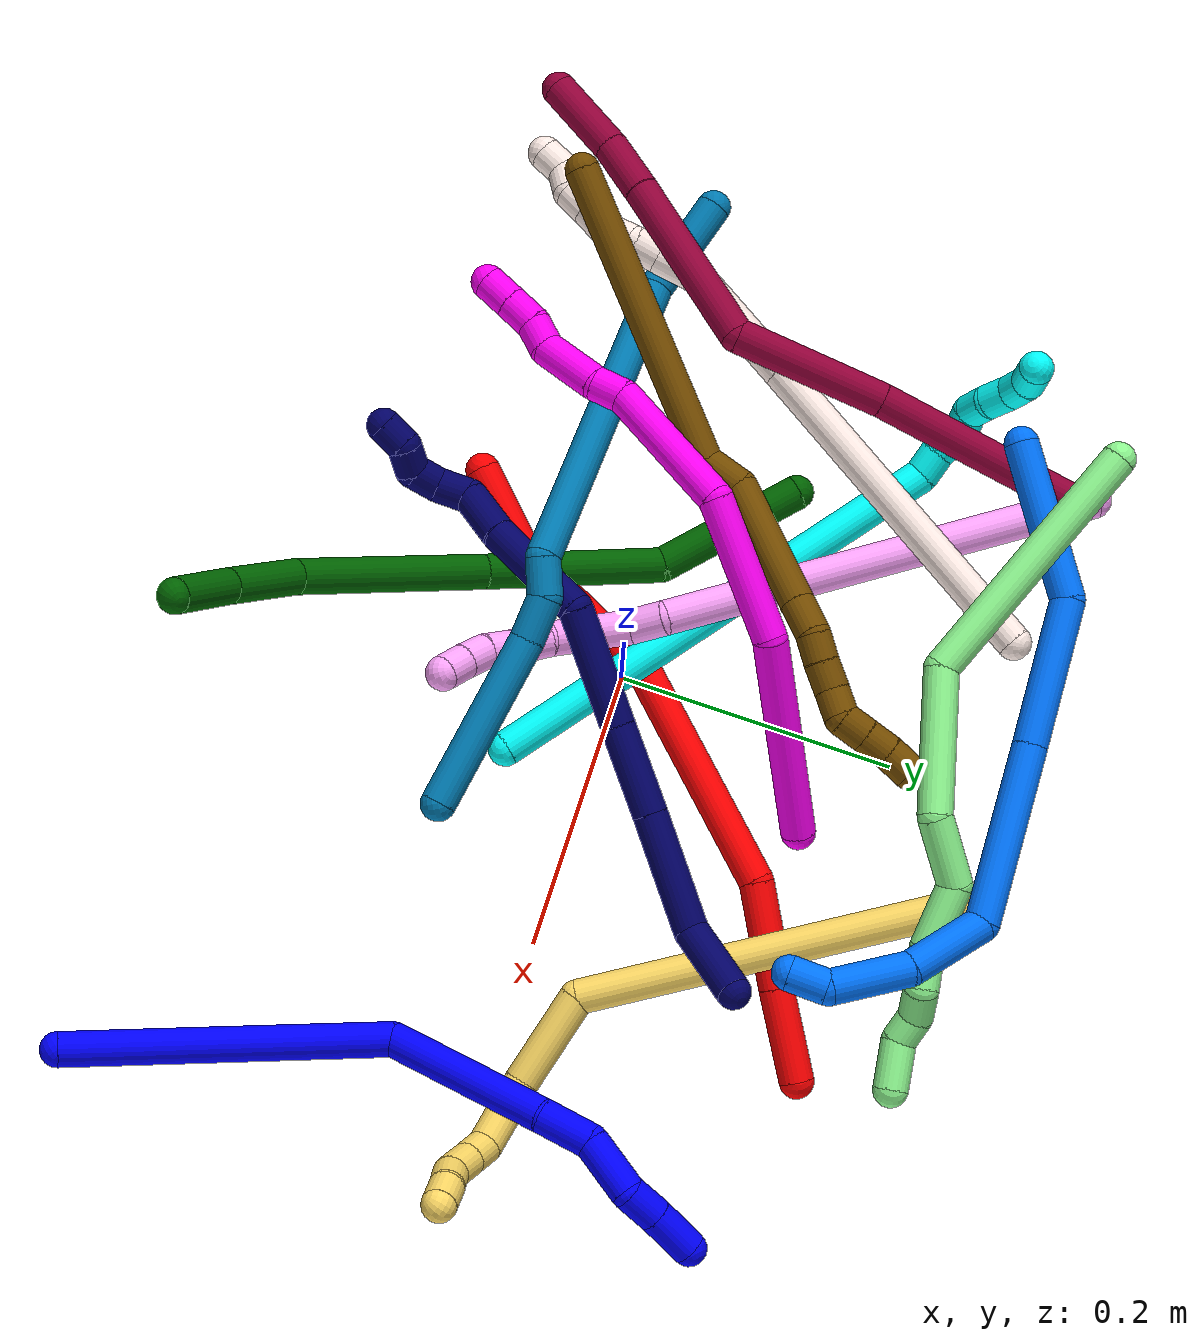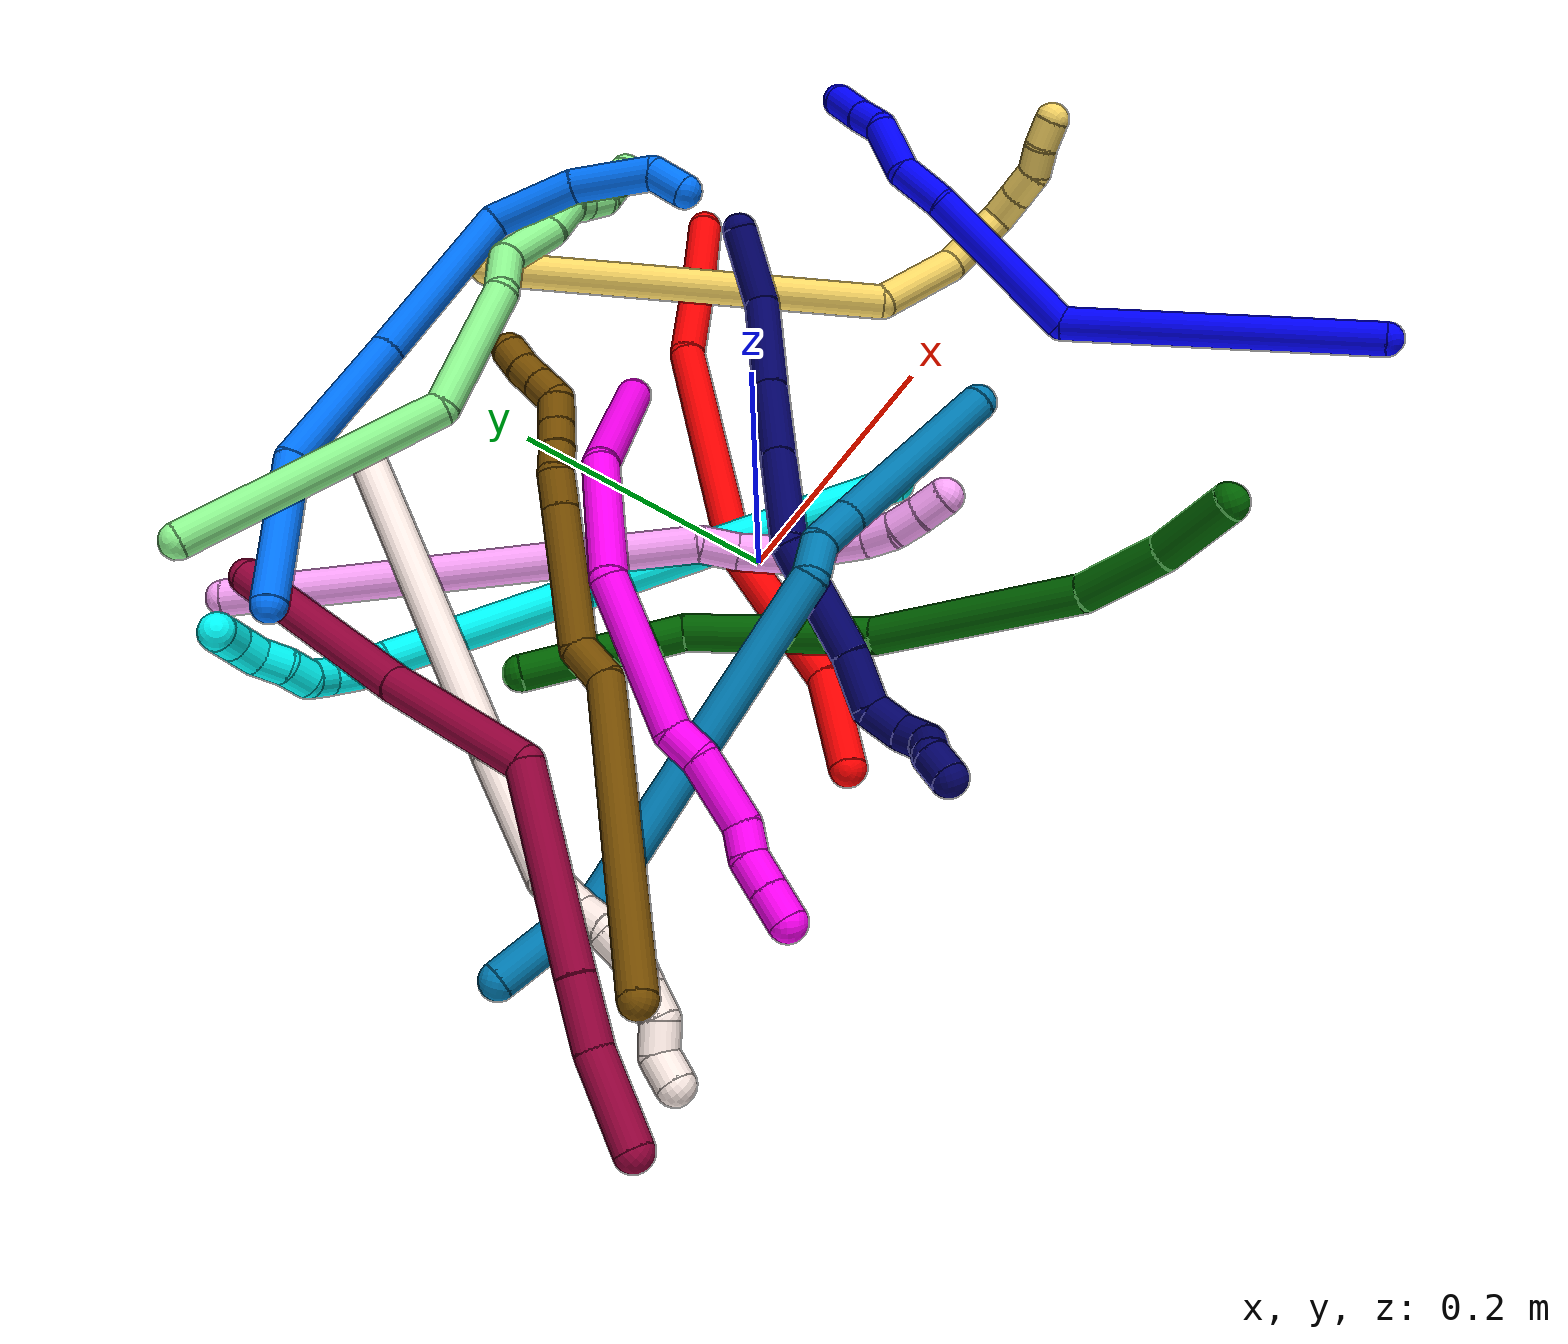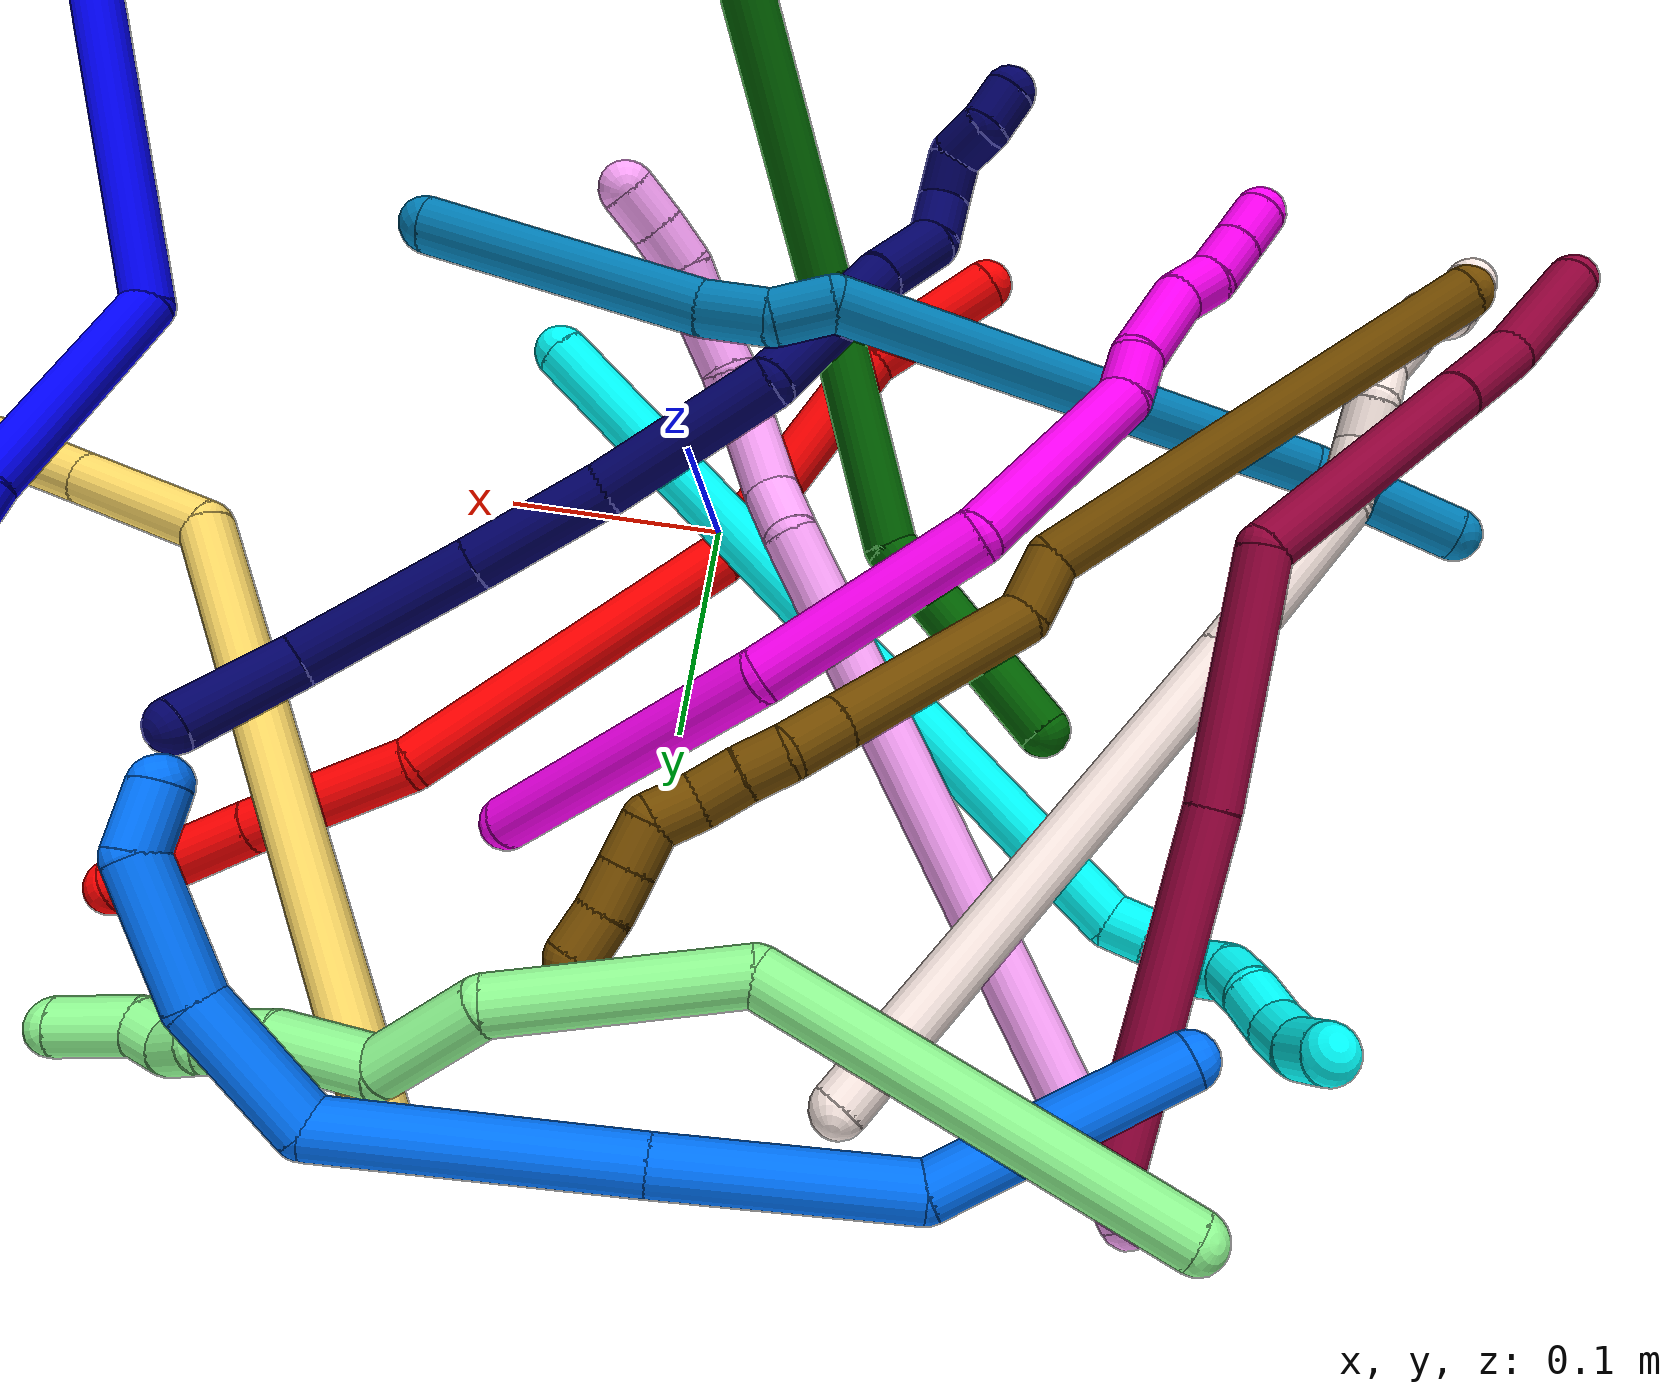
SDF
<sdf version="1.7">
 <world name="default">
  <plugin name="TubeGeneratorPlugin" filename="libtube_generator_plugin.so"/>
  <model name="photoneo_s_sensor">
   <static>1</static>
   <pose>0 0 2 1.57079 1.57079 3.14159</pose>
   <link name="link">
    <inertial><mass>0.1</mass></inertial>
    <sensor name="sensor" type="depth">
     <update_rate>30</update_rate>
     <camera>
      <horizontal_fov>1.22</horizontal_fov>
      <image><width>1920</width><height>1200</height><format>B8G8R8</format></image>
      <clip><near>0.1</near><far>4</far></clip>
      <depth_camera><output>points</output></depth_camera>
     </camera>
     <plugin name="camera_plugin" filename="libgazebo_ros_depth_camera.so">
      <baseline>0.2</baseline>
      <alwaysOn>1</alwaysOn>
      <updateRate>0.0</updateRate>
      <cameraName>camera_ir</cameraName>
      <imageTopicName>/camera/color/image_raw</imageTopicName>
      <cameraInfoTopicName>/camera/color/camera_info</cameraInfoTopicName>
      <depthImageTopicName>/camera/depth/image_raw</depthImageTopicName>
      <depthImageCameraInfoTopicName>/camera/depth/camera_info</depthImageCameraInfoTopicName>
      <pointCloudTopicName>/camera/depth/points</pointCloudTopicName>
      <frameName>fr_optical</frameName>
      <pointCloudCutoff>0.1</pointCloudCutoff>
      <pointCloudCutoffMax>2.0</pointCloudCutoffMax>
      <distortionK1>0</distortionK1>
      <distortionK2>0</distortionK2>
      <distortionK3>0</distortionK3>
      <distortionT1>0</distortionT1>
      <distortionT2>0</distortionT2>
      <CxPrime>0</CxPrime>
      <Cx>0</Cx>
      <Cy>0</Cy>
      <focalLength>0</focalLength>
      <hackBaseline>0</hackBaseline>
     </plugin>
    </sensor>
   </link>
  </model>
  <gravity>0 0 -9.8</gravity>
  <magnetic_field>6e-06 2.3e-05 -4.2e-05</magnetic_field>
  <atmosphere type="adiabatic"/>
  <physics name="default_physics" default="0" type="ode">
   <max_step_size>0.003</max_step_size>
   <real_time_factor>1</real_time_factor>
   <real_time_update_rate>1000</real_time_update_rate>
   <max_contacts>10000</max_contacts>
   <ode>
    <solver>
     <type>quick</type>
     <iters>100</iters>
     <sor>1.3</sor>
     <use_dynamic_moi_rescaling>0</use_dynamic_moi_rescaling>
    </solver>
    <constraints>
     <contact_max_correcting_vel>0</contact_max_correcting_vel>
     <contact_surface_layer>0.001</contact_surface_layer>
     <cfm>0</cfm>
     <erp>0.2</erp>
    </constraints>
   </ode>
  </physics>
  <scene><ambient>0.4 0.4 0.4 1</ambient><background>0.7 0.7 0.7 1</background><shadows>0</shadows></scene>
  <audio><device>default</device></audio>
  <spherical_coordinates>
   <surface_model>EARTH_WGS84</surface_model>
   <latitude_deg>0</latitude_deg>
   <longitude_deg>0</longitude_deg>
   <elevation>0</elevation>
   <heading_deg>0</heading_deg>
  </spherical_coordinates>
  <model name="bin">
   <static>1</static>
   <link name="bottom">
    <collision name="collision-bottom">
     <pose>0 0 -0.01 0 -0 0</pose>
     <geometry><box><size>0.8 0.6 0.02</size></box></geometry>
     <surface>
      <friction><ode><mu>100</mu><mu2>100</mu2></ode></friction>
      <contact><collide_bitmask>65535</collide_bitmask></contact>
     </surface>
    </collision>
   </link>
   <link name="west_wall">
    <collision name="collision-west_wall">
     <pose>-0.41 0 0.1 0 -0 0</pose>
     <geometry><box><size>0.02 0.6 0.2</size></box></geometry>
     <surface>
      <friction><ode><mu>100</mu><mu2>100</mu2></ode></friction>
      <contact><collide_bitmask>65535</collide_bitmask></contact>
     </surface>
    </collision>
   </link>
   <link name="east_wall">
    <collision name="collision-east_wall">
     <pose>0.41 0 0.1 0 -0 0</pose>
     <geometry><box><size>0.02 0.6 0.2</size></box></geometry>
     <surface>
      <friction><ode><mu>100</mu><mu2>100</mu2></ode></friction>
      <contact><collide_bitmask>65535</collide_bitmask></contact>
     </surface>
    </collision>
   </link>
   <link name="south_wall">
    <collision name="collision-south_wall">
     <pose>0 -0.31 0.1 0 -0 0</pose>
     <geometry><box><size>0.8 0.02 0.2</size></box></geometry>
     <surface>
      <friction><ode><mu>100</mu><mu2>100</mu2></ode></friction>
      <contact><collide_bitmask>65535</collide_bitmask></contact>
     </surface>
    </collision>
   </link>
   <link name="north_wall">
    <collision name="collision-north_wall">
     <pose>0 0.31 0.1 0 -0 0</pose>
     <geometry><box><size>0.8 0.02 0.2</size></box></geometry>
     <surface>
      <friction><ode><mu>100</mu><mu2>100</mu2></ode></friction>
      <contact><collide_bitmask>65535</collide_bitmask></contact>
     </surface>
    </collision>
   </link>
  </model>
  <model name="1">
   <static>0</static>
   <link name="1">
    <collision name="collision-cylinder-e_1_1_4">
     <pose>-0.046519 0.093395 -0.051668 -2.07611 -0.411018 0.679661</pose>
     <geometry><cylinder><radius>0.0125</radius><length>0.232863</length></cylinder></geometry>
     <surface>
      <friction><ode><mu>1.16</mu><mu2>1.16</mu2><slip1>0</slip1><slip2>0</slip2></ode></friction>
      <contact><ode><kp>1e+06</kp><kd>1</kd><max_vel>0</max_vel><min_depth>0.001</min_depth></ode></contact>
     </surface>
    </collision>
    <visual name="visual-cylinder-e_1_1_4">
     <pose>-0.046519 0.093395 -0.051668 -2.07611 -0.411018 0.679661</pose>
     <geometry><cylinder><radius>0.0125</radius><length>0.232863</length></cylinder></geometry>
     <material><ambient>0 0 1 1</ambient></material>
    </visual>
    <collision name="collision-cylinder-e_2_4_5">
     <pose>-0.084349 0.219952 -0.156638 -2.58503 0.137555 -0.4732</pose>
     <geometry><cylinder><radius>0.0125</radius><length>0.126747</length></cylinder></geometry>
     <surface>
      <friction><ode><mu>1.16</mu><mu2>1.16</mu2><slip1>0</slip1><slip2>0</slip2></ode></friction>
      <contact><ode><kp>1e+06</kp><kd>1</kd><max_vel>0</max_vel><min_depth>0.001</min_depth></ode></contact>
     </surface>
    </collision>
    <visual name="visual-cylinder-e_2_4_5">
     <pose>-0.084349 0.219952 -0.156638 -2.58503 0.137555 -0.4732</pose>
     <geometry><cylinder><radius>0.0125</radius><length>0.126747</length></cylinder></geometry>
     <material><ambient>0 0 1 1</ambient></material>
    </visual>
    <collision name="collision-cylinder-e_3_5_6">
     <pose>-0.07699 0.26283 -0.22654 -2.61209 -0.069095 0.253588</pose>
     <geometry><cylinder><radius>0.0125</radius><length>0.038564</length></cylinder></geometry>
     <surface>
      <friction><ode><mu>1.16</mu><mu2>1.16</mu2><slip1>0</slip1><slip2>0</slip2></ode></friction>
      <contact><ode><kp>1e+06</kp><kd>1</kd><max_vel>0</max_vel><min_depth>0.001</min_depth></ode></contact>
     </surface>
    </collision>
    <visual name="visual-cylinder-e_3_5_6">
     <pose>-0.07699 0.26283 -0.22654 -2.61209 -0.069095 0.253588</pose>
     <geometry><cylinder><radius>0.0125</radius><length>0.038564</length></cylinder></geometry>
     <material><ambient>0 0 1 1</ambient></material>
    </visual>
    <collision name="collision-cylinder-e_4_6_7">
     <pose>-0.079099 0.274377 -0.264432 -3.05585 -0.036382 0.80221</pose>
     <geometry><cylinder><radius>0.0125</radius><length>0.042765</length></cylinder></geometry>
     <surface>
      <friction><ode><mu>1.16</mu><mu2>1.16</mu2><slip1>0</slip1><slip2>0</slip2></ode></friction>
      <contact><ode><kp>1e+06</kp><kd>1</kd><max_vel>0</max_vel><min_depth>0.001</min_depth></ode></contact>
     </surface>
    </collision>
    <visual name="visual-cylinder-e_4_6_7">
     <pose>-0.079099 0.274377 -0.264432 -3.05585 -0.036382 0.80221</pose>
     <geometry><cylinder><radius>0.0125</radius><length>0.042765</length></cylinder></geometry>
     <material><ambient>0 0 1 1</ambient></material>
    </visual>
    <collision name="collision-cylinder-e_5_7_8">
     <pose>-0.086131 0.278978 -0.296433 -2.88842 -0.514495 2.24046</pose>
     <geometry><cylinder><radius>0.0125</radius><length>0.025418</length></cylinder></geometry>
     <surface>
      <friction><ode><mu>1.16</mu><mu2>1.16</mu2><slip1>0</slip1><slip2>0</slip2></ode></friction>
      <contact><ode><kp>1e+06</kp><kd>1</kd><max_vel>0</max_vel><min_depth>0.001</min_depth></ode></contact>
     </surface>
    </collision>
    <visual name="visual-cylinder-e_5_7_8">
     <pose>-0.086131 0.278978 -0.296433 -2.88842 -0.514495 2.24046</pose>
     <geometry><cylinder><radius>0.0125</radius><length>0.025418</length></cylinder></geometry>
     <material><ambient>0 0 1 1</ambient></material>
    </visual>
    <collision name="collision-cylinder-e_6_8_2">
     <pose>-0.100327 0.284488 -0.321717 -2.95582 -0.491687 2.43064</pose>
     <geometry><cylinder><radius>0.0125</radius><length>0.033643</length></cylinder></geometry>
     <surface>
      <friction><ode><mu>1.16</mu><mu2>1.16</mu2><slip1>0</slip1><slip2>0</slip2></ode></friction>
      <contact><ode><kp>1e+06</kp><kd>1</kd><max_vel>0</max_vel><min_depth>0.001</min_depth></ode></contact>
     </surface>
    </collision>
    <visual name="visual-cylinder-e_6_8_2">
     <pose>-0.100327 0.284488 -0.321717 -2.95582 -0.491687 2.43064</pose>
     <geometry><cylinder><radius>0.0125</radius><length>0.033643</length></cylinder></geometry>
     <material><ambient>0 0 1 1</ambient></material>
    </visual>
    <collision name="collision-sphere-2">
     <pose>-0.108268 0.287227 -0.336291 0 -0 0</pose>
     <geometry><sphere><radius>0.0125</radius></sphere></geometry>
     <surface>
      <friction><ode><mu>1.16</mu><mu2>1.16</mu2><slip1>0</slip1><slip2>0</slip2></ode></friction>
      <contact><ode><kp>1e+06</kp><kd>1</kd><max_vel>0</max_vel><min_depth>0.001</min_depth></ode></contact>
     </surface>
    </collision>
    <visual name="visual-sphere-2">
     <pose>-0.108268 0.287227 -0.336291 0 -0 0</pose>
     <geometry><sphere><radius>0.0125</radius></sphere></geometry>
     <material><ambient>0 0 1 1</ambient></material>
    </visual>
    <collision name="collision-sphere-4">
     <pose>-0.093039 0.186789 -0.103337 0 -0 0</pose>
     <geometry><sphere><radius>0.0125</radius></sphere></geometry>
     <surface>
      <friction><ode><mu>1.16</mu><mu2>1.16</mu2><slip1>0</slip1><slip2>0</slip2></ode></friction>
      <contact><ode><kp>1e+06</kp><kd>1</kd><max_vel>0</max_vel><min_depth>0.001</min_depth></ode></contact>
     </surface>
    </collision>
    <visual name="visual-sphere-4">
     <pose>-0.093039 0.186789 -0.103337 0 -0 0</pose>
     <geometry><sphere><radius>0.0125</radius></sphere></geometry>
     <material><ambient>0 0 1 1</ambient></material>
    </visual>
    <collision name="collision-sphere-1">
     <geometry><sphere><radius>0.0125</radius></sphere></geometry>
     <surface>
      <friction><ode><mu>1.16</mu><mu2>1.16</mu2><slip1>0</slip1><slip2>0</slip2></ode></friction>
      <contact><ode><kp>1e+06</kp><kd>1</kd><max_vel>0</max_vel><min_depth>0.001</min_depth></ode></contact>
     </surface>
    </collision>
    <visual name="visual-sphere-1">
     <geometry><sphere><radius>0.0125</radius></sphere></geometry>
     <material><ambient>0 0 1 1</ambient></material>
    </visual>
    <collision name="collision-sphere-8">
     <pose>-0.092385 0.281749 -0.307144 0 -0 0</pose>
     <geometry><sphere><radius>0.0125</radius></sphere></geometry>
     <surface>
      <friction><ode><mu>1.16</mu><mu2>1.16</mu2><slip1>0</slip1><slip2>0</slip2></ode></friction>
      <contact><ode><kp>1e+06</kp><kd>1</kd><max_vel>0</max_vel><min_depth>0.001</min_depth></ode></contact>
     </surface>
    </collision>
    <visual name="visual-sphere-8">
     <pose>-0.092385 0.281749 -0.307144 0 -0 0</pose>
     <geometry><sphere><radius>0.0125</radius></sphere></geometry>
     <material><ambient>0 0 1 1</ambient></material>
    </visual>
    <collision name="collision-sphere-5">
     <pose>-0.075659 0.253114 -0.209938 0 -0 0</pose>
     <geometry><sphere><radius>0.0125</radius></sphere></geometry>
     <surface>
      <friction><ode><mu>1.16</mu><mu2>1.16</mu2><slip1>0</slip1><slip2>0</slip2></ode></friction>
      <contact><ode><kp>1e+06</kp><kd>1</kd><max_vel>0</max_vel><min_depth>0.001</min_depth></ode></contact>
     </surface>
    </collision>
    <visual name="visual-sphere-5">
     <pose>-0.075659 0.253114 -0.209938 0 -0 0</pose>
     <geometry><sphere><radius>0.0125</radius></sphere></geometry>
     <material><ambient>0 0 1 1</ambient></material>
    </visual>
    <collision name="collision-sphere-6">
     <pose>-0.078321 0.272547 -0.243142 0 -0 0</pose>
     <geometry><sphere><radius>0.0125</radius></sphere></geometry>
     <surface>
      <friction><ode><mu>1.16</mu><mu2>1.16</mu2><slip1>0</slip1><slip2>0</slip2></ode></friction>
      <contact><ode><kp>1e+06</kp><kd>1</kd><max_vel>0</max_vel><min_depth>0.001</min_depth></ode></contact>
     </surface>
    </collision>
    <visual name="visual-sphere-6">
     <pose>-0.078321 0.272547 -0.243142 0 -0 0</pose>
     <geometry><sphere><radius>0.0125</radius></sphere></geometry>
     <material><ambient>0 0 1 1</ambient></material>
    </visual>
    <collision name="collision-sphere-7">
     <pose>-0.079877 0.276206 -0.285722 0 -0 0</pose>
     <geometry><sphere><radius>0.0125</radius></sphere></geometry>
     <surface>
      <friction><ode><mu>1.16</mu><mu2>1.16</mu2><slip1>0</slip1><slip2>0</slip2></ode></friction>
      <contact><ode><kp>1e+06</kp><kd>1</kd><max_vel>0</max_vel><min_depth>0.001</min_depth></ode></contact>
     </surface>
    </collision>
    <visual name="visual-sphere-7">
     <pose>-0.079877 0.276206 -0.285722 0 -0 0</pose>
     <geometry><sphere><radius>0.0125</radius></sphere></geometry>
     <material><ambient>0 0 1 1</ambient></material>
    </visual>
    <inertial>
     <pose>-0.06688 0.176316 -0.140576 0 -0 0</pose>
     <mass>0.5</mass>
     <inertia>
      <ixx>0.001454</ixx>
      <ixy>0</ixy>
      <ixz>0</ixz>
      <iyy>0.000269</iyy>
      <iyz>0</iyz>
      <izz>-0.00057</izz>
     </inertia>
    </inertial>
   </link>
   <pose>0.374116 -0.286221 0.052698 2.40657 -1.31712 -1.52179</pose>
  </model>
  <model name="2">
   <static>0</static>
   <link name="2">
    <collision name="collision-cylinder-e_1_1_4">
     <pose>0.024521 0.01348 -0.019956 -2.54749 0.794426 -1.88085</pose>
     <geometry><cylinder><radius>0.0125</radius><length>0.068738</length></cylinder></geometry>
     <surface>
      <friction><ode><mu>1.16</mu><mu2>1.16</mu2><slip1>0</slip1><slip2>0</slip2></ode></friction>
      <contact><ode><kp>1e+06</kp><kd>1</kd><max_vel>0</max_vel><min_depth>0.001</min_depth></ode></contact>
     </surface>
    </collision>
    <visual name="visual-cylinder-e_1_1_4">
     <pose>0.024521 0.01348 -0.019956 -2.54749 0.794426 -1.88085</pose>
     <geometry><cylinder><radius>0.0125</radius><length>0.068738</length></cylinder></geometry>
     <material><ambient>1 0 0 1</ambient></material>
    </visual>
    <collision name="collision-cylinder-e_2_4_5">
     <pose>0.083125 0.067867 -0.069987 -2.20478 0.5912 -1.08358</pose>
     <geometry><cylinder><radius>0.0125</radius><length>0.122305</length></cylinder></geometry>
     <surface>
      <friction><ode><mu>1.16</mu><mu2>1.16</mu2><slip1>0</slip1><slip2>0</slip2></ode></friction>
      <contact><ode><kp>1e+06</kp><kd>1</kd><max_vel>0</max_vel><min_depth>0.001</min_depth></ode></contact>
     </surface>
    </collision>
    <visual name="visual-cylinder-e_2_4_5">
     <pose>0.083125 0.067867 -0.069987 -2.20478 0.5912 -1.08358</pose>
     <geometry><cylinder><radius>0.0125</radius><length>0.122305</length></cylinder></geometry>
     <material><ambient>1 0 0 1</ambient></material>
    </visual>
    <collision name="collision-cylinder-e_3_5_6">
     <pose>0.179844 0.143005 -0.142937 -2.46782 0.851442 -1.82626</pose>
     <geometry><cylinder><radius>0.0125</radius><length>0.16653</length></cylinder></geometry>
     <surface>
      <friction><ode><mu>1.16</mu><mu2>1.16</mu2><slip1>0</slip1><slip2>0</slip2></ode></friction>
      <contact><ode><kp>1e+06</kp><kd>1</kd><max_vel>0</max_vel><min_depth>0.001</min_depth></ode></contact>
     </surface>
    </collision>
    <visual name="visual-cylinder-e_3_5_6">
     <pose>0.179844 0.143005 -0.142937 -2.46782 0.851442 -1.82626</pose>
     <geometry><cylinder><radius>0.0125</radius><length>0.16653</length></cylinder></geometry>
     <material><ambient>1 0 0 1</ambient></material>
    </visual>
    <collision name="collision-cylinder-e_4_6_7">
     <pose>0.26852 0.18204 -0.212784 -2.96537 0.760025 -2.70627</pose>
     <geometry><cylinder><radius>0.0125</radius><length>0.075598</length></cylinder></geometry>
     <surface>
      <friction><ode><mu>1.16</mu><mu2>1.16</mu2><slip1>0</slip1><slip2>0</slip2></ode></friction>
      <contact><ode><kp>1e+06</kp><kd>1</kd><max_vel>0</max_vel><min_depth>0.001</min_depth></ode></contact>
     </surface>
    </collision>
    <visual name="visual-cylinder-e_4_6_7">
     <pose>0.26852 0.18204 -0.212784 -2.96537 0.760025 -2.70627</pose>
     <geometry><cylinder><radius>0.0125</radius><length>0.075598</length></cylinder></geometry>
     <material><ambient>1 0 0 1</ambient></material>
    </visual>
    <collision name="collision-cylinder-e_5_7_2">
     <pose>0.317297 0.192165 -0.263659 -2.92248 0.748345 -2.59535</pose>
     <geometry><cylinder><radius>0.0125</radius><length>0.066829</length></cylinder></geometry>
     <surface>
      <friction><ode><mu>1.16</mu><mu2>1.16</mu2><slip1>0</slip1><slip2>0</slip2></ode></friction>
      <contact><ode><kp>1e+06</kp><kd>1</kd><max_vel>0</max_vel><min_depth>0.001</min_depth></ode></contact>
     </surface>
    </collision>
    <visual name="visual-cylinder-e_5_7_2">
     <pose>0.317297 0.192165 -0.263659 -2.92248 0.748345 -2.59535</pose>
     <geometry><cylinder><radius>0.0125</radius><length>0.066829</length></cylinder></geometry>
     <material><ambient>1 0 0 1</ambient></material>
    </visual>
    <collision name="collision-sphere-2">
     <pose>0.340034 0.197488 -0.28756 0 -0 0</pose>
     <geometry><sphere><radius>0.0125</radius></sphere></geometry>
     <surface>
      <friction><ode><mu>1.16</mu><mu2>1.16</mu2><slip1>0</slip1><slip2>0</slip2></ode></friction>
      <contact><ode><kp>1e+06</kp><kd>1</kd><max_vel>0</max_vel><min_depth>0.001</min_depth></ode></contact>
     </surface>
    </collision>
    <visual name="visual-sphere-2">
     <pose>0.340034 0.197488 -0.28756 0 -0 0</pose>
     <geometry><sphere><radius>0.0125</radius></sphere></geometry>
     <material><ambient>1 0 0 1</ambient></material>
    </visual>
    <collision name="collision-sphere-7">
     <pose>0.294561 0.186843 -0.239758 0 -0 0</pose>
     <geometry><sphere><radius>0.0125</radius></sphere></geometry>
     <surface>
      <friction><ode><mu>1.16</mu><mu2>1.16</mu2><slip1>0</slip1><slip2>0</slip2></ode></friction>
      <contact><ode><kp>1e+06</kp><kd>1</kd><max_vel>0</max_vel><min_depth>0.001</min_depth></ode></contact>
     </surface>
    </collision>
    <visual name="visual-sphere-7">
     <pose>0.294561 0.186843 -0.239758 0 -0 0</pose>
     <geometry><sphere><radius>0.0125</radius></sphere></geometry>
     <material><ambient>1 0 0 1</ambient></material>
    </visual>
    <collision name="collision-sphere-6">
     <pose>0.242479 0.177237 -0.185811 0 -0 0</pose>
     <geometry><sphere><radius>0.0125</radius></sphere></geometry>
     <surface>
      <friction><ode><mu>1.16</mu><mu2>1.16</mu2><slip1>0</slip1><slip2>0</slip2></ode></friction>
      <contact><ode><kp>1e+06</kp><kd>1</kd><max_vel>0</max_vel><min_depth>0.001</min_depth></ode></contact>
     </surface>
    </collision>
    <visual name="visual-sphere-6">
     <pose>0.242479 0.177237 -0.185811 0 -0 0</pose>
     <geometry><sphere><radius>0.0125</radius></sphere></geometry>
     <material><ambient>1 0 0 1</ambient></material>
    </visual>
    <collision name="collision-sphere-5">
     <pose>0.117209 0.108774 -0.100062 0 -0 0</pose>
     <geometry><sphere><radius>0.0125</radius></sphere></geometry>
     <surface>
      <friction><ode><mu>1.16</mu><mu2>1.16</mu2><slip1>0</slip1><slip2>0</slip2></ode></friction>
      <contact><ode><kp>1e+06</kp><kd>1</kd><max_vel>0</max_vel><min_depth>0.001</min_depth></ode></contact>
     </surface>
    </collision>
    <visual name="visual-sphere-5">
     <pose>0.117209 0.108774 -0.100062 0 -0 0</pose>
     <geometry><sphere><radius>0.0125</radius></sphere></geometry>
     <material><ambient>1 0 0 1</ambient></material>
    </visual>
    <collision name="collision-sphere-1">
     <geometry><sphere><radius>0.0125</radius></sphere></geometry>
     <surface>
      <friction><ode><mu>1.16</mu><mu2>1.16</mu2><slip1>0</slip1><slip2>0</slip2></ode></friction>
      <contact><ode><kp>1e+06</kp><kd>1</kd><max_vel>0</max_vel><min_depth>0.001</min_depth></ode></contact>
     </surface>
    </collision>
    <visual name="visual-sphere-1">
     <geometry><sphere><radius>0.0125</radius></sphere></geometry>
     <material><ambient>1 0 0 1</ambient></material>
    </visual>
    <collision name="collision-sphere-4">
     <pose>0.049042 0.026961 -0.039911 0 -0 0</pose>
     <geometry><sphere><radius>0.0125</radius></sphere></geometry>
     <surface>
      <friction><ode><mu>1.16</mu><mu2>1.16</mu2><slip1>0</slip1><slip2>0</slip2></ode></friction>
      <contact><ode><kp>1e+06</kp><kd>1</kd><max_vel>0</max_vel><min_depth>0.001</min_depth></ode></contact>
     </surface>
    </collision>
    <visual name="visual-sphere-4">
     <pose>0.049042 0.026961 -0.039911 0 -0 0</pose>
     <geometry><sphere><radius>0.0125</radius></sphere></geometry>
     <material><ambient>1 0 0 1</ambient></material>
    </visual>
    <inertial>
     <pose>0.166612 0.119292 -0.134882 0 -0 0</pose>
     <mass>0.5</mass>
     <inertia>
      <ixx>-0.000434</ixx>
      <ixy>0</ixy>
      <ixz>0</ixz>
      <iyy>-3.7e-05</iyy>
      <iyz>0</iyz>
      <izz>-0.000758</izz>
     </inertia>
    </inertial>
   </link>
   <pose>-0.109023 -0.141371 0.012119 0.009749 -0.697214 0.370482</pose>
  </model>
  <model name="3">
   <static>0</static>
   <link name="3">
    <collision name="collision-cylinder-e_1_1_4">
     <pose>-0.079106 0.15634 -0.037982 -1.80913 -0.456973 0.575214</pose>
     <geometry><cylinder><radius>0.0125</radius><length>0.358568</length></cylinder></geometry>
     <surface>
      <friction><ode><mu>1.16</mu><mu2>1.16</mu2><slip1>0</slip1><slip2>0</slip2></ode></friction>
      <contact><ode><kp>1e+06</kp><kd>1</kd><max_vel>0</max_vel><min_depth>0.001</min_depth></ode></contact>
     </surface>
    </collision>
    <visual name="visual-cylinder-e_1_1_4">
     <pose>-0.079106 0.15634 -0.037982 -1.80913 -0.456973 0.575214</pose>
     <geometry><cylinder><radius>0.0125</radius><length>0.358568</length></cylinder></geometry>
     <material><ambient>0.003922 1 0.996078 1</ambient></material>
    </visual>
    <collision name="collision-cylinder-e_2_4_5">
     <pose>-0.164498 0.320531 -0.073386 -1.25349 -0.650317 0.478883</pose>
     <geometry><cylinder><radius>0.0125</radius><length>0.020764</length></cylinder></geometry>
     <surface>
      <friction><ode><mu>1.16</mu><mu2>1.16</mu2><slip1>0</slip1><slip2>0</slip2></ode></friction>
      <contact><ode><kp>1e+06</kp><kd>1</kd><max_vel>0</max_vel><min_depth>0.001</min_depth></ode></contact>
     </surface>
    </collision>
    <visual name="visual-cylinder-e_2_4_5">
     <pose>-0.164498 0.320531 -0.073386 -1.25349 -0.650317 0.478883</pose>
     <geometry><cylinder><radius>0.0125</radius><length>0.020764</length></cylinder></geometry>
     <material><ambient>0.003922 1 0.996078 1</ambient></material>
    </visual>
    <collision name="collision-cylinder-e_3_5_6">
     <pose>-0.175026 0.337532 -0.068822 -1.35708 -0.425392 0.344783</pose>
     <geometry><cylinder><radius>0.0125</radius><length>0.020558</length></cylinder></geometry>
     <surface>
      <friction><ode><mu>1.16</mu><mu2>1.16</mu2><slip1>0</slip1><slip2>0</slip2></ode></friction>
      <contact><ode><kp>1e+06</kp><kd>1</kd><max_vel>0</max_vel><min_depth>0.001</min_depth></ode></contact>
     </surface>
    </collision>
    <visual name="visual-cylinder-e_3_5_6">
     <pose>-0.175026 0.337532 -0.068822 -1.35708 -0.425392 0.344783</pose>
     <geometry><cylinder><radius>0.0125</radius><length>0.020558</length></cylinder></geometry>
     <material><ambient>0.003922 1 0.996078 1</ambient></material>
    </visual>
    <collision name="collision-cylinder-e_4_6_7">
     <pose>-0.183411 0.352341 -0.059699 -0.670367 -0.426886 0.15071</pose>
     <geometry><cylinder><radius>0.0125</radius><length>0.020012</length></cylinder></geometry>
     <surface>
      <friction><ode><mu>1.16</mu><mu2>1.16</mu2><slip1>0</slip1><slip2>0</slip2></ode></friction>
      <contact><ode><kp>1e+06</kp><kd>1</kd><max_vel>0</max_vel><min_depth>0.001</min_depth></ode></contact>
     </surface>
    </collision>
    <visual name="visual-cylinder-e_4_6_7">
     <pose>-0.183411 0.352341 -0.059699 -0.670367 -0.426886 0.15071</pose>
     <geometry><cylinder><radius>0.0125</radius><length>0.020012</length></cylinder></geometry>
     <material><ambient>0.003922 1 0.996078 1</ambient></material>
    </visual>
    <collision name="collision-cylinder-e_5_7_8">
     <pose>-0.186577 0.365363 -0.045845 -0.831319 0.097689 -0.043145</pose>
     <geometry><cylinder><radius>0.0125</radius><length>0.02003</length></cylinder></geometry>
     <surface>
      <friction><ode><mu>1.16</mu><mu2>1.16</mu2><slip1>0</slip1><slip2>0</slip2></ode></friction>
      <contact><ode><kp>1e+06</kp><kd>1</kd><max_vel>0</max_vel><min_depth>0.001</min_depth></ode></contact>
     </surface>
    </collision>
    <visual name="visual-cylinder-e_5_7_8">
     <pose>-0.186577 0.365363 -0.045845 -0.831319 0.097689 -0.043145</pose>
     <geometry><cylinder><radius>0.0125</radius><length>0.02003</length></cylinder></geometry>
     <material><ambient>0.003922 1 0.996078 1</ambient></material>
    </visual>
    <collision name="collision-cylinder-e_6_8_9">
     <pose>-0.185252 0.381723 -0.034734 -1.11641 0.03476 -0.021707</pose>
     <geometry><cylinder><radius>0.0125</radius><length>0.020034</length></cylinder></geometry>
     <surface>
      <friction><ode><mu>1.16</mu><mu2>1.16</mu2><slip1>0</slip1><slip2>0</slip2></ode></friction>
      <contact><ode><kp>1e+06</kp><kd>1</kd><max_vel>0</max_vel><min_depth>0.001</min_depth></ode></contact>
     </surface>
    </collision>
    <visual name="visual-cylinder-e_6_8_9">
     <pose>-0.185252 0.381723 -0.034734 -1.11641 0.03476 -0.021707</pose>
     <geometry><cylinder><radius>0.0125</radius><length>0.020034</length></cylinder></geometry>
     <material><ambient>0.003922 1 0.996078 1</ambient></material>
    </visual>
    <collision name="collision-cylinder-e_7_9_10">
     <pose>-0.183794 0.397724 -0.023273 -0.781026 0.111023 -0.045742</pose>
     <geometry><cylinder><radius>0.0125</radius><length>0.020027</length></cylinder></geometry>
     <surface>
      <friction><ode><mu>1.16</mu><mu2>1.16</mu2><slip1>0</slip1><slip2>0</slip2></ode></friction>
      <contact><ode><kp>1e+06</kp><kd>1</kd><max_vel>0</max_vel><min_depth>0.001</min_depth></ode></contact>
     </surface>
    </collision>
    <visual name="visual-cylinder-e_7_9_10">
     <pose>-0.183794 0.397724 -0.023273 -0.781026 0.111023 -0.045742</pose>
     <geometry><cylinder><radius>0.0125</radius><length>0.020027</length></cylinder></geometry>
     <material><ambient>0.003922 1 0.996078 1</ambient></material>
    </visual>
    <collision name="collision-cylinder-e_8_10_2">
     <pose>-0.183213 0.409238 -0.007291 -0.468187 -0.052822 0.012599</pose>
     <geometry><cylinder><radius>0.0125</radius><length>0.020006</length></cylinder></geometry>
     <surface>
      <friction><ode><mu>1.16</mu><mu2>1.16</mu2><slip1>0</slip1><slip2>0</slip2></ode></friction>
      <contact><ode><kp>1e+06</kp><kd>1</kd><max_vel>0</max_vel><min_depth>0.001</min_depth></ode></contact>
     </surface>
    </collision>
    <visual name="visual-cylinder-e_8_10_2">
     <pose>-0.183213 0.409238 -0.007291 -0.468187 -0.052822 0.012599</pose>
     <geometry><cylinder><radius>0.0125</radius><length>0.020006</length></cylinder></geometry>
     <material><ambient>0.003922 1 0.996078 1</ambient></material>
    </visual>
    <collision name="collision-sphere-2">
     <pose>-0.183741 0.413746 0.001623 0 -0 0</pose>
     <geometry><sphere><radius>0.0125</radius></sphere></geometry>
     <surface>
      <friction><ode><mu>1.16</mu><mu2>1.16</mu2><slip1>0</slip1><slip2>0</slip2></ode></friction>
      <contact><ode><kp>1e+06</kp><kd>1</kd><max_vel>0</max_vel><min_depth>0.001</min_depth></ode></contact>
     </surface>
    </collision>
    <visual name="visual-sphere-2">
     <pose>-0.183741 0.413746 0.001623 0 -0 0</pose>
     <geometry><sphere><radius>0.0125</radius></sphere></geometry>
     <material><ambient>0.003922 1 0.996078 1</ambient></material>
    </visual>
    <collision name="collision-sphere-10">
     <pose>-0.182685 0.40473 -0.016205 0 -0 0</pose>
     <geometry><sphere><radius>0.0125</radius></sphere></geometry>
     <surface>
      <friction><ode><mu>1.16</mu><mu2>1.16</mu2><slip1>0</slip1><slip2>0</slip2></ode></friction>
      <contact><ode><kp>1e+06</kp><kd>1</kd><max_vel>0</max_vel><min_depth>0.001</min_depth></ode></contact>
     </surface>
    </collision>
    <visual name="visual-sphere-10">
     <pose>-0.182685 0.40473 -0.016205 0 -0 0</pose>
     <geometry><sphere><radius>0.0125</radius></sphere></geometry>
     <material><ambient>0.003922 1 0.996078 1</ambient></material>
    </visual>
    <collision name="collision-sphere-9">
     <pose>-0.184904 0.390718 -0.03034 0 -0 0</pose>
     <geometry><sphere><radius>0.0125</radius></sphere></geometry>
     <surface>
      <friction><ode><mu>1.16</mu><mu2>1.16</mu2><slip1>0</slip1><slip2>0</slip2></ode></friction>
      <contact><ode><kp>1e+06</kp><kd>1</kd><max_vel>0</max_vel><min_depth>0.001</min_depth></ode></contact>
     </surface>
    </collision>
    <visual name="visual-sphere-9">
     <pose>-0.184904 0.390718 -0.03034 0 -0 0</pose>
     <geometry><sphere><radius>0.0125</radius></sphere></geometry>
     <material><ambient>0.003922 1 0.996078 1</ambient></material>
    </visual>
    <collision name="collision-sphere-4">
     <pose>-0.158212 0.312681 -0.075964 0 -0 0</pose>
     <geometry><sphere><radius>0.0125</radius></sphere></geometry>
     <surface>
      <friction><ode><mu>1.16</mu><mu2>1.16</mu2><slip1>0</slip1><slip2>0</slip2></ode></friction>
      <contact><ode><kp>1e+06</kp><kd>1</kd><max_vel>0</max_vel><min_depth>0.001</min_depth></ode></contact>
     </surface>
    </collision>
    <visual name="visual-sphere-4">
     <pose>-0.158212 0.312681 -0.075964 0 -0 0</pose>
     <geometry><sphere><radius>0.0125</radius></sphere></geometry>
     <material><ambient>0.003922 1 0.996078 1</ambient></material>
    </visual>
    <collision name="collision-sphere-1">
     <geometry><sphere><radius>0.0125</radius></sphere></geometry>
     <surface>
      <friction><ode><mu>1.16</mu><mu2>1.16</mu2><slip1>0</slip1><slip2>0</slip2></ode></friction>
      <contact><ode><kp>1e+06</kp><kd>1</kd><max_vel>0</max_vel><min_depth>0.001</min_depth></ode></contact>
     </surface>
    </collision>
    <visual name="visual-sphere-1">
     <geometry><sphere><radius>0.0125</radius></sphere></geometry>
     <material><ambient>0.003922 1 0.996078 1</ambient></material>
    </visual>
    <collision name="collision-sphere-8">
     <pose>-0.1856 0.372727 -0.039128 0 -0 0</pose>
     <geometry><sphere><radius>0.0125</radius></sphere></geometry>
     <surface>
      <friction><ode><mu>1.16</mu><mu2>1.16</mu2><slip1>0</slip1><slip2>0</slip2></ode></friction>
      <contact><ode><kp>1e+06</kp><kd>1</kd><max_vel>0</max_vel><min_depth>0.001</min_depth></ode></contact>
     </surface>
    </collision>
    <visual name="visual-sphere-8">
     <pose>-0.1856 0.372727 -0.039128 0 -0 0</pose>
     <geometry><sphere><radius>0.0125</radius></sphere></geometry>
     <material><ambient>0.003922 1 0.996078 1</ambient></material>
    </visual>
    <collision name="collision-sphere-5">
     <pose>-0.170784 0.328382 -0.070808 0 -0 0</pose>
     <geometry><sphere><radius>0.0125</radius></sphere></geometry>
     <surface>
      <friction><ode><mu>1.16</mu><mu2>1.16</mu2><slip1>0</slip1><slip2>0</slip2></ode></friction>
      <contact><ode><kp>1e+06</kp><kd>1</kd><max_vel>0</max_vel><min_depth>0.001</min_depth></ode></contact>
     </surface>
    </collision>
    <visual name="visual-sphere-5">
     <pose>-0.170784 0.328382 -0.070808 0 -0 0</pose>
     <geometry><sphere><radius>0.0125</radius></sphere></geometry>
     <material><ambient>0.003922 1 0.996078 1</ambient></material>
    </visual>
    <collision name="collision-sphere-6">
     <pose>-0.179268 0.346682 -0.066836 0 -0 0</pose>
     <geometry><sphere><radius>0.0125</radius></sphere></geometry>
     <surface>
      <friction><ode><mu>1.16</mu><mu2>1.16</mu2><slip1>0</slip1><slip2>0</slip2></ode></friction>
      <contact><ode><kp>1e+06</kp><kd>1</kd><max_vel>0</max_vel><min_depth>0.001</min_depth></ode></contact>
     </surface>
    </collision>
    <visual name="visual-sphere-6">
     <pose>-0.179268 0.346682 -0.066836 0 -0 0</pose>
     <geometry><sphere><radius>0.0125</radius></sphere></geometry>
     <material><ambient>0.003922 1 0.996078 1</ambient></material>
    </visual>
    <collision name="collision-sphere-7">
     <pose>-0.187554 0.357999 -0.052562 0 -0 0</pose>
     <geometry><sphere><radius>0.0125</radius></sphere></geometry>
     <surface>
      <friction><ode><mu>1.16</mu><mu2>1.16</mu2><slip1>0</slip1><slip2>0</slip2></ode></friction>
      <contact><ode><kp>1e+06</kp><kd>1</kd><max_vel>0</max_vel><min_depth>0.001</min_depth></ode></contact>
     </surface>
    </collision>
    <visual name="visual-sphere-7">
     <pose>-0.187554 0.357999 -0.052562 0 -0 0</pose>
     <geometry><sphere><radius>0.0125</radius></sphere></geometry>
     <material><ambient>0.003922 1 0.996078 1</ambient></material>
    </visual>
    <inertial>
     <pose>-0.107688 0.215645 -0.039957 0 -0 0</pose>
     <mass>0.5</mass>
     <inertia>
      <ixx>0.004782</ixx>
      <ixy>0</ixy>
      <ixz>0</ixz>
      <iyy>0.002058</iyy>
      <iyz>0</iyz>
      <izz>-0.001666</izz>
     </inertia>
    </inertial>
   </link>
   <pose>0.078177 -0.060158 0.046689 0.242723 -0.233283 0.468543</pose>
  </model>
  <model name="4">
   <static>0</static>
   <link name="4">
    <collision name="collision-cylinder-e_1_1_4">
     <pose>0.01134 -0.136554 -0.086725 2.13662 0.069984 0.127232</pose>
     <geometry><cylinder><radius>0.0125</radius><length>0.324325</length></cylinder></geometry>
     <surface>
      <friction><ode><mu>1.16</mu><mu2>1.16</mu2><slip1>0</slip1><slip2>0</slip2></ode></friction>
      <contact><ode><kp>1e+06</kp><kd>1</kd><max_vel>0</max_vel><min_depth>0.001</min_depth></ode></contact>
     </surface>
    </collision>
    <visual name="visual-cylinder-e_1_1_4">
     <pose>0.01134 -0.136554 -0.086725 2.13662 0.069984 0.127232</pose>
     <geometry><cylinder><radius>0.0125</radius><length>0.324325</length></cylinder></geometry>
     <material><ambient>1 0.65098 0.996078 1</ambient></material>
    </visual>
    <collision name="collision-cylinder-e_2_4_5">
     <pose>0.023036 -0.279843 -0.184402 2.59026 0.027775 0.09812</pose>
     <geometry><cylinder><radius>0.0125</radius><length>0.025726</length></cylinder></geometry>
     <surface>
      <friction><ode><mu>1.16</mu><mu2>1.16</mu2><slip1>0</slip1><slip2>0</slip2></ode></friction>
      <contact><ode><kp>1e+06</kp><kd>1</kd><max_vel>0</max_vel><min_depth>0.001</min_depth></ode></contact>
     </surface>
    </collision>
    <visual name="visual-cylinder-e_2_4_5">
     <pose>0.023036 -0.279843 -0.184402 2.59026 0.027775 0.09812</pose>
     <geometry><cylinder><radius>0.0125</radius><length>0.025726</length></cylinder></geometry>
     <material><ambient>1 0.65098 0.996078 1</ambient></material>
    </visual>
    <collision name="collision-cylinder-e_3_5_6">
     <pose>0.022459 -0.299547 -0.206385 2.27557 -0.054845 -0.118535</pose>
     <geometry><cylinder><radius>0.0125</radius><length>0.034101</length></cylinder></geometry>
     <surface>
      <friction><ode><mu>1.16</mu><mu2>1.16</mu2><slip1>0</slip1><slip2>0</slip2></ode></friction>
      <contact><ode><kp>1e+06</kp><kd>1</kd><max_vel>0</max_vel><min_depth>0.001</min_depth></ode></contact>
     </surface>
    </collision>
    <visual name="visual-cylinder-e_3_5_6">
     <pose>0.022459 -0.299547 -0.206385 2.27557 -0.054845 -0.118535</pose>
     <geometry><cylinder><radius>0.0125</radius><length>0.034101</length></cylinder></geometry>
     <material><ambient>1 0.65098 0.996078 1</ambient></material>
    </visual>
    <collision name="collision-cylinder-e_4_6_7">
     <pose>0.021216 -0.325307 -0.220492 1.80688 -0.023432 -0.029736</pose>
     <geometry><cylinder><radius>0.0125</radius><length>0.026319</length></cylinder></geometry>
     <surface>
      <friction><ode><mu>1.16</mu><mu2>1.16</mu2><slip1>0</slip1><slip2>0</slip2></ode></friction>
      <contact><ode><kp>1e+06</kp><kd>1</kd><max_vel>0</max_vel><min_depth>0.001</min_depth></ode></contact>
     </surface>
    </collision>
    <visual name="visual-cylinder-e_4_6_7">
     <pose>0.021216 -0.325307 -0.220492 1.80688 -0.023432 -0.029736</pose>
     <geometry><cylinder><radius>0.0125</radius><length>0.026319</length></cylinder></geometry>
     <material><ambient>1 0.65098 0.996078 1</ambient></material>
    </visual>
    <collision name="collision-cylinder-e_5_7_8">
     <pose>0.021452 -0.350644 -0.229722 2.0267 0.038964 0.06249</pose>
     <geometry><cylinder><radius>0.0125</radius><length>0.027969</length></cylinder></geometry>
     <surface>
      <friction><ode><mu>1.16</mu><mu2>1.16</mu2><slip1>0</slip1><slip2>0</slip2></ode></friction>
      <contact><ode><kp>1e+06</kp><kd>1</kd><max_vel>0</max_vel><min_depth>0.001</min_depth></ode></contact>
     </surface>
    </collision>
    <visual name="visual-cylinder-e_5_7_8">
     <pose>0.021452 -0.350644 -0.229722 2.0267 0.038964 0.06249</pose>
     <geometry><cylinder><radius>0.0125</radius><length>0.027969</length></cylinder></geometry>
     <material><ambient>1 0.65098 0.996078 1</ambient></material>
    </visual>
    <collision name="collision-cylinder-e_6_8_9">
     <pose>0.021801 -0.373794 -0.237757 1.74653 -0.018174 -0.021685</pose>
     <geometry><cylinder><radius>0.0125</radius><length>0.021542</length></cylinder></geometry>
     <surface>
      <friction><ode><mu>1.16</mu><mu2>1.16</mu2><slip1>0</slip1><slip2>0</slip2></ode></friction>
      <contact><ode><kp>1e+06</kp><kd>1</kd><max_vel>0</max_vel><min_depth>0.001</min_depth></ode></contact>
     </surface>
    </collision>
    <visual name="visual-cylinder-e_6_8_9">
     <pose>0.021801 -0.373794 -0.237757 1.74653 -0.018174 -0.021685</pose>
     <geometry><cylinder><radius>0.0125</radius><length>0.021542</length></cylinder></geometry>
     <material><ambient>1 0.65098 0.996078 1</ambient></material>
    </visual>
    <collision name="collision-cylinder-e_7_9_10">
     <pose>0.023972 -0.394071 -0.240582 1.66793 0.238844 0.262979</pose>
     <geometry><cylinder><radius>0.0125</radius><length>0.020006</length></cylinder></geometry>
     <surface>
      <friction><ode><mu>1.16</mu><mu2>1.16</mu2><slip1>0</slip1><slip2>0</slip2></ode></friction>
      <contact><ode><kp>1e+06</kp><kd>1</kd><max_vel>0</max_vel><min_depth>0.001</min_depth></ode></contact>
     </surface>
    </collision>
    <visual name="visual-cylinder-e_7_9_10">
     <pose>0.023972 -0.394071 -0.240582 1.66793 0.238844 0.262979</pose>
     <geometry><cylinder><radius>0.0125</radius><length>0.020006</length></cylinder></geometry>
     <material><ambient>1 0.65098 0.996078 1</ambient></material>
    </visual>
    <collision name="collision-cylinder-e_8_10_2">
     <pose>0.029234 -0.413304 -0.24211 1.63195 0.293528 0.311761</pose>
     <geometry><cylinder><radius>0.0125</radius><length>0.020012</length></cylinder></geometry>
     <surface>
      <friction><ode><mu>1.16</mu><mu2>1.16</mu2><slip1>0</slip1><slip2>0</slip2></ode></friction>
      <contact><ode><kp>1e+06</kp><kd>1</kd><max_vel>0</max_vel><min_depth>0.001</min_depth></ode></contact>
     </surface>
    </collision>
    <visual name="visual-cylinder-e_8_10_2">
     <pose>0.029234 -0.413304 -0.24211 1.63195 0.293528 0.311761</pose>
     <geometry><cylinder><radius>0.0125</radius><length>0.020012</length></cylinder></geometry>
     <material><ambient>1 0.65098 0.996078 1</ambient></material>
    </visual>
    <collision name="collision-sphere-2">
     <pose>0.032129 -0.422864 -0.242695 0 -0 0</pose>
     <geometry><sphere><radius>0.0125</radius></sphere></geometry>
     <surface>
      <friction><ode><mu>1.16</mu><mu2>1.16</mu2><slip1>0</slip1><slip2>0</slip2></ode></friction>
      <contact><ode><kp>1e+06</kp><kd>1</kd><max_vel>0</max_vel><min_depth>0.001</min_depth></ode></contact>
     </surface>
    </collision>
    <visual name="visual-sphere-2">
     <pose>0.032129 -0.422864 -0.242695 0 -0 0</pose>
     <geometry><sphere><radius>0.0125</radius></sphere></geometry>
     <material><ambient>1 0.65098 0.996078 1</ambient></material>
    </visual>
    <collision name="collision-sphere-10">
     <pose>0.026339 -0.403744 -0.241524 0 -0 0</pose>
     <geometry><sphere><radius>0.0125</radius></sphere></geometry>
     <surface>
      <friction><ode><mu>1.16</mu><mu2>1.16</mu2><slip1>0</slip1><slip2>0</slip2></ode></friction>
      <contact><ode><kp>1e+06</kp><kd>1</kd><max_vel>0</max_vel><min_depth>0.001</min_depth></ode></contact>
     </surface>
    </collision>
    <visual name="visual-sphere-10">
     <pose>0.026339 -0.403744 -0.241524 0 -0 0</pose>
     <geometry><sphere><radius>0.0125</radius></sphere></geometry>
     <material><ambient>1 0.65098 0.996078 1</ambient></material>
    </visual>
    <collision name="collision-sphere-9">
     <pose>0.021606 -0.384398 -0.239639 0 -0 0</pose>
     <geometry><sphere><radius>0.0125</radius></sphere></geometry>
     <surface>
      <friction><ode><mu>1.16</mu><mu2>1.16</mu2><slip1>0</slip1><slip2>0</slip2></ode></friction>
      <contact><ode><kp>1e+06</kp><kd>1</kd><max_vel>0</max_vel><min_depth>0.001</min_depth></ode></contact>
     </surface>
    </collision>
    <visual name="visual-sphere-9">
     <pose>0.021606 -0.384398 -0.239639 0 -0 0</pose>
     <geometry><sphere><radius>0.0125</radius></sphere></geometry>
     <material><ambient>1 0.65098 0.996078 1</ambient></material>
    </visual>
    <collision name="collision-sphere-4">
     <pose>0.022679 -0.273107 -0.173449 0 -0 0</pose>
     <geometry><sphere><radius>0.0125</radius></sphere></geometry>
     <surface>
      <friction><ode><mu>1.16</mu><mu2>1.16</mu2><slip1>0</slip1><slip2>0</slip2></ode></friction>
      <contact><ode><kp>1e+06</kp><kd>1</kd><max_vel>0</max_vel><min_depth>0.001</min_depth></ode></contact>
     </surface>
    </collision>
    <visual name="visual-sphere-4">
     <pose>0.022679 -0.273107 -0.173449 0 -0 0</pose>
     <geometry><sphere><radius>0.0125</radius></sphere></geometry>
     <material><ambient>1 0.65098 0.996078 1</ambient></material>
    </visual>
    <collision name="collision-sphere-1">
     <geometry><sphere><radius>0.0125</radius></sphere></geometry>
     <surface>
      <friction><ode><mu>1.16</mu><mu2>1.16</mu2><slip1>0</slip1><slip2>0</slip2></ode></friction>
      <contact><ode><kp>1e+06</kp><kd>1</kd><max_vel>0</max_vel><min_depth>0.001</min_depth></ode></contact>
     </surface>
    </collision>
    <visual name="visual-sphere-1">
     <geometry><sphere><radius>0.0125</radius></sphere></geometry>
     <material><ambient>1 0.65098 0.996078 1</ambient></material>
    </visual>
    <collision name="collision-sphere-8">
     <pose>0.021997 -0.363191 -0.235874 0 -0 0</pose>
     <geometry><sphere><radius>0.0125</radius></sphere></geometry>
     <surface>
      <friction><ode><mu>1.16</mu><mu2>1.16</mu2><slip1>0</slip1><slip2>0</slip2></ode></friction>
      <contact><ode><kp>1e+06</kp><kd>1</kd><max_vel>0</max_vel><min_depth>0.001</min_depth></ode></contact>
     </surface>
    </collision>
    <visual name="visual-sphere-8">
     <pose>0.021997 -0.363191 -0.235874 0 -0 0</pose>
     <geometry><sphere><radius>0.0125</radius></sphere></geometry>
     <material><ambient>1 0.65098 0.996078 1</ambient></material>
    </visual>
    <collision name="collision-sphere-5">
     <pose>0.023394 -0.286578 -0.195355 0 -0 0</pose>
     <geometry><sphere><radius>0.0125</radius></sphere></geometry>
     <surface>
      <friction><ode><mu>1.16</mu><mu2>1.16</mu2><slip1>0</slip1><slip2>0</slip2></ode></friction>
      <contact><ode><kp>1e+06</kp><kd>1</kd><max_vel>0</max_vel><min_depth>0.001</min_depth></ode></contact>
     </surface>
    </collision>
    <visual name="visual-sphere-5">
     <pose>0.023394 -0.286578 -0.195355 0 -0 0</pose>
     <geometry><sphere><radius>0.0125</radius></sphere></geometry>
     <material><ambient>1 0.65098 0.996078 1</ambient></material>
    </visual>
    <collision name="collision-sphere-6">
     <pose>0.021524 -0.312516 -0.217415 0 -0 0</pose>
     <geometry><sphere><radius>0.0125</radius></sphere></geometry>
     <surface>
      <friction><ode><mu>1.16</mu><mu2>1.16</mu2><slip1>0</slip1><slip2>0</slip2></ode></friction>
      <contact><ode><kp>1e+06</kp><kd>1</kd><max_vel>0</max_vel><min_depth>0.001</min_depth></ode></contact>
     </surface>
    </collision>
    <visual name="visual-sphere-6">
     <pose>0.021524 -0.312516 -0.217415 0 -0 0</pose>
     <geometry><sphere><radius>0.0125</radius></sphere></geometry>
     <material><ambient>1 0.65098 0.996078 1</ambient></material>
    </visual>
    <collision name="collision-sphere-7">
     <pose>0.020908 -0.338097 -0.223569 0 -0 0</pose>
     <geometry><sphere><radius>0.0125</radius></sphere></geometry>
     <surface>
      <friction><ode><mu>1.16</mu><mu2>1.16</mu2><slip1>0</slip1><slip2>0</slip2></ode></friction>
      <contact><ode><kp>1e+06</kp><kd>1</kd><max_vel>0</max_vel><min_depth>0.001</min_depth></ode></contact>
     </surface>
    </collision>
    <visual name="visual-sphere-7">
     <pose>0.020908 -0.338097 -0.223569 0 -0 0</pose>
     <geometry><sphere><radius>0.0125</radius></sphere></geometry>
     <material><ambient>1 0.65098 0.996078 1</ambient></material>
    </visual>
    <inertial>
     <pose>0.015458 -0.208556 -0.133834 0 -0 0</pose>
     <mass>0.5</mass>
     <inertia>
      <ixx>0.003207</ixx>
      <ixy>0</ixy>
      <ixz>0</ixz>
      <iyy>-0.001175</iyy>
      <iyz>0</iyz>
      <izz>0.0022</izz>
     </inertia>
    </inertial>
   </link>
   <pose>-0.226252 0.280098 0.012002 -0.716129 0.048863 0.530423</pose>
  </model>
  <model name="5">
   <static>0</static>
   <link name="5">
    <collision name="collision-cylinder-e_1_1_4">
     <pose>0.065672 -0.092274 0.089121 0.802774 0.47314 0.203937</pose>
     <geometry><cylinder><radius>0.0125</radius><length>0.288235</length></cylinder></geometry>
     <surface>
      <friction><ode><mu>1.16</mu><mu2>1.16</mu2><slip1>0</slip1><slip2>0</slip2></ode></friction>
      <contact><ode><kp>1e+06</kp><kd>1</kd><max_vel>0</max_vel><min_depth>0.001</min_depth></ode></contact>
     </surface>
    </collision>
    <visual name="visual-cylinder-e_1_1_4">
     <pose>0.065672 -0.092274 0.089121 0.802774 0.47314 0.203937</pose>
     <geometry><cylinder><radius>0.0125</radius><length>0.288235</length></cylinder></geometry>
     <material><ambient>1 0.858824 0.4 1</ambient></material>
    </visual>
    <collision name="collision-cylinder-e_2_4_5">
     <pose>0.159845 -0.205919 0.177224 1.61845 0.926837 0.965501</pose>
     <geometry><cylinder><radius>0.0125</radius><length>0.071277</length></cylinder></geometry>
     <surface>
      <friction><ode><mu>1.16</mu><mu2>1.16</mu2><slip1>0</slip1><slip2>0</slip2></ode></friction>
      <contact><ode><kp>1e+06</kp><kd>1</kd><max_vel>0</max_vel><min_depth>0.001</min_depth></ode></contact>
     </surface>
    </collision>
    <visual name="visual-cylinder-e_2_4_5">
     <pose>0.159845 -0.205919 0.177224 1.61845 0.926837 0.965501</pose>
     <geometry><cylinder><radius>0.0125</radius><length>0.071277</length></cylinder></geometry>
     <material><ambient>1 0.858824 0.4 1</ambient></material>
    </visual>
    <collision name="collision-cylinder-e_3_5_6">
     <pose>0.213184 -0.234299 0.177376 1.40516 1.29216 1.13643</pose>
     <geometry><cylinder><radius>0.0125</radius><length>0.051669</length></cylinder></geometry>
     <surface>
      <friction><ode><mu>1.16</mu><mu2>1.16</mu2><slip1>0</slip1><slip2>0</slip2></ode></friction>
      <contact><ode><kp>1e+06</kp><kd>1</kd><max_vel>0</max_vel><min_depth>0.001</min_depth></ode></contact>
     </surface>
    </collision>
    <visual name="visual-cylinder-e_3_5_6">
     <pose>0.213184 -0.234299 0.177376 1.40516 1.29216 1.13643</pose>
     <geometry><cylinder><radius>0.0125</radius><length>0.051669</length></cylinder></geometry>
     <material><ambient>1 0.858824 0.4 1</ambient></material>
    </visual>
    <collision name="collision-cylinder-e_4_6_7">
     <pose>0.247691 -0.237871 0.183974 -0.564615 0.984442 -0.308607</pose>
     <geometry><cylinder><radius>0.0125</radius><length>0.023216</length></cylinder></geometry>
     <surface>
      <friction><ode><mu>1.16</mu><mu2>1.16</mu2><slip1>0</slip1><slip2>0</slip2></ode></friction>
      <contact><ode><kp>1e+06</kp><kd>1</kd><max_vel>0</max_vel><min_depth>0.001</min_depth></ode></contact>
     </surface>
    </collision>
    <visual name="visual-cylinder-e_4_6_7">
     <pose>0.247691 -0.237871 0.183974 -0.564615 0.984442 -0.308607</pose>
     <geometry><cylinder><radius>0.0125</radius><length>0.023216</length></cylinder></geometry>
     <material><ambient>1 0.858824 0.4 1</ambient></material>
    </visual>
    <collision name="collision-cylinder-e_5_7_8">
     <pose>0.266809 -0.230562 0.194977 -0.606789 0.947776 -0.318398</pose>
     <geometry><cylinder><radius>0.0125</radius><length>0.02327</length></cylinder></geometry>
     <surface>
      <friction><ode><mu>1.16</mu><mu2>1.16</mu2><slip1>0</slip1><slip2>0</slip2></ode></friction>
      <contact><ode><kp>1e+06</kp><kd>1</kd><max_vel>0</max_vel><min_depth>0.001</min_depth></ode></contact>
     </surface>
    </collision>
    <visual name="visual-cylinder-e_5_7_8">
     <pose>0.266809 -0.230562 0.194977 -0.606789 0.947776 -0.318398</pose>
     <geometry><cylinder><radius>0.0125</radius><length>0.02327</length></cylinder></geometry>
     <material><ambient>1 0.858824 0.4 1</ambient></material>
    </visual>
    <collision name="collision-cylinder-e_6_8_9">
     <pose>0.284369 -0.220279 0.202649 -1.255 0.877023 -0.655721</pose>
     <geometry><cylinder><radius>0.0125</radius><length>0.021099</length></cylinder></geometry>
     <surface>
      <friction><ode><mu>1.16</mu><mu2>1.16</mu2><slip1>0</slip1><slip2>0</slip2></ode></friction>
      <contact><ode><kp>1e+06</kp><kd>1</kd><max_vel>0</max_vel><min_depth>0.001</min_depth></ode></contact>
     </surface>
    </collision>
    <visual name="visual-cylinder-e_6_8_9">
     <pose>0.284369 -0.220279 0.202649 -1.255 0.877023 -0.655721</pose>
     <geometry><cylinder><radius>0.0125</radius><length>0.021099</length></cylinder></geometry>
     <material><ambient>1 0.858824 0.4 1</ambient></material>
    </visual>
    <collision name="collision-cylinder-e_7_9_2">
     <pose>0.301932 -0.209451 0.206712 -1.15155 1.09804 -0.756042</pose>
     <geometry><cylinder><radius>0.0125</radius><length>0.021234</length></cylinder></geometry>
     <surface>
      <friction><ode><mu>1.16</mu><mu2>1.16</mu2><slip1>0</slip1><slip2>0</slip2></ode></friction>
      <contact><ode><kp>1e+06</kp><kd>1</kd><max_vel>0</max_vel><min_depth>0.001</min_depth></ode></contact>
     </surface>
    </collision>
    <visual name="visual-cylinder-e_7_9_2">
     <pose>0.301932 -0.209451 0.206712 -1.15155 1.09804 -0.756042</pose>
     <geometry><cylinder><radius>0.0125</radius><length>0.021234</length></cylinder></geometry>
     <material><ambient>1 0.858824 0.4 1</ambient></material>
    </visual>
    <collision name="collision-sphere-2">
     <pose>0.311385 -0.205035 0.20868 0 -0 0</pose>
     <geometry><sphere><radius>0.0125</radius></sphere></geometry>
     <surface>
      <friction><ode><mu>1.16</mu><mu2>1.16</mu2><slip1>0</slip1><slip2>0</slip2></ode></friction>
      <contact><ode><kp>1e+06</kp><kd>1</kd><max_vel>0</max_vel><min_depth>0.001</min_depth></ode></contact>
     </surface>
    </collision>
    <visual name="visual-sphere-2">
     <pose>0.311385 -0.205035 0.20868 0 -0 0</pose>
     <geometry><sphere><radius>0.0125</radius></sphere></geometry>
     <material><ambient>1 0.858824 0.4 1</ambient></material>
    </visual>
    <collision name="collision-sphere-9">
     <pose>0.29248 -0.213867 0.204744 0 -0 0</pose>
     <geometry><sphere><radius>0.0125</radius></sphere></geometry>
     <surface>
      <friction><ode><mu>1.16</mu><mu2>1.16</mu2><slip1>0</slip1><slip2>0</slip2></ode></friction>
      <contact><ode><kp>1e+06</kp><kd>1</kd><max_vel>0</max_vel><min_depth>0.001</min_depth></ode></contact>
     </surface>
    </collision>
    <visual name="visual-sphere-9">
     <pose>0.29248 -0.213867 0.204744 0 -0 0</pose>
     <geometry><sphere><radius>0.0125</radius></sphere></geometry>
     <material><ambient>1 0.858824 0.4 1</ambient></material>
    </visual>
    <collision name="collision-sphere-4">
     <pose>0.131344 -0.184547 0.178243 0 -0 0</pose>
     <geometry><sphere><radius>0.0125</radius></sphere></geometry>
     <surface>
      <friction><ode><mu>1.16</mu><mu2>1.16</mu2><slip1>0</slip1><slip2>0</slip2></ode></friction>
      <contact><ode><kp>1e+06</kp><kd>1</kd><max_vel>0</max_vel><min_depth>0.001</min_depth></ode></contact>
     </surface>
    </collision>
    <visual name="visual-sphere-4">
     <pose>0.131344 -0.184547 0.178243 0 -0 0</pose>
     <geometry><sphere><radius>0.0125</radius></sphere></geometry>
     <material><ambient>1 0.858824 0.4 1</ambient></material>
    </visual>
    <collision name="collision-sphere-1">
     <geometry><sphere><radius>0.0125</radius></sphere></geometry>
     <surface>
      <friction><ode><mu>1.16</mu><mu2>1.16</mu2><slip1>0</slip1><slip2>0</slip2></ode></friction>
      <contact><ode><kp>1e+06</kp><kd>1</kd><max_vel>0</max_vel><min_depth>0.001</min_depth></ode></contact>
     </surface>
    </collision>
    <visual name="visual-sphere-1">
     <geometry><sphere><radius>0.0125</radius></sphere></geometry>
     <material><ambient>1 0.858824 0.4 1</ambient></material>
    </visual>
    <collision name="collision-sphere-8">
     <pose>0.276258 -0.226691 0.200554 0 -0 0</pose>
     <geometry><sphere><radius>0.0125</radius></sphere></geometry>
     <surface>
      <friction><ode><mu>1.16</mu><mu2>1.16</mu2><slip1>0</slip1><slip2>0</slip2></ode></friction>
      <contact><ode><kp>1e+06</kp><kd>1</kd><max_vel>0</max_vel><min_depth>0.001</min_depth></ode></contact>
     </surface>
    </collision>
    <visual name="visual-sphere-8">
     <pose>0.276258 -0.226691 0.200554 0 -0 0</pose>
     <geometry><sphere><radius>0.0125</radius></sphere></geometry>
     <material><ambient>1 0.858824 0.4 1</ambient></material>
    </visual>
    <collision name="collision-sphere-5">
     <pose>0.188346 -0.227291 0.176205 0 -0 0</pose>
     <geometry><sphere><radius>0.0125</radius></sphere></geometry>
     <surface>
      <friction><ode><mu>1.16</mu><mu2>1.16</mu2><slip1>0</slip1><slip2>0</slip2></ode></friction>
      <contact><ode><kp>1e+06</kp><kd>1</kd><max_vel>0</max_vel><min_depth>0.001</min_depth></ode></contact>
     </surface>
    </collision>
    <visual name="visual-sphere-5">
     <pose>0.188346 -0.227291 0.176205 0 -0 0</pose>
     <geometry><sphere><radius>0.0125</radius></sphere></geometry>
     <material><ambient>1 0.858824 0.4 1</ambient></material>
    </visual>
    <collision name="collision-sphere-6">
     <pose>0.238022 -0.241308 0.178548 0 -0 0</pose>
     <geometry><sphere><radius>0.0125</radius></sphere></geometry>
     <surface>
      <friction><ode><mu>1.16</mu><mu2>1.16</mu2><slip1>0</slip1><slip2>0</slip2></ode></friction>
      <contact><ode><kp>1e+06</kp><kd>1</kd><max_vel>0</max_vel><min_depth>0.001</min_depth></ode></contact>
     </surface>
    </collision>
    <visual name="visual-sphere-6">
     <pose>0.238022 -0.241308 0.178548 0 -0 0</pose>
     <geometry><sphere><radius>0.0125</radius></sphere></geometry>
     <material><ambient>1 0.858824 0.4 1</ambient></material>
    </visual>
    <collision name="collision-sphere-7">
     <pose>0.25736 -0.234434 0.1894 0 -0 0</pose>
     <geometry><sphere><radius>0.0125</radius></sphere></geometry>
     <surface>
      <friction><ode><mu>1.16</mu><mu2>1.16</mu2><slip1>0</slip1><slip2>0</slip2></ode></friction>
      <contact><ode><kp>1e+06</kp><kd>1</kd><max_vel>0</max_vel><min_depth>0.001</min_depth></ode></contact>
     </surface>
    </collision>
    <visual name="visual-sphere-7">
     <pose>0.25736 -0.234434 0.1894 0 -0 0</pose>
     <geometry><sphere><radius>0.0125</radius></sphere></geometry>
     <material><ambient>1 0.858824 0.4 1</ambient></material>
    </visual>
    <inertial>
     <pose>0.131415 -0.146725 0.129916 0 -0 0</pose>
     <mass>0.5</mass>
     <inertia>
      <ixx>0.00217</ixx>
      <ixy>0</ixy>
      <ixz>0</ixz>
      <iyy>0.001902</iyy>
      <iyz>0</iyz>
      <izz>0.000362</izz>
     </inertia>
    </inertial>
   </link>
   <pose>0.075465 0.286337 0.060342 1.15473 -0.460214 -0.042678</pose>
  </model>
  <model name="6">
   <static>0</static>
   <link name="6">
    <collision name="collision-cylinder-e_1_1_4">
     <pose>0.049926 -0.023185 -0.004822 1.77586 1.1279 1.3218</pose>
     <geometry><cylinder><radius>0.0125</radius><length>0.110516</length></cylinder></geometry>
     <surface>
      <friction><ode><mu>1.16</mu><mu2>1.16</mu2><slip1>0</slip1><slip2>0</slip2></ode></friction>
      <contact><ode><kp>1e+06</kp><kd>1</kd><max_vel>0</max_vel><min_depth>0.001</min_depth></ode></contact>
     </surface>
    </collision>
    <visual name="visual-cylinder-e_1_1_4">
     <pose>0.049926 -0.023185 -0.004822 1.77586 1.1279 1.3218</pose>
     <geometry><cylinder><radius>0.0125</radius><length>0.110516</length></cylinder></geometry>
     <material><ambient>0 0.392157 0.003922 1</ambient></material>
    </visual>
    <collision name="collision-cylinder-e_2_4_5">
     <pose>0.139933 -0.094963 -0.023735 1.85304 0.669949 0.867837</pose>
     <geometry><cylinder><radius>0.0125</radius><length>0.129094</length></cylinder></geometry>
     <surface>
      <friction><ode><mu>1.16</mu><mu2>1.16</mu2><slip1>0</slip1><slip2>0</slip2></ode></friction>
      <contact><ode><kp>1e+06</kp><kd>1</kd><max_vel>0</max_vel><min_depth>0.001</min_depth></ode></contact>
     </surface>
    </collision>
    <visual name="visual-cylinder-e_2_4_5">
     <pose>0.139933 -0.094963 -0.023735 1.85304 0.669949 0.867837</pose>
     <geometry><cylinder><radius>0.0125</radius><length>0.129094</length></cylinder></geometry>
     <material><ambient>0 0.392157 0.003922 1</ambient></material>
    </visual>
    <collision name="collision-cylinder-e_3_5_6">
     <pose>0.218578 -0.205919 -0.034484 1.51724 0.553201 0.525686</pose>
     <geometry><cylinder><radius>0.0125</radius><length>0.146799</length></cylinder></geometry>
     <surface>
      <friction><ode><mu>1.16</mu><mu2>1.16</mu2><slip1>0</slip1><slip2>0</slip2></ode></friction>
      <contact><ode><kp>1e+06</kp><kd>1</kd><max_vel>0</max_vel><min_depth>0.001</min_depth></ode></contact>
     </surface>
    </collision>
    <visual name="visual-cylinder-e_3_5_6">
     <pose>0.218578 -0.205919 -0.034484 1.51724 0.553201 0.525686</pose>
     <geometry><cylinder><radius>0.0125</radius><length>0.146799</length></cylinder></geometry>
     <material><ambient>0 0.392157 0.003922 1</ambient></material>
    </visual>
    <collision name="collision-cylinder-e_4_6_7">
     <pose>0.271513 -0.292791 -0.022214 1.22151 0.503521 0.35631</pose>
     <geometry><cylinder><radius>0.0125</radius><length>0.059564</length></cylinder></geometry>
     <surface>
      <friction><ode><mu>1.16</mu><mu2>1.16</mu2><slip1>0</slip1><slip2>0</slip2></ode></friction>
      <contact><ode><kp>1e+06</kp><kd>1</kd><max_vel>0</max_vel><min_depth>0.001</min_depth></ode></contact>
     </surface>
    </collision>
    <visual name="visual-cylinder-e_4_6_7">
     <pose>0.271513 -0.292791 -0.022214 1.22151 0.503521 0.35631</pose>
     <geometry><cylinder><radius>0.0125</radius><length>0.059564</length></cylinder></geometry>
     <material><ambient>0 0.392157 0.003922 1</ambient></material>
    </visual>
    <collision name="collision-cylinder-e_5_7_2">
     <pose>0.296499 -0.33883 -0.000894 1.04848 0.403881 0.235658</pose>
     <geometry><cylinder><radius>0.0125</radius><length>0.054028</length></cylinder></geometry>
     <surface>
      <friction><ode><mu>1.16</mu><mu2>1.16</mu2><slip1>0</slip1><slip2>0</slip2></ode></friction>
      <contact><ode><kp>1e+06</kp><kd>1</kd><max_vel>0</max_vel><min_depth>0.001</min_depth></ode></contact>
     </surface>
    </collision>
    <visual name="visual-cylinder-e_5_7_2">
     <pose>0.296499 -0.33883 -0.000894 1.04848 0.403881 0.235658</pose>
     <geometry><cylinder><radius>0.0125</radius><length>0.054028</length></cylinder></geometry>
     <material><ambient>0 0.392157 0.003922 1</ambient></material>
    </visual>
    <collision name="collision-sphere-2">
     <pose>0.307116 -0.360359 0.011499 0 -0 0</pose>
     <geometry><sphere><radius>0.0125</radius></sphere></geometry>
     <surface>
      <friction><ode><mu>1.16</mu><mu2>1.16</mu2><slip1>0</slip1><slip2>0</slip2></ode></friction>
      <contact><ode><kp>1e+06</kp><kd>1</kd><max_vel>0</max_vel><min_depth>0.001</min_depth></ode></contact>
     </surface>
    </collision>
    <visual name="visual-sphere-2">
     <pose>0.307116 -0.360359 0.011499 0 -0 0</pose>
     <geometry><sphere><radius>0.0125</radius></sphere></geometry>
     <material><ambient>0 0.392157 0.003922 1</ambient></material>
    </visual>
    <collision name="collision-sphere-7">
     <pose>0.285883 -0.317302 -0.013286 0 -0 0</pose>
     <geometry><sphere><radius>0.0125</radius></sphere></geometry>
     <surface>
      <friction><ode><mu>1.16</mu><mu2>1.16</mu2><slip1>0</slip1><slip2>0</slip2></ode></friction>
      <contact><ode><kp>1e+06</kp><kd>1</kd><max_vel>0</max_vel><min_depth>0.001</min_depth></ode></contact>
     </surface>
    </collision>
    <visual name="visual-sphere-7">
     <pose>0.285883 -0.317302 -0.013286 0 -0 0</pose>
     <geometry><sphere><radius>0.0125</radius></sphere></geometry>
     <material><ambient>0 0.392157 0.003922 1</ambient></material>
    </visual>
    <collision name="collision-sphere-6">
     <pose>0.257143 -0.268281 -0.031141 0 -0 0</pose>
     <geometry><sphere><radius>0.0125</radius></sphere></geometry>
     <surface>
      <friction><ode><mu>1.16</mu><mu2>1.16</mu2><slip1>0</slip1><slip2>0</slip2></ode></friction>
      <contact><ode><kp>1e+06</kp><kd>1</kd><max_vel>0</max_vel><min_depth>0.001</min_depth></ode></contact>
     </surface>
    </collision>
    <visual name="visual-sphere-6">
     <pose>0.257143 -0.268281 -0.031141 0 -0 0</pose>
     <geometry><sphere><radius>0.0125</radius></sphere></geometry>
     <material><ambient>0 0.392157 0.003922 1</ambient></material>
    </visual>
    <collision name="collision-sphere-5">
     <pose>0.180013 -0.143557 -0.037827 0 -0 0</pose>
     <geometry><sphere><radius>0.0125</radius></sphere></geometry>
     <surface>
      <friction><ode><mu>1.16</mu><mu2>1.16</mu2><slip1>0</slip1><slip2>0</slip2></ode></friction>
      <contact><ode><kp>1e+06</kp><kd>1</kd><max_vel>0</max_vel><min_depth>0.001</min_depth></ode></contact>
     </surface>
    </collision>
    <visual name="visual-sphere-5">
     <pose>0.180013 -0.143557 -0.037827 0 -0 0</pose>
     <geometry><sphere><radius>0.0125</radius></sphere></geometry>
     <material><ambient>0 0.392157 0.003922 1</ambient></material>
    </visual>
    <collision name="collision-sphere-1">
     <geometry><sphere><radius>0.0125</radius></sphere></geometry>
     <surface>
      <friction><ode><mu>1.16</mu><mu2>1.16</mu2><slip1>0</slip1><slip2>0</slip2></ode></friction>
      <contact><ode><kp>1e+06</kp><kd>1</kd><max_vel>0</max_vel><min_depth>0.001</min_depth></ode></contact>
     </surface>
    </collision>
    <visual name="visual-sphere-1">
     <geometry><sphere><radius>0.0125</radius></sphere></geometry>
     <material><ambient>0 0.392157 0.003922 1</ambient></material>
    </visual>
    <collision name="collision-sphere-4">
     <pose>0.099853 -0.04637 -0.009644 0 -0 0</pose>
     <geometry><sphere><radius>0.0125</radius></sphere></geometry>
     <surface>
      <friction><ode><mu>1.16</mu><mu2>1.16</mu2><slip1>0</slip1><slip2>0</slip2></ode></friction>
      <contact><ode><kp>1e+06</kp><kd>1</kd><max_vel>0</max_vel><min_depth>0.001</min_depth></ode></contact>
     </surface>
    </collision>
    <visual name="visual-sphere-4">
     <pose>0.099853 -0.04637 -0.009644 0 -0 0</pose>
     <geometry><sphere><radius>0.0125</radius></sphere></geometry>
     <material><ambient>0 0.392157 0.003922 1</ambient></material>
    </visual>
    <inertial>
     <pose>0.175721 -0.161592 -0.020061 0 -0 0</pose>
     <mass>0.5</mass>
     <inertia>
      <ixx>0.000641</ixx>
      <ixy>0</ixy>
      <ixz>0</ixz>
      <iyy>0.000501</iyy>
      <iyz>0</iyz>
      <izz>6.9e-05</izz>
     </inertia>
    </inertial>
   </link>
   <pose>-0.164962 0.07655 0.011491 -0.729615 0.168291 -0.362091</pose>
  </model>
  <model name="7">
   <static>0</static>
   <link name="7">
    <collision name="collision-cylinder-e_1_1_4">
     <pose>-0.004685 -0.002709 -0.028083 3.04542 -0.164556 -2.08507</pose>
     <geometry><cylinder><radius>0.0125</radius><length>0.0572</length></cylinder></geometry>
     <surface>
      <friction><ode><mu>1.16</mu><mu2>1.16</mu2><slip1>0</slip1><slip2>0</slip2></ode></friction>
      <contact><ode><kp>1e+06</kp><kd>1</kd><max_vel>0</max_vel><min_depth>0.001</min_depth></ode></contact>
     </surface>
    </collision>
    <visual name="visual-cylinder-e_1_1_4">
     <pose>-0.004685 -0.002709 -0.028083 3.04542 -0.164556 -2.08507</pose>
     <geometry><cylinder><radius>0.0125</radius><length>0.0572</length></cylinder></geometry>
     <material><ambient>0.003922 0 0.403922 1</ambient></material>
    </visual>
    <collision name="collision-cylinder-e_2_4_5">
     <pose>-0.038341 -0.014218 -0.086523 2.85947 -0.741918 -2.4415</pose>
     <geometry><cylinder><radius>0.0125</radius><length>0.085751</length></cylinder></geometry>
     <surface>
      <friction><ode><mu>1.16</mu><mu2>1.16</mu2><slip1>0</slip1><slip2>0</slip2></ode></friction>
      <contact><ode><kp>1e+06</kp><kd>1</kd><max_vel>0</max_vel><min_depth>0.001</min_depth></ode></contact>
     </surface>
    </collision>
    <visual name="visual-cylinder-e_2_4_5">
     <pose>-0.038341 -0.014218 -0.086523 2.85947 -0.741918 -2.4415</pose>
     <geometry><cylinder><radius>0.0125</radius><length>0.085751</length></cylinder></geometry>
     <material><ambient>0.003922 0 0.403922 1</ambient></material>
    </visual>
    <collision name="collision-cylinder-e_3_5_6">
     <pose>-0.089319 -0.03024 -0.13984 2.83679 -0.740666 -2.38817</pose>
     <geometry><cylinder><radius>0.0125</radius><length>0.065225</length></cylinder></geometry>
     <surface>
      <friction><ode><mu>1.16</mu><mu2>1.16</mu2><slip1>0</slip1><slip2>0</slip2></ode></friction>
      <contact><ode><kp>1e+06</kp><kd>1</kd><max_vel>0</max_vel><min_depth>0.001</min_depth></ode></contact>
     </surface>
    </collision>
    <visual name="visual-cylinder-e_3_5_6">
     <pose>-0.089319 -0.03024 -0.13984 2.83679 -0.740666 -2.38817</pose>
     <geometry><cylinder><radius>0.0125</radius><length>0.065225</length></cylinder></geometry>
     <material><ambient>0.003922 0 0.403922 1</ambient></material>
    </visual>
    <collision name="collision-cylinder-e_4_6_7">
     <pose>-0.143346 -0.049628 -0.189306 2.71133 -0.832039 -2.22298</pose>
     <geometry><cylinder><radius>0.0125</radius><length>0.086624</length></cylinder></geometry>
     <surface>
      <friction><ode><mu>1.16</mu><mu2>1.16</mu2><slip1>0</slip1><slip2>0</slip2></ode></friction>
      <contact><ode><kp>1e+06</kp><kd>1</kd><max_vel>0</max_vel><min_depth>0.001</min_depth></ode></contact>
     </surface>
    </collision>
    <visual name="visual-cylinder-e_4_6_7">
     <pose>-0.143346 -0.049628 -0.189306 2.71133 -0.832039 -2.22298</pose>
     <geometry><cylinder><radius>0.0125</radius><length>0.086624</length></cylinder></geometry>
     <material><ambient>0.003922 0 0.403922 1</ambient></material>
    </visual>
    <collision name="collision-cylinder-e_5_7_8">
     <pose>-0.183283 -0.07595 -0.253169 2.77935 -0.195621 -0.983769</pose>
     <geometry><cylinder><radius>0.0125</radius><length>0.081451</length></cylinder></geometry>
     <surface>
      <friction><ode><mu>1.16</mu><mu2>1.16</mu2><slip1>0</slip1><slip2>0</slip2></ode></friction>
      <contact><ode><kp>1e+06</kp><kd>1</kd><max_vel>0</max_vel><min_depth>0.001</min_depth></ode></contact>
     </surface>
    </collision>
    <visual name="visual-cylinder-e_5_7_8">
     <pose>-0.183283 -0.07595 -0.253169 2.77935 -0.195621 -0.983769</pose>
     <geometry><cylinder><radius>0.0125</radius><length>0.081451</length></cylinder></geometry>
     <material><ambient>0.003922 0 0.403922 1</ambient></material>
    </visual>
    <collision name="collision-cylinder-e_6_8_9">
     <pose>-0.195908 -0.094096 -0.30794 2.91643 -0.257709 -1.70669</pose>
     <geometry><cylinder><radius>0.0125</radius><length>0.036952</length></cylinder></geometry>
     <surface>
      <friction><ode><mu>1.16</mu><mu2>1.16</mu2><slip1>0</slip1><slip2>0</slip2></ode></friction>
      <contact><ode><kp>1e+06</kp><kd>1</kd><max_vel>0</max_vel><min_depth>0.001</min_depth></ode></contact>
     </surface>
    </collision>
    <visual name="visual-cylinder-e_6_8_9">
     <pose>-0.195908 -0.094096 -0.30794 2.91643 -0.257709 -1.70669</pose>
     <geometry><cylinder><radius>0.0125</radius><length>0.036952</length></cylinder></geometry>
     <material><ambient>0.003922 0 0.403922 1</ambient></material>
    </visual>
    <collision name="collision-cylinder-e_7_9_10">
     <pose>-0.199786 -0.106183 -0.334807 2.43318 0.06661 0.179704</pose>
     <geometry><cylinder><radius>0.0125</radius><length>0.024949</length></cylinder></geometry>
     <surface>
      <friction><ode><mu>1.16</mu><mu2>1.16</mu2><slip1>0</slip1><slip2>0</slip2></ode></friction>
      <contact><ode><kp>1e+06</kp><kd>1</kd><max_vel>0</max_vel><min_depth>0.001</min_depth></ode></contact>
     </surface>
    </collision>
    <visual name="visual-cylinder-e_7_9_10">
     <pose>-0.199786 -0.106183 -0.334807 2.43318 0.06661 0.179704</pose>
     <geometry><cylinder><radius>0.0125</radius><length>0.024949</length></cylinder></geometry>
     <material><ambient>0.003922 0 0.403922 1</ambient></material>
    </visual>
    <collision name="collision-cylinder-e_8_10_11">
     <pose>-0.202782 -0.123535 -0.348259 1.97877 -0.362723 -0.544225</pose>
     <geometry><cylinder><radius>0.0125</radius><length>0.021566</length></cylinder></geometry>
     <surface>
      <friction><ode><mu>1.16</mu><mu2>1.16</mu2><slip1>0</slip1><slip2>0</slip2></ode></friction>
      <contact><ode><kp>1e+06</kp><kd>1</kd><max_vel>0</max_vel><min_depth>0.001</min_depth></ode></contact>
     </surface>
    </collision>
    <visual name="visual-cylinder-e_8_10_11">
     <pose>-0.202782 -0.123535 -0.348259 1.97877 -0.362723 -0.544225</pose>
     <geometry><cylinder><radius>0.0125</radius><length>0.021566</length></cylinder></geometry>
     <material><ambient>0.003922 0 0.403922 1</ambient></material>
    </visual>
    <collision name="collision-cylinder-e_9_11_12">
     <pose>-0.215445 -0.137148 -0.354645 2.07174 -1.05858 -1.5579</pose>
     <geometry><cylinder><radius>0.0125</radius><length>0.020275</length></cylinder></geometry>
     <surface>
      <friction><ode><mu>1.16</mu><mu2>1.16</mu2><slip1>0</slip1><slip2>0</slip2></ode></friction>
      <contact><ode><kp>1e+06</kp><kd>1</kd><max_vel>0</max_vel><min_depth>0.001</min_depth></ode></contact>
     </surface>
    </collision>
    <visual name="visual-cylinder-e_9_11_12">
     <pose>-0.215445 -0.137148 -0.354645 2.07174 -1.05858 -1.5579</pose>
     <geometry><cylinder><radius>0.0125</radius><length>0.020275</length></cylinder></geometry>
     <material><ambient>0.003922 0 0.403922 1</ambient></material>
    </visual>
    <collision name="collision-cylinder-e_10_12_2">
     <pose>-0.228672 -0.147415 -0.363803 2.42409 -0.454402 -1.105</pose>
     <geometry><cylinder><radius>0.0125</radius><length>0.020007</length></cylinder></geometry>
     <surface>
      <friction><ode><mu>1.16</mu><mu2>1.16</mu2><slip1>0</slip1><slip2>0</slip2></ode></friction>
      <contact><ode><kp>1e+06</kp><kd>1</kd><max_vel>0</max_vel><min_depth>0.001</min_depth></ode></contact>
     </surface>
    </collision>
    <visual name="visual-cylinder-e_10_12_2">
     <pose>-0.228672 -0.147415 -0.363803 2.42409 -0.454402 -1.105</pose>
     <geometry><cylinder><radius>0.0125</radius><length>0.020007</length></cylinder></geometry>
     <material><ambient>0.003922 0 0.403922 1</ambient></material>
    </visual>
    <collision name="collision-sphere-2">
     <pose>-0.233062 -0.153325 -0.370576 0 -0 0</pose>
     <geometry><sphere><radius>0.0125</radius></sphere></geometry>
     <surface>
      <friction><ode><mu>1.16</mu><mu2>1.16</mu2><slip1>0</slip1><slip2>0</slip2></ode></friction>
      <contact><ode><kp>1e+06</kp><kd>1</kd><max_vel>0</max_vel><min_depth>0.001</min_depth></ode></contact>
     </surface>
    </collision>
    <visual name="visual-sphere-2">
     <pose>-0.233062 -0.153325 -0.370576 0 -0 0</pose>
     <geometry><sphere><radius>0.0125</radius></sphere></geometry>
     <material><ambient>0.003922 0 0.403922 1</ambient></material>
    </visual>
    <collision name="collision-sphere-12">
     <pose>-0.224281 -0.141506 -0.357031 0 -0 0</pose>
     <geometry><sphere><radius>0.0125</radius></sphere></geometry>
     <surface>
      <friction><ode><mu>1.16</mu><mu2>1.16</mu2><slip1>0</slip1><slip2>0</slip2></ode></friction>
      <contact><ode><kp>1e+06</kp><kd>1</kd><max_vel>0</max_vel><min_depth>0.001</min_depth></ode></contact>
     </surface>
    </collision>
    <visual name="visual-sphere-12">
     <pose>-0.224281 -0.141506 -0.357031 0 -0 0</pose>
     <geometry><sphere><radius>0.0125</radius></sphere></geometry>
     <material><ambient>0.003922 0 0.403922 1</ambient></material>
    </visual>
    <collision name="collision-sphere-11">
     <pose>-0.206608 -0.13279 -0.352259 0 -0 0</pose>
     <geometry><sphere><radius>0.0125</radius></sphere></geometry>
     <surface>
      <friction><ode><mu>1.16</mu><mu2>1.16</mu2><slip1>0</slip1><slip2>0</slip2></ode></friction>
      <contact><ode><kp>1e+06</kp><kd>1</kd><max_vel>0</max_vel><min_depth>0.001</min_depth></ode></contact>
     </surface>
    </collision>
    <visual name="visual-sphere-11">
     <pose>-0.206608 -0.13279 -0.352259 0 -0 0</pose>
     <geometry><sphere><radius>0.0125</radius></sphere></geometry>
     <material><ambient>0.003922 0 0.403922 1</ambient></material>
    </visual>
    <collision name="collision-sphere-10">
     <pose>-0.198956 -0.114281 -0.344259 0 -0 0</pose>
     <geometry><sphere><radius>0.0125</radius></sphere></geometry>
     <surface>
      <friction><ode><mu>1.16</mu><mu2>1.16</mu2><slip1>0</slip1><slip2>0</slip2></ode></friction>
      <contact><ode><kp>1e+06</kp><kd>1</kd><max_vel>0</max_vel><min_depth>0.001</min_depth></ode></contact>
     </surface>
    </collision>
    <visual name="visual-sphere-10">
     <pose>-0.198956 -0.114281 -0.344259 0 -0 0</pose>
     <geometry><sphere><radius>0.0125</radius></sphere></geometry>
     <material><ambient>0.003922 0 0.403922 1</ambient></material>
    </visual>
    <collision name="collision-sphere-9">
     <pose>-0.200617 -0.098085 -0.325355 0 -0 0</pose>
     <geometry><sphere><radius>0.0125</radius></sphere></geometry>
     <surface>
      <friction><ode><mu>1.16</mu><mu2>1.16</mu2><slip1>0</slip1><slip2>0</slip2></ode></friction>
      <contact><ode><kp>1e+06</kp><kd>1</kd><max_vel>0</max_vel><min_depth>0.001</min_depth></ode></contact>
     </surface>
    </collision>
    <visual name="visual-sphere-9">
     <pose>-0.200617 -0.098085 -0.325355 0 -0 0</pose>
     <geometry><sphere><radius>0.0125</radius></sphere></geometry>
     <material><ambient>0.003922 0 0.403922 1</ambient></material>
    </visual>
    <collision name="collision-sphere-4">
     <pose>-0.00937 -0.005419 -0.056166 0 -0 0</pose>
     <geometry><sphere><radius>0.0125</radius></sphere></geometry>
     <surface>
      <friction><ode><mu>1.16</mu><mu2>1.16</mu2><slip1>0</slip1><slip2>0</slip2></ode></friction>
      <contact><ode><kp>1e+06</kp><kd>1</kd><max_vel>0</max_vel><min_depth>0.001</min_depth></ode></contact>
     </surface>
    </collision>
    <visual name="visual-sphere-4">
     <pose>-0.00937 -0.005419 -0.056166 0 -0 0</pose>
     <geometry><sphere><radius>0.0125</radius></sphere></geometry>
     <material><ambient>0.003922 0 0.403922 1</ambient></material>
    </visual>
    <collision name="collision-sphere-1">
     <geometry><sphere><radius>0.0125</radius></sphere></geometry>
     <surface>
      <friction><ode><mu>1.16</mu><mu2>1.16</mu2><slip1>0</slip1><slip2>0</slip2></ode></friction>
      <contact><ode><kp>1e+06</kp><kd>1</kd><max_vel>0</max_vel><min_depth>0.001</min_depth></ode></contact>
     </surface>
    </collision>
    <visual name="visual-sphere-1">
     <geometry><sphere><radius>0.0125</radius></sphere></geometry>
     <material><ambient>0.003922 0 0.403922 1</ambient></material>
    </visual>
    <collision name="collision-sphere-8">
     <pose>-0.191199 -0.090107 -0.290525 0 -0 0</pose>
     <geometry><sphere><radius>0.0125</radius></sphere></geometry>
     <surface>
      <friction><ode><mu>1.16</mu><mu2>1.16</mu2><slip1>0</slip1><slip2>0</slip2></ode></friction>
      <contact><ode><kp>1e+06</kp><kd>1</kd><max_vel>0</max_vel><min_depth>0.001</min_depth></ode></contact>
     </surface>
    </collision>
    <visual name="visual-sphere-8">
     <pose>-0.191199 -0.090107 -0.290525 0 -0 0</pose>
     <geometry><sphere><radius>0.0125</radius></sphere></geometry>
     <material><ambient>0.003922 0 0.403922 1</ambient></material>
    </visual>
    <collision name="collision-sphere-5">
     <pose>-0.067312 -0.023017 -0.116881 0 -0 0</pose>
     <geometry><sphere><radius>0.0125</radius></sphere></geometry>
     <surface>
      <friction><ode><mu>1.16</mu><mu2>1.16</mu2><slip1>0</slip1><slip2>0</slip2></ode></friction>
      <contact><ode><kp>1e+06</kp><kd>1</kd><max_vel>0</max_vel><min_depth>0.001</min_depth></ode></contact>
     </surface>
    </collision>
    <visual name="visual-sphere-5">
     <pose>-0.067312 -0.023017 -0.116881 0 -0 0</pose>
     <geometry><sphere><radius>0.0125</radius></sphere></geometry>
     <material><ambient>0.003922 0 0.403922 1</ambient></material>
    </visual>
    <collision name="collision-sphere-6">
     <pose>-0.111325 -0.037463 -0.162799 0 -0 0</pose>
     <geometry><sphere><radius>0.0125</radius></sphere></geometry>
     <surface>
      <friction><ode><mu>1.16</mu><mu2>1.16</mu2><slip1>0</slip1><slip2>0</slip2></ode></friction>
      <contact><ode><kp>1e+06</kp><kd>1</kd><max_vel>0</max_vel><min_depth>0.001</min_depth></ode></contact>
     </surface>
    </collision>
    <visual name="visual-sphere-6">
     <pose>-0.111325 -0.037463 -0.162799 0 -0 0</pose>
     <geometry><sphere><radius>0.0125</radius></sphere></geometry>
     <material><ambient>0.003922 0 0.403922 1</ambient></material>
    </visual>
    <collision name="collision-sphere-7">
     <pose>-0.175367 -0.061793 -0.215813 0 -0 0</pose>
     <geometry><sphere><radius>0.0125</radius></sphere></geometry>
     <surface>
      <friction><ode><mu>1.16</mu><mu2>1.16</mu2><slip1>0</slip1><slip2>0</slip2></ode></friction>
      <contact><ode><kp>1e+06</kp><kd>1</kd><max_vel>0</max_vel><min_depth>0.001</min_depth></ode></contact>
     </surface>
    </collision>
    <visual name="visual-sphere-7">
     <pose>-0.175367 -0.061793 -0.215813 0 -0 0</pose>
     <geometry><sphere><radius>0.0125</radius></sphere></geometry>
     <material><ambient>0.003922 0 0.403922 1</ambient></material>
    </visual>
    <inertial>
     <pose>-0.124535 -0.056704 -0.193756 0 -0 0</pose>
     <mass>0.5</mass>
     <inertia>
      <ixx>-0.000199</ixx>
      <ixy>0</ixy>
      <ixz>0</ixz>
      <iyy>-4.3e-05</iyy>
      <iyz>0</iyz>
      <izz>0.000142</izz>
     </inertia>
    </inertial>
   </link>
   <pose>0.189682 0.142512 0.081011 -0.675328 0.645214 0.012372</pose>
  </model>
  <model name="8">
   <static>0</static>
   <link name="8">
    <collision name="collision-cylinder-e_1_1_4">
     <pose>-0.007841 -0.074147 0.011846 1.41237 -0.104051 -0.088769</pose>
     <geometry><cylinder><radius>0.0125</radius><length>0.150992</length></cylinder></geometry>
     <surface>
      <friction><ode><mu>1.16</mu><mu2>1.16</mu2><slip1>0</slip1><slip2>0</slip2></ode></friction>
      <contact><ode><kp>1e+06</kp><kd>1</kd><max_vel>0</max_vel><min_depth>0.001</min_depth></ode></contact>
     </surface>
    </collision>
    <visual name="visual-cylinder-e_1_1_4">
     <pose>-0.007841 -0.074147 0.011846 1.41237 -0.104051 -0.088769</pose>
     <geometry><cylinder><radius>0.0125</radius><length>0.150992</length></cylinder></geometry>
     <material><ambient>0.584314 0 0.227451 1</ambient></material>
    </visual>
    <collision name="collision-cylinder-e_2_4_5">
     <pose>-0.020332 -0.202794 0.036059 1.34764 -0.083 -0.066289</pose>
     <geometry><cylinder><radius>0.0125</radius><length>0.112156</length></cylinder></geometry>
     <surface>
      <friction><ode><mu>1.16</mu><mu2>1.16</mu2><slip1>0</slip1><slip2>0</slip2></ode></friction>
      <contact><ode><kp>1e+06</kp><kd>1</kd><max_vel>0</max_vel><min_depth>0.001</min_depth></ode></contact>
     </surface>
    </collision>
    <visual name="visual-cylinder-e_2_4_5">
     <pose>-0.020332 -0.202794 0.036059 1.34764 -0.083 -0.066289</pose>
     <geometry><cylinder><radius>0.0125</radius><length>0.112156</length></cylinder></geometry>
     <material><ambient>0.584314 0 0.227451 1</ambient></material>
    </visual>
    <collision name="collision-cylinder-e_3_5_6">
     <pose>-0.020764 -0.31523 0.016424 2.07546 0.063617 0.107749</pose>
     <geometry><cylinder><radius>0.0125</radius><length>0.132645</length></cylinder></geometry>
     <surface>
      <friction><ode><mu>1.16</mu><mu2>1.16</mu2><slip1>0</slip1><slip2>0</slip2></ode></friction>
      <contact><ode><kp>1e+06</kp><kd>1</kd><max_vel>0</max_vel><min_depth>0.001</min_depth></ode></contact>
     </surface>
    </collision>
    <visual name="visual-cylinder-e_3_5_6">
     <pose>-0.020764 -0.31523 0.016424 2.07546 0.063617 0.107749</pose>
     <geometry><cylinder><radius>0.0125</radius><length>0.132645</length></cylinder></geometry>
     <material><ambient>0.584314 0 0.227451 1</ambient></material>
    </visual>
    <collision name="collision-cylinder-e_4_6_7">
     <pose>-0.01339 -0.391912 -0.026226 2.08735 0.145458 0.249048</pose>
     <geometry><cylinder><radius>0.0125</radius><length>0.043575</length></cylinder></geometry>
     <surface>
      <friction><ode><mu>1.16</mu><mu2>1.16</mu2><slip1>0</slip1><slip2>0</slip2></ode></friction>
      <contact><ode><kp>1e+06</kp><kd>1</kd><max_vel>0</max_vel><min_depth>0.001</min_depth></ode></contact>
     </surface>
    </collision>
    <visual name="visual-cylinder-e_4_6_7">
     <pose>-0.01339 -0.391912 -0.026226 2.08735 0.145458 0.249048</pose>
     <geometry><cylinder><radius>0.0125</radius><length>0.043575</length></cylinder></geometry>
     <material><ambient>0.584314 0 0.227451 1</ambient></material>
    </visual>
    <collision name="collision-cylinder-e_5_7_2">
     <pose>-0.007543 -0.438885 -0.047597 1.93386 0.088832 0.128682</pose>
     <geometry><cylinder><radius>0.0125</radius><length>0.060632</length></cylinder></geometry>
     <surface>
      <friction><ode><mu>1.16</mu><mu2>1.16</mu2><slip1>0</slip1><slip2>0</slip2></ode></friction>
      <contact><ode><kp>1e+06</kp><kd>1</kd><max_vel>0</max_vel><min_depth>0.001</min_depth></ode></contact>
     </surface>
    </collision>
    <visual name="visual-cylinder-e_5_7_2">
     <pose>-0.007543 -0.438885 -0.047597 1.93386 0.088832 0.128682</pose>
     <geometry><cylinder><radius>0.0125</radius><length>0.060632</length></cylinder></geometry>
     <material><ambient>0.584314 0 0.227451 1</ambient></material>
    </visual>
    <collision name="collision-sphere-2">
     <pose>-0.004853 -0.467113 -0.058321 0 -0 0</pose>
     <geometry><sphere><radius>0.0125</radius></sphere></geometry>
     <surface>
      <friction><ode><mu>1.16</mu><mu2>1.16</mu2><slip1>0</slip1><slip2>0</slip2></ode></friction>
      <contact><ode><kp>1e+06</kp><kd>1</kd><max_vel>0</max_vel><min_depth>0.001</min_depth></ode></contact>
     </surface>
    </collision>
    <visual name="visual-sphere-2">
     <pose>-0.004853 -0.467113 -0.058321 0 -0 0</pose>
     <geometry><sphere><radius>0.0125</radius></sphere></geometry>
     <material><ambient>0.584314 0 0.227451 1</ambient></material>
    </visual>
    <collision name="collision-sphere-7">
     <pose>-0.010232 -0.410656 -0.036873 0 -0 0</pose>
     <geometry><sphere><radius>0.0125</radius></sphere></geometry>
     <surface>
      <friction><ode><mu>1.16</mu><mu2>1.16</mu2><slip1>0</slip1><slip2>0</slip2></ode></friction>
      <contact><ode><kp>1e+06</kp><kd>1</kd><max_vel>0</max_vel><min_depth>0.001</min_depth></ode></contact>
     </surface>
    </collision>
    <visual name="visual-sphere-7">
     <pose>-0.010232 -0.410656 -0.036873 0 -0 0</pose>
     <geometry><sphere><radius>0.0125</radius></sphere></geometry>
     <material><ambient>0.584314 0 0.227451 1</ambient></material>
    </visual>
    <collision name="collision-sphere-6">
     <pose>-0.016548 -0.373167 -0.015579 0 -0 0</pose>
     <geometry><sphere><radius>0.0125</radius></sphere></geometry>
     <surface>
      <friction><ode><mu>1.16</mu><mu2>1.16</mu2><slip1>0</slip1><slip2>0</slip2></ode></friction>
      <contact><ode><kp>1e+06</kp><kd>1</kd><max_vel>0</max_vel><min_depth>0.001</min_depth></ode></contact>
     </surface>
    </collision>
    <visual name="visual-sphere-6">
     <pose>-0.016548 -0.373167 -0.015579 0 -0 0</pose>
     <geometry><sphere><radius>0.0125</radius></sphere></geometry>
     <material><ambient>0.584314 0 0.227451 1</ambient></material>
    </visual>
    <collision name="collision-sphere-5">
     <pose>-0.024981 -0.257293 0.048427 0 -0 0</pose>
     <geometry><sphere><radius>0.0125</radius></sphere></geometry>
     <surface>
      <friction><ode><mu>1.16</mu><mu2>1.16</mu2><slip1>0</slip1><slip2>0</slip2></ode></friction>
      <contact><ode><kp>1e+06</kp><kd>1</kd><max_vel>0</max_vel><min_depth>0.001</min_depth></ode></contact>
     </surface>
    </collision>
    <visual name="visual-sphere-5">
     <pose>-0.024981 -0.257293 0.048427 0 -0 0</pose>
     <geometry><sphere><radius>0.0125</radius></sphere></geometry>
     <material><ambient>0.584314 0 0.227451 1</ambient></material>
    </visual>
    <collision name="collision-sphere-1">
     <geometry><sphere><radius>0.0125</radius></sphere></geometry>
     <surface>
      <friction><ode><mu>1.16</mu><mu2>1.16</mu2><slip1>0</slip1><slip2>0</slip2></ode></friction>
      <contact><ode><kp>1e+06</kp><kd>1</kd><max_vel>0</max_vel><min_depth>0.001</min_depth></ode></contact>
     </surface>
    </collision>
    <visual name="visual-sphere-1">
     <geometry><sphere><radius>0.0125</radius></sphere></geometry>
     <material><ambient>0.584314 0 0.227451 1</ambient></material>
    </visual>
    <collision name="collision-sphere-4">
     <pose>-0.015682 -0.148295 0.023692 0 -0 0</pose>
     <geometry><sphere><radius>0.0125</radius></sphere></geometry>
     <surface>
      <friction><ode><mu>1.16</mu><mu2>1.16</mu2><slip1>0</slip1><slip2>0</slip2></ode></friction>
      <contact><ode><kp>1e+06</kp><kd>1</kd><max_vel>0</max_vel><min_depth>0.001</min_depth></ode></contact>
     </surface>
    </collision>
    <visual name="visual-sphere-4">
     <pose>-0.015682 -0.148295 0.023692 0 -0 0</pose>
     <geometry><sphere><radius>0.0125</radius></sphere></geometry>
     <material><ambient>0.584314 0 0.227451 1</ambient></material>
    </visual>
    <inertial>
     <pose>-0.014519 -0.238884 0.007965 0 -0 0</pose>
     <mass>0.5</mass>
     <inertia>
      <ixx>0.00063</ixx>
      <ixy>0</ixy>
      <ixz>0</ixz>
      <iyy>-7.4e-05</iyy>
      <iyz>0</iyz>
      <izz>0.000628</izz>
     </inertia>
    </inertial>
   </link>
   <pose>-0.216084 0.260429 0.039541 -0.007895 1.22192 -0.26228</pose>
  </model>
  <model name="9">
   <static>0</static>
   <link name="9">
    <collision name="collision-cylinder-e_1_1_4">
     <pose>0.015943 -0.001834 -0.013129 3.00279 0.877159 2.84734</pose>
     <geometry><cylinder><radius>0.0125</radius><length>0.041469</length></cylinder></geometry>
     <surface>
      <friction><ode><mu>1.16</mu><mu2>1.16</mu2><slip1>0</slip1><slip2>0</slip2></ode></friction>
      <contact><ode><kp>1e+06</kp><kd>1</kd><max_vel>0</max_vel><min_depth>0.001</min_depth></ode></contact>
     </surface>
    </collision>
    <visual name="visual-cylinder-e_1_1_4">
     <pose>0.015943 -0.001834 -0.013129 3.00279 0.877159 2.84734</pose>
     <geometry><cylinder><radius>0.0125</radius><length>0.041469</length></cylinder></geometry>
     <material><ambient>0 0.490196 0.709804 1</ambient></material>
    </visual>
    <collision name="collision-cylinder-e_2_4_5">
     <pose>0.044392 -0.005094 -0.036746 3.00649 0.868404 2.85185</pose>
     <geometry><cylinder><radius>0.0125</radius><length>0.032767</length></cylinder></geometry>
     <surface>
      <friction><ode><mu>1.16</mu><mu2>1.16</mu2><slip1>0</slip1><slip2>0</slip2></ode></friction>
      <contact><ode><kp>1e+06</kp><kd>1</kd><max_vel>0</max_vel><min_depth>0.001</min_depth></ode></contact>
     </surface>
    </collision>
    <visual name="visual-cylinder-e_2_4_5">
     <pose>0.044392 -0.005094 -0.036746 3.00649 0.868404 2.85185</pose>
     <geometry><cylinder><radius>0.0125</radius><length>0.032767</length></cylinder></geometry>
     <material><ambient>0 0.490196 0.709804 1</ambient></material>
    </visual>
    <collision name="collision-cylinder-e_3_5_6">
     <pose>0.164269 -0.039318 -0.087484 2.45786 1.12038 2.10949</pose>
     <geometry><cylinder><radius>0.0125</radius><length>0.238534</length></cylinder></geometry>
     <surface>
      <friction><ode><mu>1.16</mu><mu2>1.16</mu2><slip1>0</slip1><slip2>0</slip2></ode></friction>
      <contact><ode><kp>1e+06</kp><kd>1</kd><max_vel>0</max_vel><min_depth>0.001</min_depth></ode></contact>
     </surface>
    </collision>
    <visual name="visual-cylinder-e_3_5_6">
     <pose>0.164269 -0.039318 -0.087484 2.45786 1.12038 2.10949</pose>
     <geometry><cylinder><radius>0.0125</radius><length>0.238534</length></cylinder></geometry>
     <material><ambient>0 0.490196 0.709804 1</ambient></material>
    </visual>
    <collision name="collision-cylinder-e_4_6_7">
     <pose>0.284996 -0.068925 -0.129087 -1.9715 1.31685 -1.72533</pose>
     <geometry><cylinder><radius>0.0125</radius><length>0.027596</length></cylinder></geometry>
     <surface>
      <friction><ode><mu>1.16</mu><mu2>1.16</mu2><slip1>0</slip1><slip2>0</slip2></ode></friction>
      <contact><ode><kp>1e+06</kp><kd>1</kd><max_vel>0</max_vel><min_depth>0.001</min_depth></ode></contact>
     </surface>
    </collision>
    <visual name="visual-cylinder-e_4_6_7">
     <pose>0.284996 -0.068925 -0.129087 -1.9715 1.31685 -1.72533</pose>
     <geometry><cylinder><radius>0.0125</radius><length>0.027596</length></cylinder></geometry>
     <material><ambient>0 0.490196 0.709804 1</ambient></material>
    </visual>
    <collision name="collision-cylinder-e_5_7_8">
     <pose>0.311444 -0.062766 -0.139074 -2.81064 0.961843 -2.52207</pose>
     <geometry><cylinder><radius>0.0125</radius><length>0.031922</length></cylinder></geometry>
     <surface>
      <friction><ode><mu>1.16</mu><mu2>1.16</mu2><slip1>0</slip1><slip2>0</slip2></ode></friction>
      <contact><ode><kp>1e+06</kp><kd>1</kd><max_vel>0</max_vel><min_depth>0.001</min_depth></ode></contact>
     </surface>
    </collision>
    <visual name="visual-cylinder-e_5_7_8">
     <pose>0.311444 -0.062766 -0.139074 -2.81064 0.961843 -2.52207</pose>
     <geometry><cylinder><radius>0.0125</radius><length>0.031922</length></cylinder></geometry>
     <material><ambient>0 0.490196 0.709804 1</ambient></material>
    </visual>
    <collision name="collision-cylinder-e_6_8_2">
     <pose>0.377072 -0.059462 -0.184005 -3.13229 0.966193 -3.12386</pose>
     <geometry><cylinder><radius>0.0125</radius><length>0.127713</length></cylinder></geometry>
     <surface>
      <friction><ode><mu>1.16</mu><mu2>1.16</mu2><slip1>0</slip1><slip2>0</slip2></ode></friction>
      <contact><ode><kp>1e+06</kp><kd>1</kd><max_vel>0</max_vel><min_depth>0.001</min_depth></ode></contact>
     </surface>
    </collision>
    <visual name="visual-cylinder-e_6_8_2">
     <pose>0.377072 -0.059462 -0.184005 -3.13229 0.966193 -3.12386</pose>
     <geometry><cylinder><radius>0.0125</radius><length>0.127713</length></cylinder></geometry>
     <material><ambient>0 0.490196 0.709804 1</ambient></material>
    </visual>
    <collision name="collision-sphere-2">
     <pose>0.429609 -0.059124 -0.220302 0 -0 0</pose>
     <geometry><sphere><radius>0.0125</radius></sphere></geometry>
     <surface>
      <friction><ode><mu>1.16</mu><mu2>1.16</mu2><slip1>0</slip1><slip2>0</slip2></ode></friction>
      <contact><ode><kp>1e+06</kp><kd>1</kd><max_vel>0</max_vel><min_depth>0.001</min_depth></ode></contact>
     </surface>
    </collision>
    <visual name="visual-sphere-2">
     <pose>0.429609 -0.059124 -0.220302 0 -0 0</pose>
     <geometry><sphere><radius>0.0125</radius></sphere></geometry>
     <material><ambient>0 0.490196 0.709804 1</ambient></material>
    </visual>
    <collision name="collision-sphere-4">
     <pose>0.031886 -0.003668 -0.026258 0 -0 0</pose>
     <geometry><sphere><radius>0.0125</radius></sphere></geometry>
     <surface>
      <friction><ode><mu>1.16</mu><mu2>1.16</mu2><slip1>0</slip1><slip2>0</slip2></ode></friction>
      <contact><ode><kp>1e+06</kp><kd>1</kd><max_vel>0</max_vel><min_depth>0.001</min_depth></ode></contact>
     </surface>
    </collision>
    <visual name="visual-sphere-4">
     <pose>0.031886 -0.003668 -0.026258 0 -0 0</pose>
     <geometry><sphere><radius>0.0125</radius></sphere></geometry>
     <material><ambient>0 0.490196 0.709804 1</ambient></material>
    </visual>
    <collision name="collision-sphere-1">
     <geometry><sphere><radius>0.0125</radius></sphere></geometry>
     <surface>
      <friction><ode><mu>1.16</mu><mu2>1.16</mu2><slip1>0</slip1><slip2>0</slip2></ode></friction>
      <contact><ode><kp>1e+06</kp><kd>1</kd><max_vel>0</max_vel><min_depth>0.001</min_depth></ode></contact>
     </surface>
    </collision>
    <visual name="visual-sphere-1">
     <geometry><sphere><radius>0.0125</radius></sphere></geometry>
     <material><ambient>0 0.490196 0.709804 1</ambient></material>
    </visual>
    <collision name="collision-sphere-8">
     <pose>0.324536 -0.059799 -0.147708 0 -0 0</pose>
     <geometry><sphere><radius>0.0125</radius></sphere></geometry>
     <surface>
      <friction><ode><mu>1.16</mu><mu2>1.16</mu2><slip1>0</slip1><slip2>0</slip2></ode></friction>
      <contact><ode><kp>1e+06</kp><kd>1</kd><max_vel>0</max_vel><min_depth>0.001</min_depth></ode></contact>
     </surface>
    </collision>
    <visual name="visual-sphere-8">
     <pose>0.324536 -0.059799 -0.147708 0 -0 0</pose>
     <geometry><sphere><radius>0.0125</radius></sphere></geometry>
     <material><ambient>0 0.490196 0.709804 1</ambient></material>
    </visual>
    <collision name="collision-sphere-5">
     <pose>0.056897 -0.006519 -0.047234 0 -0 0</pose>
     <geometry><sphere><radius>0.0125</radius></sphere></geometry>
     <surface>
      <friction><ode><mu>1.16</mu><mu2>1.16</mu2><slip1>0</slip1><slip2>0</slip2></ode></friction>
      <contact><ode><kp>1e+06</kp><kd>1</kd><max_vel>0</max_vel><min_depth>0.001</min_depth></ode></contact>
     </surface>
    </collision>
    <visual name="visual-sphere-5">
     <pose>0.056897 -0.006519 -0.047234 0 -0 0</pose>
     <geometry><sphere><radius>0.0125</radius></sphere></geometry>
     <material><ambient>0 0.490196 0.709804 1</ambient></material>
    </visual>
    <collision name="collision-sphere-6">
     <pose>0.271641 -0.072116 -0.127735 0 -0 0</pose>
     <geometry><sphere><radius>0.0125</radius></sphere></geometry>
     <surface>
      <friction><ode><mu>1.16</mu><mu2>1.16</mu2><slip1>0</slip1><slip2>0</slip2></ode></friction>
      <contact><ode><kp>1e+06</kp><kd>1</kd><max_vel>0</max_vel><min_depth>0.001</min_depth></ode></contact>
     </surface>
    </collision>
    <visual name="visual-sphere-6">
     <pose>0.271641 -0.072116 -0.127735 0 -0 0</pose>
     <geometry><sphere><radius>0.0125</radius></sphere></geometry>
     <material><ambient>0 0.490196 0.709804 1</ambient></material>
    </visual>
    <collision name="collision-sphere-7">
     <pose>0.298352 -0.065733 -0.13044 0 -0 0</pose>
     <geometry><sphere><radius>0.0125</radius></sphere></geometry>
     <surface>
      <friction><ode><mu>1.16</mu><mu2>1.16</mu2><slip1>0</slip1><slip2>0</slip2></ode></friction>
      <contact><ode><kp>1e+06</kp><kd>1</kd><max_vel>0</max_vel><min_depth>0.001</min_depth></ode></contact>
     </surface>
    </collision>
    <visual name="visual-sphere-7">
     <pose>0.298352 -0.065733 -0.13044 0 -0 0</pose>
     <geometry><sphere><radius>0.0125</radius></sphere></geometry>
     <material><ambient>0 0.490196 0.709804 1</ambient></material>
    </visual>
    <inertial>
     <pose>0.214526 -0.042243 -0.108236 0 -0 0</pose>
     <mass>0.5</mass>
     <inertia>
      <ixx>9.3e-05</ixx>
      <ixy>0</ixy>
      <ixz>0</ixz>
      <iyy>0.001626</iyy>
      <iyz>0</iyz>
      <izz>-0.000893</izz>
     </inertia>
    </inertial>
   </link>
   <pose>-0.34425 -0.045006 0.011489 -1.27709 -0.215266 0.40409</pose>
  </model>
  <model name="10">
   <static>0</static>
   <link name="10">
    <collision name="collision-cylinder-e_1_1_4">
     <pose>-0.04087 -0.064691 0.006175 1.47564 -0.561412 -0.512686</pose>
     <geometry><cylinder><radius>0.0125</radius><length>0.153538</length></cylinder></geometry>
     <surface>
      <friction><ode><mu>1.16</mu><mu2>1.16</mu2><slip1>0</slip1><slip2>0</slip2></ode></friction>
      <contact><ode><kp>1e+06</kp><kd>1</kd><max_vel>0</max_vel><min_depth>0.001</min_depth></ode></contact>
     </surface>
    </collision>
    <visual name="visual-cylinder-e_1_1_4">
     <pose>-0.04087 -0.064691 0.006175 1.47564 -0.561412 -0.512686</pose>
     <geometry><cylinder><radius>0.0125</radius><length>0.153538</length></cylinder></geometry>
     <material><ambient>1 0 0.964706 1</ambient></material>
    </visual>
    <collision name="collision-cylinder-e_2_4_5">
     <pose>-0.125298 -0.157407 0.008985 1.69026 -0.995817 -1.09947</pose>
     <geometry><cylinder><radius>0.0125</radius><length>0.103805</length></cylinder></geometry>
     <surface>
      <friction><ode><mu>1.16</mu><mu2>1.16</mu2><slip1>0</slip1><slip2>0</slip2></ode></friction>
      <contact><ode><kp>1e+06</kp><kd>1</kd><max_vel>0</max_vel><min_depth>0.001</min_depth></ode></contact>
     </surface>
    </collision>
    <visual name="visual-cylinder-e_2_4_5">
     <pose>-0.125298 -0.157407 0.008985 1.69026 -0.995817 -1.09947</pose>
     <geometry><cylinder><radius>0.0125</radius><length>0.103805</length></cylinder></geometry>
     <material><ambient>1 0 0.964706 1</ambient></material>
    </visual>
    <collision name="collision-cylinder-e_3_5_6">
     <pose>-0.218277 -0.188919 -0.010891 2.93344 -1.24174 -2.85155</pose>
     <geometry><cylinder><radius>0.0125</radius><length>0.104449</length></cylinder></geometry>
     <surface>
      <friction><ode><mu>1.16</mu><mu2>1.16</mu2><slip1>0</slip1><slip2>0</slip2></ode></friction>
      <contact><ode><kp>1e+06</kp><kd>1</kd><max_vel>0</max_vel><min_depth>0.001</min_depth></ode></contact>
     </surface>
    </collision>
    <visual name="visual-cylinder-e_3_5_6">
     <pose>-0.218277 -0.188919 -0.010891 2.93344 -1.24174 -2.85155</pose>
     <geometry><cylinder><radius>0.0125</radius><length>0.104449</length></cylinder></geometry>
     <material><ambient>1 0 0.964706 1</ambient></material>
    </visual>
    <collision name="collision-cylinder-e_4_6_7">
     <pose>-0.276105 -0.193326 -0.035126 3.02312 -0.82414 -2.87188</pose>
     <geometry><cylinder><radius>0.0125</radius><length>0.022902</length></cylinder></geometry>
     <surface>
      <friction><ode><mu>1.16</mu><mu2>1.16</mu2><slip1>0</slip1><slip2>0</slip2></ode></friction>
      <contact><ode><kp>1e+06</kp><kd>1</kd><max_vel>0</max_vel><min_depth>0.001</min_depth></ode></contact>
     </surface>
    </collision>
    <visual name="visual-cylinder-e_4_6_7">
     <pose>-0.276105 -0.193326 -0.035126 3.02312 -0.82414 -2.87188</pose>
     <geometry><cylinder><radius>0.0125</radius><length>0.022902</length></cylinder></geometry>
     <material><ambient>1 0 0.964706 1</ambient></material>
    </visual>
    <collision name="collision-cylinder-e_5_7_8">
     <pose>-0.305944 -0.19299 -0.054081 -3.03037 -1.08557 2.95755</pose>
     <geometry><cylinder><radius>0.0125</radius><length>0.048464</length></cylinder></geometry>
     <surface>
      <friction><ode><mu>1.16</mu><mu2>1.16</mu2><slip1>0</slip1><slip2>0</slip2></ode></friction>
      <contact><ode><kp>1e+06</kp><kd>1</kd><max_vel>0</max_vel><min_depth>0.001</min_depth></ode></contact>
     </surface>
    </collision>
    <visual name="visual-cylinder-e_5_7_8">
     <pose>-0.305944 -0.19299 -0.054081 -3.03037 -1.08557 2.95755</pose>
     <geometry><cylinder><radius>0.0125</radius><length>0.048464</length></cylinder></geometry>
     <material><ambient>1 0 0.964706 1</ambient></material>
    </visual>
    <collision name="collision-cylinder-e_6_8_9">
     <pose>-0.337542 -0.194346 -0.06666 2.04744 -1.28948 -1.77993</pose>
     <geometry><cylinder><radius>0.0125</radius><length>0.021157</length></cylinder></geometry>
     <surface>
      <friction><ode><mu>1.16</mu><mu2>1.16</mu2><slip1>0</slip1><slip2>0</slip2></ode></friction>
      <contact><ode><kp>1e+06</kp><kd>1</kd><max_vel>0</max_vel><min_depth>0.001</min_depth></ode></contact>
     </surface>
    </collision>
    <visual name="visual-cylinder-e_6_8_9">
     <pose>-0.337542 -0.194346 -0.06666 2.04744 -1.28948 -1.77993</pose>
     <geometry><cylinder><radius>0.0125</radius><length>0.021157</length></cylinder></geometry>
     <material><ambient>1 0 0.964706 1</ambient></material>
    </visual>
    <collision name="collision-cylinder-e_7_9_10">
     <pose>-0.357636 -0.199421 -0.073101 2.69082 -1.05288 -2.39002</pose>
     <geometry><cylinder><radius>0.0125</radius><length>0.022862</length></cylinder></geometry>
     <surface>
      <friction><ode><mu>1.16</mu><mu2>1.16</mu2><slip1>0</slip1><slip2>0</slip2></ode></friction>
      <contact><ode><kp>1e+06</kp><kd>1</kd><max_vel>0</max_vel><min_depth>0.001</min_depth></ode></contact>
     </surface>
    </collision>
    <visual name="visual-cylinder-e_7_9_10">
     <pose>-0.357636 -0.199421 -0.073101 2.69082 -1.05288 -2.39002</pose>
     <geometry><cylinder><radius>0.0125</radius><length>0.022862</length></cylinder></geometry>
     <material><ambient>1 0 0.964706 1</ambient></material>
    </visual>
    <collision name="collision-cylinder-e_8_10_2">
     <pose>-0.377493 -0.204219 -0.083319 2.71433 -1.0548 -2.42849</pose>
     <geometry><cylinder><radius>0.0125</radius><length>0.022823</length></cylinder></geometry>
     <surface>
      <friction><ode><mu>1.16</mu><mu2>1.16</mu2><slip1>0</slip1><slip2>0</slip2></ode></friction>
      <contact><ode><kp>1e+06</kp><kd>1</kd><max_vel>0</max_vel><min_depth>0.001</min_depth></ode></contact>
     </surface>
    </collision>
    <visual name="visual-cylinder-e_8_10_2">
     <pose>-0.377493 -0.204219 -0.083319 2.71433 -1.0548 -2.42849</pose>
     <geometry><cylinder><radius>0.0125</radius><length>0.022823</length></cylinder></geometry>
     <material><ambient>1 0 0.964706 1</ambient></material>
    </visual>
    <collision name="collision-sphere-2">
     <pose>-0.387419 -0.206552 -0.088444 0 -0 0</pose>
     <geometry><sphere><radius>0.0125</radius></sphere></geometry>
     <surface>
      <friction><ode><mu>1.16</mu><mu2>1.16</mu2><slip1>0</slip1><slip2>0</slip2></ode></friction>
      <contact><ode><kp>1e+06</kp><kd>1</kd><max_vel>0</max_vel><min_depth>0.001</min_depth></ode></contact>
     </surface>
    </collision>
    <visual name="visual-sphere-2">
     <pose>-0.387419 -0.206552 -0.088444 0 -0 0</pose>
     <geometry><sphere><radius>0.0125</radius></sphere></geometry>
     <material><ambient>1 0 0.964706 1</ambient></material>
    </visual>
    <collision name="collision-sphere-10">
     <pose>-0.367568 -0.201886 -0.078195 0 -0 0</pose>
     <geometry><sphere><radius>0.0125</radius></sphere></geometry>
     <surface>
      <friction><ode><mu>1.16</mu><mu2>1.16</mu2><slip1>0</slip1><slip2>0</slip2></ode></friction>
      <contact><ode><kp>1e+06</kp><kd>1</kd><max_vel>0</max_vel><min_depth>0.001</min_depth></ode></contact>
     </surface>
    </collision>
    <visual name="visual-sphere-10">
     <pose>-0.367568 -0.201886 -0.078195 0 -0 0</pose>
     <geometry><sphere><radius>0.0125</radius></sphere></geometry>
     <material><ambient>1 0 0.964706 1</ambient></material>
    </visual>
    <collision name="collision-sphere-9">
     <pose>-0.347704 -0.196955 -0.068008 0 -0 0</pose>
     <geometry><sphere><radius>0.0125</radius></sphere></geometry>
     <surface>
      <friction><ode><mu>1.16</mu><mu2>1.16</mu2><slip1>0</slip1><slip2>0</slip2></ode></friction>
      <contact><ode><kp>1e+06</kp><kd>1</kd><max_vel>0</max_vel><min_depth>0.001</min_depth></ode></contact>
     </surface>
    </collision>
    <visual name="visual-sphere-9">
     <pose>-0.347704 -0.196955 -0.068008 0 -0 0</pose>
     <geometry><sphere><radius>0.0125</radius></sphere></geometry>
     <material><ambient>1 0 0.964706 1</ambient></material>
    </visual>
    <collision name="collision-sphere-4">
     <pose>-0.081741 -0.129383 0.012349 0 -0 0</pose>
     <geometry><sphere><radius>0.0125</radius></sphere></geometry>
     <surface>
      <friction><ode><mu>1.16</mu><mu2>1.16</mu2><slip1>0</slip1><slip2>0</slip2></ode></friction>
      <contact><ode><kp>1e+06</kp><kd>1</kd><max_vel>0</max_vel><min_depth>0.001</min_depth></ode></contact>
     </surface>
    </collision>
    <visual name="visual-sphere-4">
     <pose>-0.081741 -0.129383 0.012349 0 -0 0</pose>
     <geometry><sphere><radius>0.0125</radius></sphere></geometry>
     <material><ambient>1 0 0.964706 1</ambient></material>
    </visual>
    <collision name="collision-sphere-1">
     <geometry><sphere><radius>0.0125</radius></sphere></geometry>
     <surface>
      <friction><ode><mu>1.16</mu><mu2>1.16</mu2><slip1>0</slip1><slip2>0</slip2></ode></friction>
      <contact><ode><kp>1e+06</kp><kd>1</kd><max_vel>0</max_vel><min_depth>0.001</min_depth></ode></contact>
     </surface>
    </collision>
    <visual name="visual-sphere-1">
     <geometry><sphere><radius>0.0125</radius></sphere></geometry>
     <material><ambient>1 0 0.964706 1</ambient></material>
    </visual>
    <collision name="collision-sphere-8">
     <pose>-0.327379 -0.191736 -0.065313 0 -0 0</pose>
     <geometry><sphere><radius>0.0125</radius></sphere></geometry>
     <surface>
      <friction><ode><mu>1.16</mu><mu2>1.16</mu2><slip1>0</slip1><slip2>0</slip2></ode></friction>
      <contact><ode><kp>1e+06</kp><kd>1</kd><max_vel>0</max_vel><min_depth>0.001</min_depth></ode></contact>
     </surface>
    </collision>
    <visual name="visual-sphere-8">
     <pose>-0.327379 -0.191736 -0.065313 0 -0 0</pose>
     <geometry><sphere><radius>0.0125</radius></sphere></geometry>
     <material><ambient>1 0 0.964706 1</ambient></material>
    </visual>
    <collision name="collision-sphere-5">
     <pose>-0.168854 -0.185431 0.005621 0 -0 0</pose>
     <geometry><sphere><radius>0.0125</radius></sphere></geometry>
     <surface>
      <friction><ode><mu>1.16</mu><mu2>1.16</mu2><slip1>0</slip1><slip2>0</slip2></ode></friction>
      <contact><ode><kp>1e+06</kp><kd>1</kd><max_vel>0</max_vel><min_depth>0.001</min_depth></ode></contact>
     </surface>
    </collision>
    <visual name="visual-sphere-5">
     <pose>-0.168854 -0.185431 0.005621 0 -0 0</pose>
     <geometry><sphere><radius>0.0125</radius></sphere></geometry>
     <material><ambient>1 0 0.964706 1</ambient></material>
    </visual>
    <collision name="collision-sphere-6">
     <pose>-0.2677 -0.192406 -0.027403 0 -0 0</pose>
     <geometry><sphere><radius>0.0125</radius></sphere></geometry>
     <surface>
      <friction><ode><mu>1.16</mu><mu2>1.16</mu2><slip1>0</slip1><slip2>0</slip2></ode></friction>
      <contact><ode><kp>1e+06</kp><kd>1</kd><max_vel>0</max_vel><min_depth>0.001</min_depth></ode></contact>
     </surface>
    </collision>
    <visual name="visual-sphere-6">
     <pose>-0.2677 -0.192406 -0.027403 0 -0 0</pose>
     <geometry><sphere><radius>0.0125</radius></sphere></geometry>
     <material><ambient>1 0 0.964706 1</ambient></material>
    </visual>
    <collision name="collision-sphere-7">
     <pose>-0.284509 -0.194245 -0.042849 0 -0 0</pose>
     <geometry><sphere><radius>0.0125</radius></sphere></geometry>
     <surface>
      <friction><ode><mu>1.16</mu><mu2>1.16</mu2><slip1>0</slip1><slip2>0</slip2></ode></friction>
      <contact><ode><kp>1e+06</kp><kd>1</kd><max_vel>0</max_vel><min_depth>0.001</min_depth></ode></contact>
     </surface>
    </collision>
    <visual name="visual-sphere-7">
     <pose>-0.284509 -0.194245 -0.042849 0 -0 0</pose>
     <geometry><sphere><radius>0.0125</radius></sphere></geometry>
     <material><ambient>1 0 0.964706 1</ambient></material>
    </visual>
    <inertial>
     <pose>-0.174328 -0.146234 -0.015331 0 -0 0</pose>
     <mass>0.5</mass>
     <inertia><ixx>-3e-06</ixx><ixy>0</ixy><ixz>0</ixz><iyy>8.8e-05</iyy><iyz>0</iyz><izz>0.000668</izz></inertia>
    </inertial>
   </link>
   <pose>0.066186 0.153071 0.012508 -1.63974 -0.422874 0.669342</pose>
  </model>
  <model name="11">
   <static>0</static>
   <link name="11">
    <collision name="collision-cylinder-e_1_1_4">
     <pose>-0.054821 -0.065832 0.093427 0.613825 -0.447243 -0.143905</pose>
     <geometry><cylinder><radius>0.0125</radius><length>0.253518</length></cylinder></geometry>
     <surface>
      <friction><ode><mu>1.16</mu><mu2>1.16</mu2><slip1>0</slip1><slip2>0</slip2></ode></friction>
      <contact><ode><kp>1e+06</kp><kd>1</kd><max_vel>0</max_vel><min_depth>0.001</min_depth></ode></contact>
     </surface>
    </collision>
    <visual name="visual-cylinder-e_1_1_4">
     <pose>-0.054821 -0.065832 0.093427 0.613825 -0.447243 -0.143905</pose>
     <geometry><cylinder><radius>0.0125</radius><length>0.253518</length></cylinder></geometry>
     <material><ambient>1 0.933333 0.909804 1</ambient></material>
    </visual>
    <collision name="collision-cylinder-e_2_4_5">
     <pose>-0.131677 -0.15531 0.219665 0.624486 -0.498869 -0.164092</pose>
     <geometry><cylinder><radius>0.0125</radius><length>0.092113</length></cylinder></geometry>
     <surface>
      <friction><ode><mu>1.16</mu><mu2>1.16</mu2><slip1>0</slip1><slip2>0</slip2></ode></friction>
      <contact><ode><kp>1e+06</kp><kd>1</kd><max_vel>0</max_vel><min_depth>0.001</min_depth></ode></contact>
     </surface>
    </collision>
    <visual name="visual-cylinder-e_2_4_5">
     <pose>-0.131677 -0.15531 0.219665 0.624486 -0.498869 -0.164092</pose>
     <geometry><cylinder><radius>0.0125</radius><length>0.092113</length></cylinder></geometry>
     <material><ambient>1 0.933333 0.909804 1</ambient></material>
    </visual>
    <collision name="collision-cylinder-e_3_5_6">
     <pose>-0.162522 -0.181569 0.26506 0.204713 -0.600903 -0.063627</pose>
     <geometry><cylinder><radius>0.0125</radius><length>0.031164</length></cylinder></geometry>
     <surface>
      <friction><ode><mu>1.16</mu><mu2>1.16</mu2><slip1>0</slip1><slip2>0</slip2></ode></friction>
      <contact><ode><kp>1e+06</kp><kd>1</kd><max_vel>0</max_vel><min_depth>0.001</min_depth></ode></contact>
     </surface>
    </collision>
    <visual name="visual-cylinder-e_3_5_6">
     <pose>-0.162522 -0.181569 0.26506 0.204713 -0.600903 -0.063627</pose>
     <geometry><cylinder><radius>0.0125</radius><length>0.031164</length></cylinder></geometry>
     <material><ambient>1 0.933333 0.909804 1</ambient></material>
    </visual>
    <collision name="collision-cylinder-e_4_6_7">
     <pose>-0.179381 -0.185945 0.283933 0.273335 -0.889116 -0.130836</pose>
     <geometry><cylinder><radius>0.0125</radius><length>0.020732</length></cylinder></geometry>
     <surface>
      <friction><ode><mu>1.16</mu><mu2>1.16</mu2><slip1>0</slip1><slip2>0</slip2></ode></friction>
      <contact><ode><kp>1e+06</kp><kd>1</kd><max_vel>0</max_vel><min_depth>0.001</min_depth></ode></contact>
     </surface>
    </collision>
    <visual name="visual-cylinder-e_4_6_7">
     <pose>-0.179381 -0.185945 0.283933 0.273335 -0.889116 -0.130836</pose>
     <geometry><cylinder><radius>0.0125</radius><length>0.020732</length></cylinder></geometry>
     <material><ambient>1 0.933333 0.909804 1</ambient></material>
    </visual>
    <collision name="collision-cylinder-e_5_7_8">
     <pose>-0.191464 -0.189132 0.299764 0.148191 -0.396032 -0.029786</pose>
     <geometry><cylinder><radius>0.0125</radius><length>0.020915</length></cylinder></geometry>
     <surface>
      <friction><ode><mu>1.16</mu><mu2>1.16</mu2><slip1>0</slip1><slip2>0</slip2></ode></friction>
      <contact><ode><kp>1e+06</kp><kd>1</kd><max_vel>0</max_vel><min_depth>0.001</min_depth></ode></contact>
     </surface>
    </collision>
    <visual name="visual-cylinder-e_5_7_8">
     <pose>-0.191464 -0.189132 0.299764 0.148191 -0.396032 -0.029786</pose>
     <geometry><cylinder><radius>0.0125</radius><length>0.020915</length></cylinder></geometry>
     <material><ambient>1 0.933333 0.909804 1</ambient></material>
    </visual>
    <collision name="collision-cylinder-e_6_8_9">
     <pose>-0.199161 -0.195653 0.318005 0.529903 -0.348429 -0.095435</pose>
     <geometry><cylinder><radius>0.0125</radius><length>0.021452</length></cylinder></geometry>
     <surface>
      <friction><ode><mu>1.16</mu><mu2>1.16</mu2><slip1>0</slip1><slip2>0</slip2></ode></friction>
      <contact><ode><kp>1e+06</kp><kd>1</kd><max_vel>0</max_vel><min_depth>0.001</min_depth></ode></contact>
     </surface>
    </collision>
    <visual name="visual-cylinder-e_6_8_9">
     <pose>-0.199161 -0.195653 0.318005 0.529903 -0.348429 -0.095435</pose>
     <geometry><cylinder><radius>0.0125</radius><length>0.021452</length></cylinder></geometry>
     <material><ambient>1 0.933333 0.909804 1</ambient></material>
    </visual>
    <collision name="collision-cylinder-e_7_9_10">
     <pose>-0.206296 -0.205182 0.33501 0.490279 -0.353426 -0.089289</pose>
     <geometry><cylinder><radius>0.0125</radius><length>0.020071</length></cylinder></geometry>
     <surface>
      <friction><ode><mu>1.16</mu><mu2>1.16</mu2><slip1>0</slip1><slip2>0</slip2></ode></friction>
      <contact><ode><kp>1e+06</kp><kd>1</kd><max_vel>0</max_vel><min_depth>0.001</min_depth></ode></contact>
     </surface>
    </collision>
    <visual name="visual-cylinder-e_7_9_10">
     <pose>-0.206296 -0.205182 0.33501 0.490279 -0.353426 -0.089289</pose>
     <geometry><cylinder><radius>0.0125</radius><length>0.020071</length></cylinder></geometry>
     <material><ambient>1 0.933333 0.909804 1</ambient></material>
    </visual>
    <collision name="collision-cylinder-e_8_10_11">
     <pose>-0.208868 -0.21682 0.350198 0.808387 0.09024 0.038621</pose>
     <geometry><cylinder><radius>0.0125</radius><length>0.020009</length></cylinder></geometry>
     <surface>
      <friction><ode><mu>1.16</mu><mu2>1.16</mu2><slip1>0</slip1><slip2>0</slip2></ode></friction>
      <contact><ode><kp>1e+06</kp><kd>1</kd><max_vel>0</max_vel><min_depth>0.001</min_depth></ode></contact>
     </surface>
    </collision>
    <visual name="visual-cylinder-e_8_10_11">
     <pose>-0.208868 -0.21682 0.350198 0.808387 0.09024 0.038621</pose>
     <geometry><cylinder><radius>0.0125</radius><length>0.020009</length></cylinder></geometry>
     <material><ambient>1 0.933333 0.909804 1</ambient></material>
    </visual>
    <collision name="collision-cylinder-e_9_11_2">
     <pose>-0.212411 -0.228229 0.365007 0.487578 -0.459961 -0.116338</pose>
     <geometry><cylinder><radius>0.0125</radius><length>0.020026</length></cylinder></geometry>
     <surface>
      <friction><ode><mu>1.16</mu><mu2>1.16</mu2><slip1>0</slip1><slip2>0</slip2></ode></friction>
      <contact><ode><kp>1e+06</kp><kd>1</kd><max_vel>0</max_vel><min_depth>0.001</min_depth></ode></contact>
     </surface>
    </collision>
    <visual name="visual-cylinder-e_9_11_2">
     <pose>-0.212411 -0.228229 0.365007 0.487578 -0.459961 -0.116338</pose>
     <geometry><cylinder><radius>0.0125</radius><length>0.020026</length></cylinder></geometry>
     <material><ambient>1 0.933333 0.909804 1</ambient></material>
    </visual>
    <collision name="collision-sphere-2">
     <pose>-0.216856 -0.232433 0.372933 0 -0 0</pose>
     <geometry><sphere><radius>0.0125</radius></sphere></geometry>
     <surface>
      <friction><ode><mu>1.16</mu><mu2>1.16</mu2><slip1>0</slip1><slip2>0</slip2></ode></friction>
      <contact><ode><kp>1e+06</kp><kd>1</kd><max_vel>0</max_vel><min_depth>0.001</min_depth></ode></contact>
     </surface>
    </collision>
    <visual name="visual-sphere-2">
     <pose>-0.216856 -0.232433 0.372933 0 -0 0</pose>
     <geometry><sphere><radius>0.0125</radius></sphere></geometry>
     <material><ambient>1 0.933333 0.909804 1</ambient></material>
    </visual>
    <collision name="collision-sphere-11">
     <pose>-0.207966 -0.224026 0.35708 0 -0 0</pose>
     <geometry><sphere><radius>0.0125</radius></sphere></geometry>
     <surface>
      <friction><ode><mu>1.16</mu><mu2>1.16</mu2><slip1>0</slip1><slip2>0</slip2></ode></friction>
      <contact><ode><kp>1e+06</kp><kd>1</kd><max_vel>0</max_vel><min_depth>0.001</min_depth></ode></contact>
     </surface>
    </collision>
    <visual name="visual-sphere-11">
     <pose>-0.207966 -0.224026 0.35708 0 -0 0</pose>
     <geometry><sphere><radius>0.0125</radius></sphere></geometry>
     <material><ambient>1 0.933333 0.909804 1</ambient></material>
    </visual>
    <collision name="collision-sphere-10">
     <pose>-0.209769 -0.209615 0.343317 0 -0 0</pose>
     <geometry><sphere><radius>0.0125</radius></sphere></geometry>
     <surface>
      <friction><ode><mu>1.16</mu><mu2>1.16</mu2><slip1>0</slip1><slip2>0</slip2></ode></friction>
      <contact><ode><kp>1e+06</kp><kd>1</kd><max_vel>0</max_vel><min_depth>0.001</min_depth></ode></contact>
     </surface>
    </collision>
    <visual name="visual-sphere-10">
     <pose>-0.209769 -0.209615 0.343317 0 -0 0</pose>
     <geometry><sphere><radius>0.0125</radius></sphere></geometry>
     <material><ambient>1 0.933333 0.909804 1</ambient></material>
    </visual>
    <collision name="collision-sphere-9">
     <pose>-0.202823 -0.200748 0.326704 0 -0 0</pose>
     <geometry><sphere><radius>0.0125</radius></sphere></geometry>
     <surface>
      <friction><ode><mu>1.16</mu><mu2>1.16</mu2><slip1>0</slip1><slip2>0</slip2></ode></friction>
      <contact><ode><kp>1e+06</kp><kd>1</kd><max_vel>0</max_vel><min_depth>0.001</min_depth></ode></contact>
     </surface>
    </collision>
    <visual name="visual-sphere-9">
     <pose>-0.202823 -0.200748 0.326704 0 -0 0</pose>
     <geometry><sphere><radius>0.0125</radius></sphere></geometry>
     <material><ambient>1 0.933333 0.909804 1</ambient></material>
    </visual>
    <collision name="collision-sphere-4">
     <pose>-0.109642 -0.131663 0.186855 0 -0 0</pose>
     <geometry><sphere><radius>0.0125</radius></sphere></geometry>
     <surface>
      <friction><ode><mu>1.16</mu><mu2>1.16</mu2><slip1>0</slip1><slip2>0</slip2></ode></friction>
      <contact><ode><kp>1e+06</kp><kd>1</kd><max_vel>0</max_vel><min_depth>0.001</min_depth></ode></contact>
     </surface>
    </collision>
    <visual name="visual-sphere-4">
     <pose>-0.109642 -0.131663 0.186855 0 -0 0</pose>
     <geometry><sphere><radius>0.0125</radius></sphere></geometry>
     <material><ambient>1 0.933333 0.909804 1</ambient></material>
    </visual>
    <collision name="collision-sphere-1">
     <geometry><sphere><radius>0.0125</radius></sphere></geometry>
     <surface>
      <friction><ode><mu>1.16</mu><mu2>1.16</mu2><slip1>0</slip1><slip2>0</slip2></ode></friction>
      <contact><ode><kp>1e+06</kp><kd>1</kd><max_vel>0</max_vel><min_depth>0.001</min_depth></ode></contact>
     </surface>
    </collision>
    <visual name="visual-sphere-1">
     <geometry><sphere><radius>0.0125</radius></sphere></geometry>
     <material><ambient>1 0.933333 0.909804 1</ambient></material>
    </visual>
    <collision name="collision-sphere-8">
     <pose>-0.195498 -0.190557 0.309307 0 -0 0</pose>
     <geometry><sphere><radius>0.0125</radius></sphere></geometry>
     <surface>
      <friction><ode><mu>1.16</mu><mu2>1.16</mu2><slip1>0</slip1><slip2>0</slip2></ode></friction>
      <contact><ode><kp>1e+06</kp><kd>1</kd><max_vel>0</max_vel><min_depth>0.001</min_depth></ode></contact>
     </surface>
    </collision>
    <visual name="visual-sphere-8">
     <pose>-0.195498 -0.190557 0.309307 0 -0 0</pose>
     <geometry><sphere><radius>0.0125</radius></sphere></geometry>
     <material><ambient>1 0.933333 0.909804 1</ambient></material>
    </visual>
    <collision name="collision-sphere-5">
     <pose>-0.153712 -0.178956 0.252476 0 -0 0</pose>
     <geometry><sphere><radius>0.0125</radius></sphere></geometry>
     <surface>
      <friction><ode><mu>1.16</mu><mu2>1.16</mu2><slip1>0</slip1><slip2>0</slip2></ode></friction>
      <contact><ode><kp>1e+06</kp><kd>1</kd><max_vel>0</max_vel><min_depth>0.001</min_depth></ode></contact>
     </surface>
    </collision>
    <visual name="visual-sphere-5">
     <pose>-0.153712 -0.178956 0.252476 0 -0 0</pose>
     <geometry><sphere><radius>0.0125</radius></sphere></geometry>
     <material><ambient>1 0.933333 0.909804 1</ambient></material>
    </visual>
    <collision name="collision-sphere-6">
     <pose>-0.171332 -0.184182 0.277644 0 -0 0</pose>
     <geometry><sphere><radius>0.0125</radius></sphere></geometry>
     <surface>
      <friction><ode><mu>1.16</mu><mu2>1.16</mu2><slip1>0</slip1><slip2>0</slip2></ode></friction>
      <contact><ode><kp>1e+06</kp><kd>1</kd><max_vel>0</max_vel><min_depth>0.001</min_depth></ode></contact>
     </surface>
    </collision>
    <visual name="visual-sphere-6">
     <pose>-0.171332 -0.184182 0.277644 0 -0 0</pose>
     <geometry><sphere><radius>0.0125</radius></sphere></geometry>
     <material><ambient>1 0.933333 0.909804 1</ambient></material>
    </visual>
    <collision name="collision-sphere-7">
     <pose>-0.18743 -0.187708 0.290222 0 -0 0</pose>
     <geometry><sphere><radius>0.0125</radius></sphere></geometry>
     <surface>
      <friction><ode><mu>1.16</mu><mu2>1.16</mu2><slip1>0</slip1><slip2>0</slip2></ode></friction>
      <contact><ode><kp>1e+06</kp><kd>1</kd><max_vel>0</max_vel><min_depth>0.001</min_depth></ode></contact>
     </surface>
    </collision>
    <visual name="visual-sphere-7">
     <pose>-0.18743 -0.187708 0.290222 0 -0 0</pose>
     <geometry><sphere><radius>0.0125</radius></sphere></geometry>
     <material><ambient>1 0.933333 0.909804 1</ambient></material>
    </visual>
    <inertial>
     <pose>-0.111323 -0.123378 0.184397 0 -0 0</pose>
     <mass>0.5</mass>
     <inertia>
      <ixx>0.001087</ixx>
      <ixy>0</ixy>
      <ixz>0</ixz>
      <iyy>0.00102</iyy>
      <iyz>0</iyz>
      <izz>0.001409</izz>
     </inertia>
    </inertial>
   </link>
   <pose>-0.102899 0.252729 0.062799 -2.95088 0.864173 1.71768</pose>
  </model>
  <model name="12">
   <static>0</static>
   <link name="12">
    <collision name="collision-cylinder-e_1_1_4">
     <pose>0.040717 0.101294 0.027333 -1.30724 0.370199 -0.284888</pose>
     <geometry><cylinder><radius>0.0125</radius><length>0.225082</length></cylinder></geometry>
     <surface>
      <friction><ode><mu>1.16</mu><mu2>1.16</mu2><slip1>0</slip1><slip2>0</slip2></ode></friction>
      <contact><ode><kp>1e+06</kp><kd>1</kd><max_vel>0</max_vel><min_depth>0.001</min_depth></ode></contact>
     </surface>
    </collision>
    <visual name="visual-cylinder-e_1_1_4">
     <pose>0.040717 0.101294 0.027333 -1.30724 0.370199 -0.284888</pose>
     <geometry><cylinder><radius>0.0125</radius><length>0.225082</length></cylinder></geometry>
     <material><ambient>0.466667 0.301961 0 1</ambient></material>
    </visual>
    <collision name="collision-cylinder-e_2_4_5">
     <pose>0.092049 0.212896 0.052887 -1.74157 0.792703 -0.922247</pose>
     <geometry><cylinder><radius>0.0125</radius><length>0.029804</length></cylinder></geometry>
     <surface>
      <friction><ode><mu>1.16</mu><mu2>1.16</mu2><slip1>0</slip1><slip2>0</slip2></ode></friction>
      <contact><ode><kp>1e+06</kp><kd>1</kd><max_vel>0</max_vel><min_depth>0.001</min_depth></ode></contact>
     </surface>
    </collision>
    <visual name="visual-cylinder-e_2_4_5">
     <pose>0.092049 0.212896 0.052887 -1.74157 0.792703 -0.922247</pose>
     <geometry><cylinder><radius>0.0125</radius><length>0.029804</length></cylinder></geometry>
     <material><ambient>0.466667 0.301961 0 1</ambient></material>
    </visual>
    <collision name="collision-cylinder-e_3_5_6">
     <pose>0.114573 0.270199 0.049344 -1.60836 0.248035 -0.257429</pose>
     <geometry><cylinder><radius>0.0125</radius><length>0.097025</length></cylinder></geometry>
     <surface>
      <friction><ode><mu>1.16</mu><mu2>1.16</mu2><slip1>0</slip1><slip2>0</slip2></ode></friction>
      <contact><ode><kp>1e+06</kp><kd>1</kd><max_vel>0</max_vel><min_depth>0.001</min_depth></ode></contact>
     </surface>
    </collision>
    <visual name="visual-cylinder-e_3_5_6">
     <pose>0.114573 0.270199 0.049344 -1.60836 0.248035 -0.257429</pose>
     <geometry><cylinder><radius>0.0125</radius><length>0.097025</length></cylinder></geometry>
     <material><ambient>0.466667 0.301961 0 1</ambient></material>
    </visual>
    <collision name="collision-cylinder-e_4_6_7">
     <pose>0.129539 0.329761 0.046727 -1.63838 0.238015 -0.254496</pose>
     <geometry><cylinder><radius>0.0125</radius><length>0.025924</length></cylinder></geometry>
     <surface>
      <friction><ode><mu>1.16</mu><mu2>1.16</mu2><slip1>0</slip1><slip2>0</slip2></ode></friction>
      <contact><ode><kp>1e+06</kp><kd>1</kd><max_vel>0</max_vel><min_depth>0.001</min_depth></ode></contact>
     </surface>
    </collision>
    <visual name="visual-cylinder-e_4_6_7">
     <pose>0.129539 0.329761 0.046727 -1.63838 0.238015 -0.254496</pose>
     <geometry><cylinder><radius>0.0125</radius><length>0.025924</length></cylinder></geometry>
     <material><ambient>0.466667 0.301961 0 1</ambient></material>
    </visual>
    <collision name="collision-cylinder-e_5_7_8">
     <pose>0.135037 0.351702 0.0485 -1.29782 0.245884 -0.1869</pose>
     <geometry><cylinder><radius>0.0125</radius><length>0.020071</length></cylinder></geometry>
     <surface>
      <friction><ode><mu>1.16</mu><mu2>1.16</mu2><slip1>0</slip1><slip2>0</slip2></ode></friction>
      <contact><ode><kp>1e+06</kp><kd>1</kd><max_vel>0</max_vel><min_depth>0.001</min_depth></ode></contact>
     </surface>
    </collision>
    <visual name="visual-cylinder-e_5_7_8">
     <pose>0.135037 0.351702 0.0485 -1.29782 0.245884 -0.1869</pose>
     <geometry><cylinder><radius>0.0125</radius><length>0.020071</length></cylinder></geometry>
     <material><ambient>0.466667 0.301961 0 1</ambient></material>
    </visual>
    <collision name="collision-cylinder-e_6_8_9">
     <pose>0.140884 0.370751 0.053855 -1.29573 0.326393 -0.247966</pose>
     <geometry><cylinder><radius>0.0125</radius><length>0.021229</length></cylinder></geometry>
     <surface>
      <friction><ode><mu>1.16</mu><mu2>1.16</mu2><slip1>0</slip1><slip2>0</slip2></ode></friction>
      <contact><ode><kp>1e+06</kp><kd>1</kd><max_vel>0</max_vel><min_depth>0.001</min_depth></ode></contact>
     </surface>
    </collision>
    <visual name="visual-cylinder-e_6_8_9">
     <pose>0.140884 0.370751 0.053855 -1.29573 0.326393 -0.247966</pose>
     <geometry><cylinder><radius>0.0125</radius><length>0.021229</length></cylinder></geometry>
     <material><ambient>0.466667 0.301961 0 1</ambient></material>
    </visual>
    <collision name="collision-cylinder-e_7_9_10">
     <pose>0.146072 0.390577 0.057142 -1.51609 0.173883 -0.164665</pose>
     <geometry><cylinder><radius>0.0125</radius><length>0.02064</length></cylinder></geometry>
     <surface>
      <friction><ode><mu>1.16</mu><mu2>1.16</mu2><slip1>0</slip1><slip2>0</slip2></ode></friction>
      <contact><ode><kp>1e+06</kp><kd>1</kd><max_vel>0</max_vel><min_depth>0.001</min_depth></ode></contact>
     </surface>
    </collision>
    <visual name="visual-cylinder-e_7_9_10">
     <pose>0.146072 0.390577 0.057142 -1.51609 0.173883 -0.164665</pose>
     <geometry><cylinder><radius>0.0125</radius><length>0.02064</length></cylinder></geometry>
     <material><ambient>0.466667 0.301961 0 1</ambient></material>
    </visual>
    <collision name="collision-cylinder-e_8_10_11">
     <pose>0.155555 0.407222 0.057616 -1.5834 0.869825 -0.879492</pose>
     <geometry><cylinder><radius>0.0125</radius><length>0.020144</length></cylinder></geometry>
     <surface>
      <friction><ode><mu>1.16</mu><mu2>1.16</mu2><slip1>0</slip1><slip2>0</slip2></ode></friction>
      <contact><ode><kp>1e+06</kp><kd>1</kd><max_vel>0</max_vel><min_depth>0.001</min_depth></ode></contact>
     </surface>
    </collision>
    <visual name="visual-cylinder-e_8_10_11">
     <pose>0.155555 0.407222 0.057616 -1.5834 0.869825 -0.879492</pose>
     <geometry><cylinder><radius>0.0125</radius><length>0.020144</length></cylinder></geometry>
     <material><ambient>0.466667 0.301961 0 1</ambient></material>
    </visual>
    <collision name="collision-cylinder-e_9_11_12">
     <pose>0.170847 0.420249 0.057405 -1.5905 0.860432 -0.875467</pose>
     <geometry><cylinder><radius>0.0125</radius><length>0.020037</length></cylinder></geometry>
     <surface>
      <friction><ode><mu>1.16</mu><mu2>1.16</mu2><slip1>0</slip1><slip2>0</slip2></ode></friction>
      <contact><ode><kp>1e+06</kp><kd>1</kd><max_vel>0</max_vel><min_depth>0.001</min_depth></ode></contact>
     </surface>
    </collision>
    <visual name="visual-cylinder-e_9_11_12">
     <pose>0.170847 0.420249 0.057405 -1.5905 0.860432 -0.875467</pose>
     <geometry><cylinder><radius>0.0125</radius><length>0.020037</length></cylinder></geometry>
     <material><ambient>0.466667 0.301961 0 1</ambient></material>
    </visual>
    <collision name="collision-cylinder-e_10_12_2">
     <pose>0.185185 0.434196 0.057326 -1.56418 0.737918 -0.733476</pose>
     <geometry><cylinder><radius>0.0125</radius><length>0.020044</length></cylinder></geometry>
     <surface>
      <friction><ode><mu>1.16</mu><mu2>1.16</mu2><slip1>0</slip1><slip2>0</slip2></ode></friction>
      <contact><ode><kp>1e+06</kp><kd>1</kd><max_vel>0</max_vel><min_depth>0.001</min_depth></ode></contact>
     </surface>
    </collision>
    <visual name="visual-cylinder-e_10_12_2">
     <pose>0.185185 0.434196 0.057326 -1.56418 0.737918 -0.733476</pose>
     <geometry><cylinder><radius>0.0125</radius><length>0.020044</length></cylinder></geometry>
     <material><ambient>0.466667 0.301961 0 1</ambient></material>
    </visual>
    <collision name="collision-sphere-2">
     <pose>0.191927 0.441611 0.057375 0 -0 0</pose>
     <geometry><sphere><radius>0.0125</radius></sphere></geometry>
     <surface>
      <friction><ode><mu>1.16</mu><mu2>1.16</mu2><slip1>0</slip1><slip2>0</slip2></ode></friction>
      <contact><ode><kp>1e+06</kp><kd>1</kd><max_vel>0</max_vel><min_depth>0.001</min_depth></ode></contact>
     </surface>
    </collision>
    <visual name="visual-sphere-2">
     <pose>0.191927 0.441611 0.057375 0 -0 0</pose>
     <geometry><sphere><radius>0.0125</radius></sphere></geometry>
     <material><ambient>0.466667 0.301961 0 1</ambient></material>
    </visual>
    <collision name="collision-sphere-12">
     <pose>0.178443 0.426781 0.057277 0 -0 0</pose>
     <geometry><sphere><radius>0.0125</radius></sphere></geometry>
     <surface>
      <friction><ode><mu>1.16</mu><mu2>1.16</mu2><slip1>0</slip1><slip2>0</slip2></ode></friction>
      <contact><ode><kp>1e+06</kp><kd>1</kd><max_vel>0</max_vel><min_depth>0.001</min_depth></ode></contact>
     </surface>
    </collision>
    <visual name="visual-sphere-12">
     <pose>0.178443 0.426781 0.057277 0 -0 0</pose>
     <geometry><sphere><radius>0.0125</radius></sphere></geometry>
     <material><ambient>0.466667 0.301961 0 1</ambient></material>
    </visual>
    <collision name="collision-sphere-11">
     <pose>0.163252 0.413718 0.057534 0 -0 0</pose>
     <geometry><sphere><radius>0.0125</radius></sphere></geometry>
     <surface>
      <friction><ode><mu>1.16</mu><mu2>1.16</mu2><slip1>0</slip1><slip2>0</slip2></ode></friction>
      <contact><ode><kp>1e+06</kp><kd>1</kd><max_vel>0</max_vel><min_depth>0.001</min_depth></ode></contact>
     </surface>
    </collision>
    <visual name="visual-sphere-11">
     <pose>0.163252 0.413718 0.057534 0 -0 0</pose>
     <geometry><sphere><radius>0.0125</radius></sphere></geometry>
     <material><ambient>0.466667 0.301961 0 1</ambient></material>
    </visual>
    <collision name="collision-sphere-10">
     <pose>0.147858 0.400726 0.057698 0 -0 0</pose>
     <geometry><sphere><radius>0.0125</radius></sphere></geometry>
     <surface>
      <friction><ode><mu>1.16</mu><mu2>1.16</mu2><slip1>0</slip1><slip2>0</slip2></ode></friction>
      <contact><ode><kp>1e+06</kp><kd>1</kd><max_vel>0</max_vel><min_depth>0.001</min_depth></ode></contact>
     </surface>
    </collision>
    <visual name="visual-sphere-10">
     <pose>0.147858 0.400726 0.057698 0 -0 0</pose>
     <geometry><sphere><radius>0.0125</radius></sphere></geometry>
     <material><ambient>0.466667 0.301961 0 1</ambient></material>
    </visual>
    <collision name="collision-sphere-9">
     <pose>0.144287 0.380428 0.056586 0 -0 0</pose>
     <geometry><sphere><radius>0.0125</radius></sphere></geometry>
     <surface>
      <friction><ode><mu>1.16</mu><mu2>1.16</mu2><slip1>0</slip1><slip2>0</slip2></ode></friction>
      <contact><ode><kp>1e+06</kp><kd>1</kd><max_vel>0</max_vel><min_depth>0.001</min_depth></ode></contact>
     </surface>
    </collision>
    <visual name="visual-sphere-9">
     <pose>0.144287 0.380428 0.056586 0 -0 0</pose>
     <geometry><sphere><radius>0.0125</radius></sphere></geometry>
     <material><ambient>0.466667 0.301961 0 1</ambient></material>
    </visual>
    <collision name="collision-sphere-4">
     <pose>0.081435 0.202588 0.054665 0 -0 0</pose>
     <geometry><sphere><radius>0.0125</radius></sphere></geometry>
     <surface>
      <friction><ode><mu>1.16</mu><mu2>1.16</mu2><slip1>0</slip1><slip2>0</slip2></ode></friction>
      <contact><ode><kp>1e+06</kp><kd>1</kd><max_vel>0</max_vel><min_depth>0.001</min_depth></ode></contact>
     </surface>
    </collision>
    <visual name="visual-sphere-4">
     <pose>0.081435 0.202588 0.054665 0 -0 0</pose>
     <geometry><sphere><radius>0.0125</radius></sphere></geometry>
     <material><ambient>0.466667 0.301961 0 1</ambient></material>
    </visual>
    <collision name="collision-sphere-1">
     <geometry><sphere><radius>0.0125</radius></sphere></geometry>
     <surface>
      <friction><ode><mu>1.16</mu><mu2>1.16</mu2><slip1>0</slip1><slip2>0</slip2></ode></friction>
      <contact><ode><kp>1e+06</kp><kd>1</kd><max_vel>0</max_vel><min_depth>0.001</min_depth></ode></contact>
     </surface>
    </collision>
    <visual name="visual-sphere-1">
     <geometry><sphere><radius>0.0125</radius></sphere></geometry>
     <material><ambient>0.466667 0.301961 0 1</ambient></material>
    </visual>
    <collision name="collision-sphere-8">
     <pose>0.13748 0.361075 0.051124 0 -0 0</pose>
     <geometry><sphere><radius>0.0125</radius></sphere></geometry>
     <surface>
      <friction><ode><mu>1.16</mu><mu2>1.16</mu2><slip1>0</slip1><slip2>0</slip2></ode></friction>
      <contact><ode><kp>1e+06</kp><kd>1</kd><max_vel>0</max_vel><min_depth>0.001</min_depth></ode></contact>
     </surface>
    </collision>
    <visual name="visual-sphere-8">
     <pose>0.13748 0.361075 0.051124 0 -0 0</pose>
     <geometry><sphere><radius>0.0125</radius></sphere></geometry>
     <material><ambient>0.466667 0.301961 0 1</ambient></material>
    </visual>
    <collision name="collision-sphere-5">
     <pose>0.102663 0.223204 0.05111 0 -0 0</pose>
     <geometry><sphere><radius>0.0125</radius></sphere></geometry>
     <surface>
      <friction><ode><mu>1.16</mu><mu2>1.16</mu2><slip1>0</slip1><slip2>0</slip2></ode></friction>
      <contact><ode><kp>1e+06</kp><kd>1</kd><max_vel>0</max_vel><min_depth>0.001</min_depth></ode></contact>
     </surface>
    </collision>
    <visual name="visual-sphere-5">
     <pose>0.102663 0.223204 0.05111 0 -0 0</pose>
     <geometry><sphere><radius>0.0125</radius></sphere></geometry>
     <material><ambient>0.466667 0.301961 0 1</ambient></material>
    </visual>
    <collision name="collision-sphere-6">
     <pose>0.126483 0.317194 0.047578 0 -0 0</pose>
     <geometry><sphere><radius>0.0125</radius></sphere></geometry>
     <surface>
      <friction><ode><mu>1.16</mu><mu2>1.16</mu2><slip1>0</slip1><slip2>0</slip2></ode></friction>
      <contact><ode><kp>1e+06</kp><kd>1</kd><max_vel>0</max_vel><min_depth>0.001</min_depth></ode></contact>
     </surface>
    </collision>
    <visual name="visual-sphere-6">
     <pose>0.126483 0.317194 0.047578 0 -0 0</pose>
     <geometry><sphere><radius>0.0125</radius></sphere></geometry>
     <material><ambient>0.466667 0.301961 0 1</ambient></material>
    </visual>
    <collision name="collision-sphere-7">
     <pose>0.132595 0.342329 0.045876 0 -0 0</pose>
     <geometry><sphere><radius>0.0125</radius></sphere></geometry>
     <surface>
      <friction><ode><mu>1.16</mu><mu2>1.16</mu2><slip1>0</slip1><slip2>0</slip2></ode></friction>
      <contact><ode><kp>1e+06</kp><kd>1</kd><max_vel>0</max_vel><min_depth>0.001</min_depth></ode></contact>
     </surface>
    </collision>
    <visual name="visual-sphere-7">
     <pose>0.132595 0.342329 0.045876 0 -0 0</pose>
     <geometry><sphere><radius>0.0125</radius></sphere></geometry>
     <material><ambient>0.466667 0.301961 0 1</ambient></material>
    </visual>
    <inertial>
     <pose>0.090735 0.224454 0.040967 0 -0 0</pose>
     <mass>0.5</mass>
     <inertia>
      <ixx>0.000682</ixx>
      <ixy>0</ixy>
      <ixz>0</ixz>
      <iyy>9.9e-05</iyy>
      <iyz>0</iyz>
      <izz>-0.001322</izz>
     </inertia>
    </inertial>
   </link>
   <pose>-0.326694 -0.139085 0.066827 2.78465 0.418224 1.91554</pose>
  </model>
  <model name="13">
   <static>0</static>
   <link name="13">
    <collision name="collision-cylinder-e_1_1_4">
     <pose>0.036697 0.076399 0.044211 -1.0462 0.393998 -0.229191</pose>
     <geometry><cylinder><radius>0.0125</radius><length>0.191187</length></cylinder></geometry>
     <surface>
      <friction><ode><mu>1.16</mu><mu2>1.16</mu2><slip1>0</slip1><slip2>0</slip2></ode></friction>
      <contact><ode><kp>1e+06</kp><kd>1</kd><max_vel>0</max_vel><min_depth>0.001</min_depth></ode></contact>
     </surface>
    </collision>
    <visual name="visual-cylinder-e_1_1_4">
     <pose>0.036697 0.076399 0.044211 -1.0462 0.393998 -0.229191</pose>
     <geometry><cylinder><radius>0.0125</radius><length>0.191187</length></cylinder></geometry>
     <material><ambient>0.564706 0.984314 0.572549 1</ambient></material>
    </visual>
    <collision name="collision-cylinder-e_2_4_5">
     <pose>0.115742 0.170163 0.11188 -0.637202 0.967361 -0.343119</pose>
     <geometry><cylinder><radius>0.0125</radius><length>0.102863</length></cylinder></geometry>
     <surface>
      <friction><ode><mu>1.16</mu><mu2>1.16</mu2><slip1>0</slip1><slip2>0</slip2></ode></friction>
      <contact><ode><kp>1e+06</kp><kd>1</kd><max_vel>0</max_vel><min_depth>0.001</min_depth></ode></contact>
     </surface>
    </collision>
    <visual name="visual-cylinder-e_2_4_5">
     <pose>0.115742 0.170163 0.11188 -0.637202 0.967361 -0.343119</pose>
     <geometry><cylinder><radius>0.0125</radius><length>0.102863</length></cylinder></geometry>
     <material><ambient>0.564706 0.984314 0.572549 1</ambient></material>
    </visual>
    <collision name="collision-cylinder-e_3_5_6">
     <pose>0.175972 0.184435 0.153194 0.171474 0.778773 0.070506</pose>
     <geometry><cylinder><radius>0.0125</radius><length>0.050918</length></cylinder></geometry>
     <surface>
      <friction><ode><mu>1.16</mu><mu2>1.16</mu2><slip1>0</slip1><slip2>0</slip2></ode></friction>
      <contact><ode><kp>1e+06</kp><kd>1</kd><max_vel>0</max_vel><min_depth>0.001</min_depth></ode></contact>
     </surface>
    </collision>
    <visual name="visual-cylinder-e_3_5_6">
     <pose>0.175972 0.184435 0.153194 0.171474 0.778773 0.070506</pose>
     <geometry><cylinder><radius>0.0125</radius><length>0.050918</length></cylinder></geometry>
     <material><ambient>0.564706 0.984314 0.572549 1</ambient></material>
    </visual>
    <collision name="collision-cylinder-e_4_6_7">
     <pose>0.205841 0.194309 0.186924 -0.684875 0.529147 -0.192562</pose>
     <geometry><cylinder><radius>0.0125</radius><length>0.047489</length></cylinder></geometry>
     <surface>
      <friction><ode><mu>1.16</mu><mu2>1.16</mu2><slip1>0</slip1><slip2>0</slip2></ode></friction>
      <contact><ode><kp>1e+06</kp><kd>1</kd><max_vel>0</max_vel><min_depth>0.001</min_depth></ode></contact>
     </surface>
    </collision>
    <visual name="visual-cylinder-e_4_6_7">
     <pose>0.205841 0.194309 0.186924 -0.684875 0.529147 -0.192562</pose>
     <geometry><cylinder><radius>0.0125</radius><length>0.047489</length></cylinder></geometry>
     <material><ambient>0.564706 0.984314 0.572549 1</ambient></material>
    </visual>
    <collision name="collision-cylinder-e_5_7_8">
     <pose>0.228137 0.212682 0.210893 -0.588925 0.814153 -0.260048</pose>
     <geometry><cylinder><radius>0.0125</radius><length>0.028359</length></cylinder></geometry>
     <surface>
      <friction><ode><mu>1.16</mu><mu2>1.16</mu2><slip1>0</slip1><slip2>0</slip2></ode></friction>
      <contact><ode><kp>1e+06</kp><kd>1</kd><max_vel>0</max_vel><min_depth>0.001</min_depth></ode></contact>
     </surface>
    </collision>
    <visual name="visual-cylinder-e_5_7_8">
     <pose>0.228137 0.212682 0.210893 -0.588925 0.814153 -0.260048</pose>
     <geometry><cylinder><radius>0.0125</radius><length>0.028359</length></cylinder></geometry>
     <material><ambient>0.564706 0.984314 0.572549 1</ambient></material>
    </visual>
    <collision name="collision-cylinder-e_6_8_9">
     <pose>0.242182 0.219693 0.230252 -0.141452 0.317105 -0.022654</pose>
     <geometry><cylinder><radius>0.0125</radius><length>0.023951</length></cylinder></geometry>
     <surface>
      <friction><ode><mu>1.16</mu><mu2>1.16</mu2><slip1>0</slip1><slip2>0</slip2></ode></friction>
      <contact><ode><kp>1e+06</kp><kd>1</kd><max_vel>0</max_vel><min_depth>0.001</min_depth></ode></contact>
     </surface>
    </collision>
    <visual name="visual-cylinder-e_6_8_9">
     <pose>0.242182 0.219693 0.230252 -0.141452 0.317105 -0.022654</pose>
     <geometry><cylinder><radius>0.0125</radius><length>0.023951</length></cylinder></geometry>
     <material><ambient>0.564706 0.984314 0.572549 1</ambient></material>
    </visual>
    <collision name="collision-cylinder-e_7_9_10">
     <pose>0.248851 0.227482 0.249227 -0.676032 0.288661 -0.102088</pose>
     <geometry><cylinder><radius>0.0125</radius><length>0.020624</length></cylinder></geometry>
     <surface>
      <friction><ode><mu>1.16</mu><mu2>1.16</mu2><slip1>0</slip1><slip2>0</slip2></ode></friction>
      <contact><ode><kp>1e+06</kp><kd>1</kd><max_vel>0</max_vel><min_depth>0.001</min_depth></ode></contact>
     </surface>
    </collision>
    <visual name="visual-cylinder-e_7_9_10">
     <pose>0.248851 0.227482 0.249227 -0.676032 0.288661 -0.102088</pose>
     <geometry><cylinder><radius>0.0125</radius><length>0.020624</length></cylinder></geometry>
     <material><ambient>0.564706 0.984314 0.572549 1</ambient></material>
    </visual>
    <collision name="collision-cylinder-e_8_10_2">
     <pose>0.264425 0.240787 0.266376 -0.646259 0.818783 -0.288583</pose>
     <geometry><cylinder><radius>0.0125</radius><length>0.034611</length></cylinder></geometry>
     <surface>
      <friction><ode><mu>1.16</mu><mu2>1.16</mu2><slip1>0</slip1><slip2>0</slip2></ode></friction>
      <contact><ode><kp>1e+06</kp><kd>1</kd><max_vel>0</max_vel><min_depth>0.001</min_depth></ode></contact>
     </surface>
    </collision>
    <visual name="visual-cylinder-e_8_10_2">
     <pose>0.264425 0.240787 0.266376 -0.646259 0.818783 -0.288583</pose>
     <geometry><cylinder><radius>0.0125</radius><length>0.034611</length></cylinder></geometry>
     <material><ambient>0.564706 0.984314 0.572549 1</ambient></material>
    </visual>
    <collision name="collision-sphere-2">
     <pose>0.277064 0.247905 0.275814 0 -0 0</pose>
     <geometry><sphere><radius>0.0125</radius></sphere></geometry>
     <surface>
      <friction><ode><mu>1.16</mu><mu2>1.16</mu2><slip1>0</slip1><slip2>0</slip2></ode></friction>
      <contact><ode><kp>1e+06</kp><kd>1</kd><max_vel>0</max_vel><min_depth>0.001</min_depth></ode></contact>
     </surface>
    </collision>
    <visual name="visual-sphere-2">
     <pose>0.277064 0.247905 0.275814 0 -0 0</pose>
     <geometry><sphere><radius>0.0125</radius></sphere></geometry>
     <material><ambient>0.564706 0.984314 0.572549 1</ambient></material>
    </visual>
    <collision name="collision-sphere-10">
     <pose>0.251787 0.233668 0.256939 0 -0 0</pose>
     <geometry><sphere><radius>0.0125</radius></sphere></geometry>
     <surface>
      <friction><ode><mu>1.16</mu><mu2>1.16</mu2><slip1>0</slip1><slip2>0</slip2></ode></friction>
      <contact><ode><kp>1e+06</kp><kd>1</kd><max_vel>0</max_vel><min_depth>0.001</min_depth></ode></contact>
     </surface>
    </collision>
    <visual name="visual-sphere-10">
     <pose>0.251787 0.233668 0.256939 0 -0 0</pose>
     <geometry><sphere><radius>0.0125</radius></sphere></geometry>
     <material><ambient>0.564706 0.984314 0.572549 1</ambient></material>
    </visual>
    <collision name="collision-sphere-9">
     <pose>0.245916 0.221297 0.241516 0 -0 0</pose>
     <geometry><sphere><radius>0.0125</radius></sphere></geometry>
     <surface>
      <friction><ode><mu>1.16</mu><mu2>1.16</mu2><slip1>0</slip1><slip2>0</slip2></ode></friction>
      <contact><ode><kp>1e+06</kp><kd>1</kd><max_vel>0</max_vel><min_depth>0.001</min_depth></ode></contact>
     </surface>
    </collision>
    <visual name="visual-sphere-9">
     <pose>0.245916 0.221297 0.241516 0 -0 0</pose>
     <geometry><sphere><radius>0.0125</radius></sphere></geometry>
     <material><ambient>0.564706 0.984314 0.572549 1</ambient></material>
    </visual>
    <collision name="collision-sphere-4">
     <pose>0.073393 0.152799 0.088421 0 -0 0</pose>
     <geometry><sphere><radius>0.0125</radius></sphere></geometry>
     <surface>
      <friction><ode><mu>1.16</mu><mu2>1.16</mu2><slip1>0</slip1><slip2>0</slip2></ode></friction>
      <contact><ode><kp>1e+06</kp><kd>1</kd><max_vel>0</max_vel><min_depth>0.001</min_depth></ode></contact>
     </surface>
    </collision>
    <visual name="visual-sphere-4">
     <pose>0.073393 0.152799 0.088421 0 -0 0</pose>
     <geometry><sphere><radius>0.0125</radius></sphere></geometry>
     <material><ambient>0.564706 0.984314 0.572549 1</ambient></material>
    </visual>
    <collision name="collision-sphere-1">
     <geometry><sphere><radius>0.0125</radius></sphere></geometry>
     <surface>
      <friction><ode><mu>1.16</mu><mu2>1.16</mu2><slip1>0</slip1><slip2>0</slip2></ode></friction>
      <contact><ode><kp>1e+06</kp><kd>1</kd><max_vel>0</max_vel><min_depth>0.001</min_depth></ode></contact>
     </surface>
    </collision>
    <visual name="visual-sphere-1">
     <geometry><sphere><radius>0.0125</radius></sphere></geometry>
     <material><ambient>0.564706 0.984314 0.572549 1</ambient></material>
    </visual>
    <collision name="collision-sphere-8">
     <pose>0.238448 0.218089 0.218987 0 -0 0</pose>
     <geometry><sphere><radius>0.0125</radius></sphere></geometry>
     <surface>
      <friction><ode><mu>1.16</mu><mu2>1.16</mu2><slip1>0</slip1><slip2>0</slip2></ode></friction>
      <contact><ode><kp>1e+06</kp><kd>1</kd><max_vel>0</max_vel><min_depth>0.001</min_depth></ode></contact>
     </surface>
    </collision>
    <visual name="visual-sphere-8">
     <pose>0.238448 0.218089 0.218987 0 -0 0</pose>
     <geometry><sphere><radius>0.0125</radius></sphere></geometry>
     <material><ambient>0.564706 0.984314 0.572549 1</ambient></material>
    </visual>
    <collision name="collision-sphere-5">
     <pose>0.15809 0.187527 0.135338 0 -0 0</pose>
     <geometry><sphere><radius>0.0125</radius></sphere></geometry>
     <surface>
      <friction><ode><mu>1.16</mu><mu2>1.16</mu2><slip1>0</slip1><slip2>0</slip2></ode></friction>
      <contact><ode><kp>1e+06</kp><kd>1</kd><max_vel>0</max_vel><min_depth>0.001</min_depth></ode></contact>
     </surface>
    </collision>
    <visual name="visual-sphere-5">
     <pose>0.15809 0.187527 0.135338 0 -0 0</pose>
     <geometry><sphere><radius>0.0125</radius></sphere></geometry>
     <material><ambient>0.564706 0.984314 0.572549 1</ambient></material>
    </visual>
    <collision name="collision-sphere-6">
     <pose>0.193855 0.181343 0.171049 0 -0 0</pose>
     <geometry><sphere><radius>0.0125</radius></sphere></geometry>
     <surface>
      <friction><ode><mu>1.16</mu><mu2>1.16</mu2><slip1>0</slip1><slip2>0</slip2></ode></friction>
      <contact><ode><kp>1e+06</kp><kd>1</kd><max_vel>0</max_vel><min_depth>0.001</min_depth></ode></contact>
     </surface>
    </collision>
    <visual name="visual-sphere-6">
     <pose>0.193855 0.181343 0.171049 0 -0 0</pose>
     <geometry><sphere><radius>0.0125</radius></sphere></geometry>
     <material><ambient>0.564706 0.984314 0.572549 1</ambient></material>
    </visual>
    <collision name="collision-sphere-7">
     <pose>0.217827 0.207275 0.202799 0 -0 0</pose>
     <geometry><sphere><radius>0.0125</radius></sphere></geometry>
     <surface>
      <friction><ode><mu>1.16</mu><mu2>1.16</mu2><slip1>0</slip1><slip2>0</slip2></ode></friction>
      <contact><ode><kp>1e+06</kp><kd>1</kd><max_vel>0</max_vel><min_depth>0.001</min_depth></ode></contact>
     </surface>
    </collision>
    <visual name="visual-sphere-7">
     <pose>0.217827 0.207275 0.202799 0 -0 0</pose>
     <geometry><sphere><radius>0.0125</radius></sphere></geometry>
     <material><ambient>0.564706 0.984314 0.572549 1</ambient></material>
    </visual>
    <inertial>
     <pose>0.128422 0.150094 0.124985 0 -0 0</pose>
     <mass>0.5</mass>
     <inertia>
      <ixx>0.000485</ixx>
      <ixy>0</ixy>
      <ixz>0</ixz>
      <iyy>0.000326</iyy>
      <iyz>0</iyz>
      <izz>-0.000816</izz>
     </inertia>
    </inertial>
   </link>
   <pose>-0.242332 0.280197 0.095343 2.82539 -0.456558 0.743246</pose>
  </model>
  <model name="14">
   <static>0</static>
   <link name="14">
    <collision name="collision-cylinder-e_1_1_4">
     <pose>0.002145 0.003628 0.057308 -0.063231 0.037329 -0.001181</pose>
     <geometry><cylinder><radius>0.0125</radius><length>0.114926</length></cylinder></geometry>
     <surface>
      <friction><ode><mu>1.16</mu><mu2>1.16</mu2><slip1>0</slip1><slip2>0</slip2></ode></friction>
      <contact><ode><kp>1e+06</kp><kd>1</kd><max_vel>0</max_vel><min_depth>0.001</min_depth></ode></contact>
     </surface>
    </collision>
    <visual name="visual-cylinder-e_1_1_4">
     <pose>0.002145 0.003628 0.057308 -0.063231 0.037329 -0.001181</pose>
     <geometry><cylinder><radius>0.0125</radius><length>0.114926</length></cylinder></geometry>
     <material><ambient>0 0.462745 1 1</ambient></material>
    </visual>
    <collision name="collision-cylinder-e_2_4_5">
     <pose>0.029632 -0.003636 0.160308 0.234026 0.494767 0.059359</pose>
     <geometry><cylinder><radius>0.0125</radius><length>0.106745</length></cylinder></geometry>
     <surface>
      <friction><ode><mu>1.16</mu><mu2>1.16</mu2><slip1>0</slip1><slip2>0</slip2></ode></friction>
      <contact><ode><kp>1e+06</kp><kd>1</kd><max_vel>0</max_vel><min_depth>0.001</min_depth></ode></contact>
     </surface>
    </collision>
    <visual name="visual-cylinder-e_2_4_5">
     <pose>0.029632 -0.003636 0.160308 0.234026 0.494767 0.059359</pose>
     <geometry><cylinder><radius>0.0125</radius><length>0.106745</length></cylinder></geometry>
     <material><ambient>0 0.462745 1 1</ambient></material>
    </visual>
    <collision name="collision-cylinder-e_3_5_6">
     <pose>0.084813 -0.030376 0.260773 0.281653 0.482122 0.069675</pose>
     <geometry><cylinder><radius>0.0125</radius><length>0.128711</length></cylinder></geometry>
     <surface>
      <friction><ode><mu>1.16</mu><mu2>1.16</mu2><slip1>0</slip1><slip2>0</slip2></ode></friction>
      <contact><ode><kp>1e+06</kp><kd>1</kd><max_vel>0</max_vel><min_depth>0.001</min_depth></ode></contact>
     </surface>
    </collision>
    <visual name="visual-cylinder-e_3_5_6">
     <pose>0.084813 -0.030376 0.260773 0.281653 0.482122 0.069675</pose>
     <geometry><cylinder><radius>0.0125</radius><length>0.128711</length></cylinder></geometry>
     <material><ambient>0 0.462745 1 1</ambient></material>
    </visual>
    <collision name="collision-cylinder-e_4_6_7">
     <pose>0.136582 -0.066357 0.324519 1.15149 0.782861 0.523513</pose>
     <geometry><cylinder><radius>0.0125</radius><length>0.062185</length></cylinder></geometry>
     <surface>
      <friction><ode><mu>1.16</mu><mu2>1.16</mu2><slip1>0</slip1><slip2>0</slip2></ode></friction>
      <contact><ode><kp>1e+06</kp><kd>1</kd><max_vel>0</max_vel><min_depth>0.001</min_depth></ode></contact>
     </surface>
    </collision>
    <visual name="visual-cylinder-e_4_6_7">
     <pose>0.136582 -0.066357 0.324519 1.15149 0.782861 0.523513</pose>
     <geometry><cylinder><radius>0.0125</radius><length>0.062185</length></cylinder></geometry>
     <material><ambient>0 0.462745 1 1</ambient></material>
    </visual>
    <collision name="collision-cylinder-e_5_7_8">
     <pose>0.181077 -0.105973 0.333029 1.59462 0.85839 0.876565</pose>
     <geometry><cylinder><radius>0.0125</radius><length>0.059633</length></cylinder></geometry>
     <surface>
      <friction><ode><mu>1.16</mu><mu2>1.16</mu2><slip1>0</slip1><slip2>0</slip2></ode></friction>
      <contact><ode><kp>1e+06</kp><kd>1</kd><max_vel>0</max_vel><min_depth>0.001</min_depth></ode></contact>
     </surface>
    </collision>
    <visual name="visual-cylinder-e_5_7_8">
     <pose>0.181077 -0.105973 0.333029 1.59462 0.85839 0.876565</pose>
     <geometry><cylinder><radius>0.0125</radius><length>0.059633</length></cylinder></geometry>
     <material><ambient>0 0.462745 1 1</ambient></material>
    </visual>
    <collision name="collision-cylinder-e_6_8_2">
     <pose>0.213799 -0.130217 0.324355 2.61614 0.819416 2.03265</pose>
     <geometry><cylinder><radius>0.0125</radius><length>0.0278</length></cylinder></geometry>
     <surface>
      <friction><ode><mu>1.16</mu><mu2>1.16</mu2><slip1>0</slip1><slip2>0</slip2></ode></friction>
      <contact><ode><kp>1e+06</kp><kd>1</kd><max_vel>0</max_vel><min_depth>0.001</min_depth></ode></contact>
     </surface>
    </collision>
    <visual name="visual-cylinder-e_6_8_2">
     <pose>0.213799 -0.130217 0.324355 2.61614 0.819416 2.03265</pose>
     <geometry><cylinder><radius>0.0125</radius><length>0.0278</length></cylinder></geometry>
     <material><ambient>0 0.462745 1 1</ambient></material>
    </visual>
    <collision name="collision-sphere-2">
     <pose>0.223957 -0.134976 0.316147 0 -0 0</pose>
     <geometry><sphere><radius>0.0125</radius></sphere></geometry>
     <surface>
      <friction><ode><mu>1.16</mu><mu2>1.16</mu2><slip1>0</slip1><slip2>0</slip2></ode></friction>
      <contact><ode><kp>1e+06</kp><kd>1</kd><max_vel>0</max_vel><min_depth>0.001</min_depth></ode></contact>
     </surface>
    </collision>
    <visual name="visual-sphere-2">
     <pose>0.223957 -0.134976 0.316147 0 -0 0</pose>
     <geometry><sphere><radius>0.0125</radius></sphere></geometry>
     <material><ambient>0 0.462745 1 1</ambient></material>
    </visual>
    <collision name="collision-sphere-4">
     <pose>0.004289 0.007257 0.114617 0 -0 0</pose>
     <geometry><sphere><radius>0.0125</radius></sphere></geometry>
     <surface>
      <friction><ode><mu>1.16</mu><mu2>1.16</mu2><slip1>0</slip1><slip2>0</slip2></ode></friction>
      <contact><ode><kp>1e+06</kp><kd>1</kd><max_vel>0</max_vel><min_depth>0.001</min_depth></ode></contact>
     </surface>
    </collision>
    <visual name="visual-sphere-4">
     <pose>0.004289 0.007257 0.114617 0 -0 0</pose>
     <geometry><sphere><radius>0.0125</radius></sphere></geometry>
     <material><ambient>0 0.462745 1 1</ambient></material>
    </visual>
    <collision name="collision-sphere-1">
     <geometry><sphere><radius>0.0125</radius></sphere></geometry>
     <surface>
      <friction><ode><mu>1.16</mu><mu2>1.16</mu2><slip1>0</slip1><slip2>0</slip2></ode></friction>
      <contact><ode><kp>1e+06</kp><kd>1</kd><max_vel>0</max_vel><min_depth>0.001</min_depth></ode></contact>
     </surface>
    </collision>
    <visual name="visual-sphere-1">
     <geometry><sphere><radius>0.0125</radius></sphere></geometry>
     <material><ambient>0 0.462745 1 1</ambient></material>
    </visual>
    <collision name="collision-sphere-8">
     <pose>0.203642 -0.125457 0.332564 0 -0 0</pose>
     <geometry><sphere><radius>0.0125</radius></sphere></geometry>
     <surface>
      <friction><ode><mu>1.16</mu><mu2>1.16</mu2><slip1>0</slip1><slip2>0</slip2></ode></friction>
      <contact><ode><kp>1e+06</kp><kd>1</kd><max_vel>0</max_vel><min_depth>0.001</min_depth></ode></contact>
     </surface>
    </collision>
    <visual name="visual-sphere-8">
     <pose>0.203642 -0.125457 0.332564 0 -0 0</pose>
     <geometry><sphere><radius>0.0125</radius></sphere></geometry>
     <material><ambient>0 0.462745 1 1</ambient></material>
    </visual>
    <collision name="collision-sphere-5">
     <pose>0.054974 -0.014528 0.206 0 -0 0</pose>
     <geometry><sphere><radius>0.0125</radius></sphere></geometry>
     <surface>
      <friction><ode><mu>1.16</mu><mu2>1.16</mu2><slip1>0</slip1><slip2>0</slip2></ode></friction>
      <contact><ode><kp>1e+06</kp><kd>1</kd><max_vel>0</max_vel><min_depth>0.001</min_depth></ode></contact>
     </surface>
    </collision>
    <visual name="visual-sphere-5">
     <pose>0.054974 -0.014528 0.206 0 -0 0</pose>
     <geometry><sphere><radius>0.0125</radius></sphere></geometry>
     <material><ambient>0 0.462745 1 1</ambient></material>
    </visual>
    <collision name="collision-sphere-6">
     <pose>0.114652 -0.046225 0.315546 0 -0 0</pose>
     <geometry><sphere><radius>0.0125</radius></sphere></geometry>
     <surface>
      <friction><ode><mu>1.16</mu><mu2>1.16</mu2><slip1>0</slip1><slip2>0</slip2></ode></friction>
      <contact><ode><kp>1e+06</kp><kd>1</kd><max_vel>0</max_vel><min_depth>0.001</min_depth></ode></contact>
     </surface>
    </collision>
    <visual name="visual-sphere-6">
     <pose>0.114652 -0.046225 0.315546 0 -0 0</pose>
     <geometry><sphere><radius>0.0125</radius></sphere></geometry>
     <material><ambient>0 0.462745 1 1</ambient></material>
    </visual>
    <collision name="collision-sphere-7">
     <pose>0.158512 -0.086488 0.333493 0 -0 0</pose>
     <geometry><sphere><radius>0.0125</radius></sphere></geometry>
     <surface>
      <friction><ode><mu>1.16</mu><mu2>1.16</mu2><slip1>0</slip1><slip2>0</slip2></ode></friction>
      <contact><ode><kp>1e+06</kp><kd>1</kd><max_vel>0</max_vel><min_depth>0.001</min_depth></ode></contact>
     </surface>
    </collision>
    <visual name="visual-sphere-7">
     <pose>0.158512 -0.086488 0.333493 0 -0 0</pose>
     <geometry><sphere><radius>0.0125</radius></sphere></geometry>
     <material><ambient>0 0.462745 1 1</ambient></material>
    </visual>
    <inertial>
     <pose>0.079122 -0.035894 0.212639 0 -0 0</pose>
     <mass>0.5</mass>
     <inertia>
      <ixx>0.00046</ixx>
      <ixy>0</ixy>
      <ixz>0</ixz>
      <iyy>0.000465</iyy>
      <iyz>0</iyz>
      <izz>-6.1e-05</izz>
     </inertia>
    </inertial>
   </link>
   <pose>-0.237127 0.215009 0.06909 -1.45614 0.461125 -0.927531</pose>
  </model>
 </world>
</sdf>
